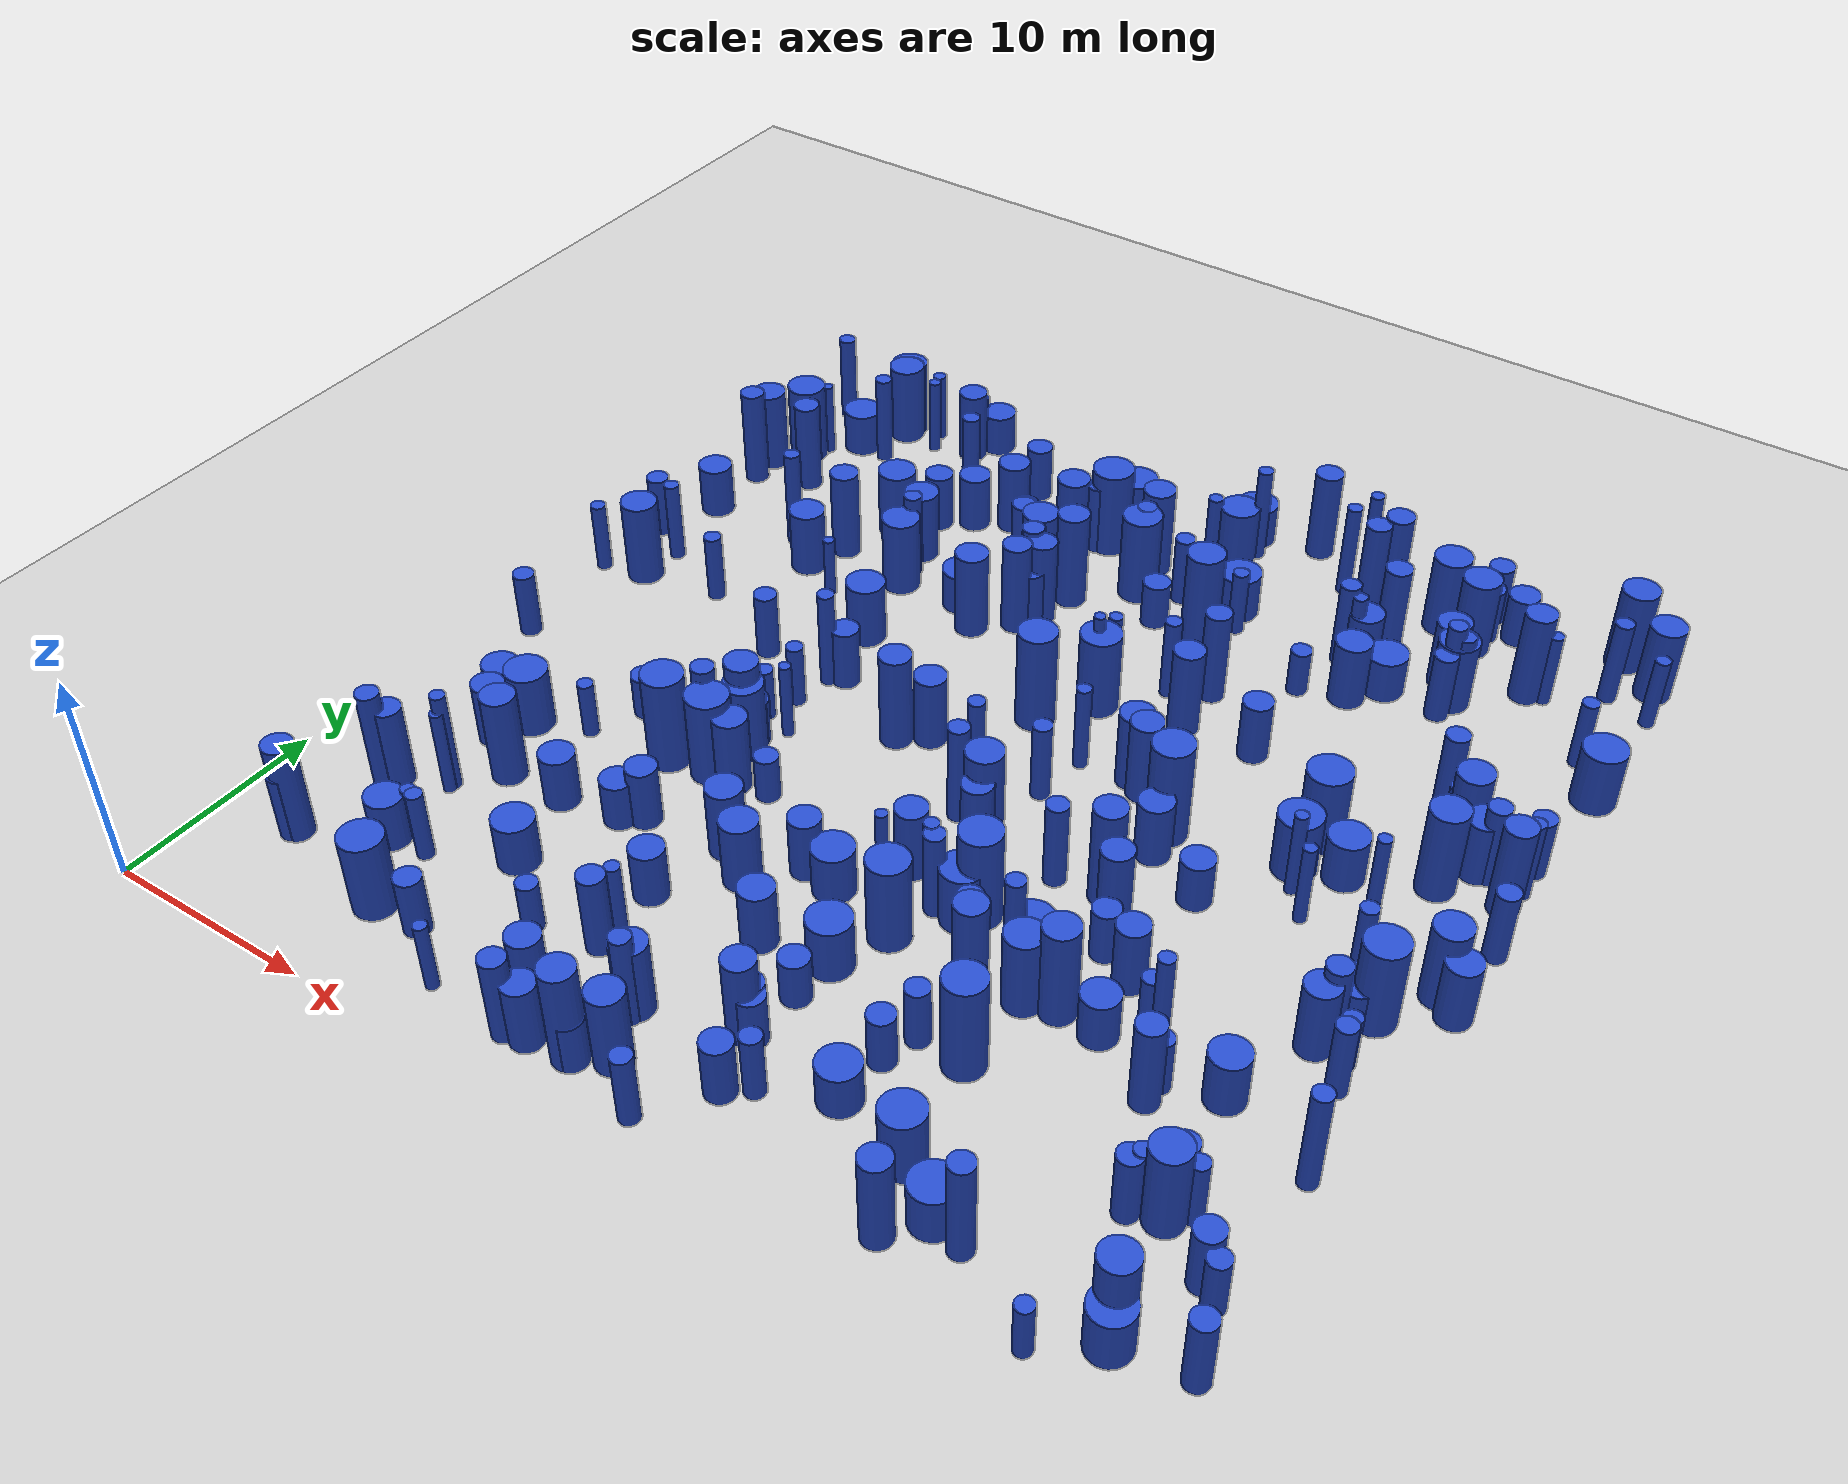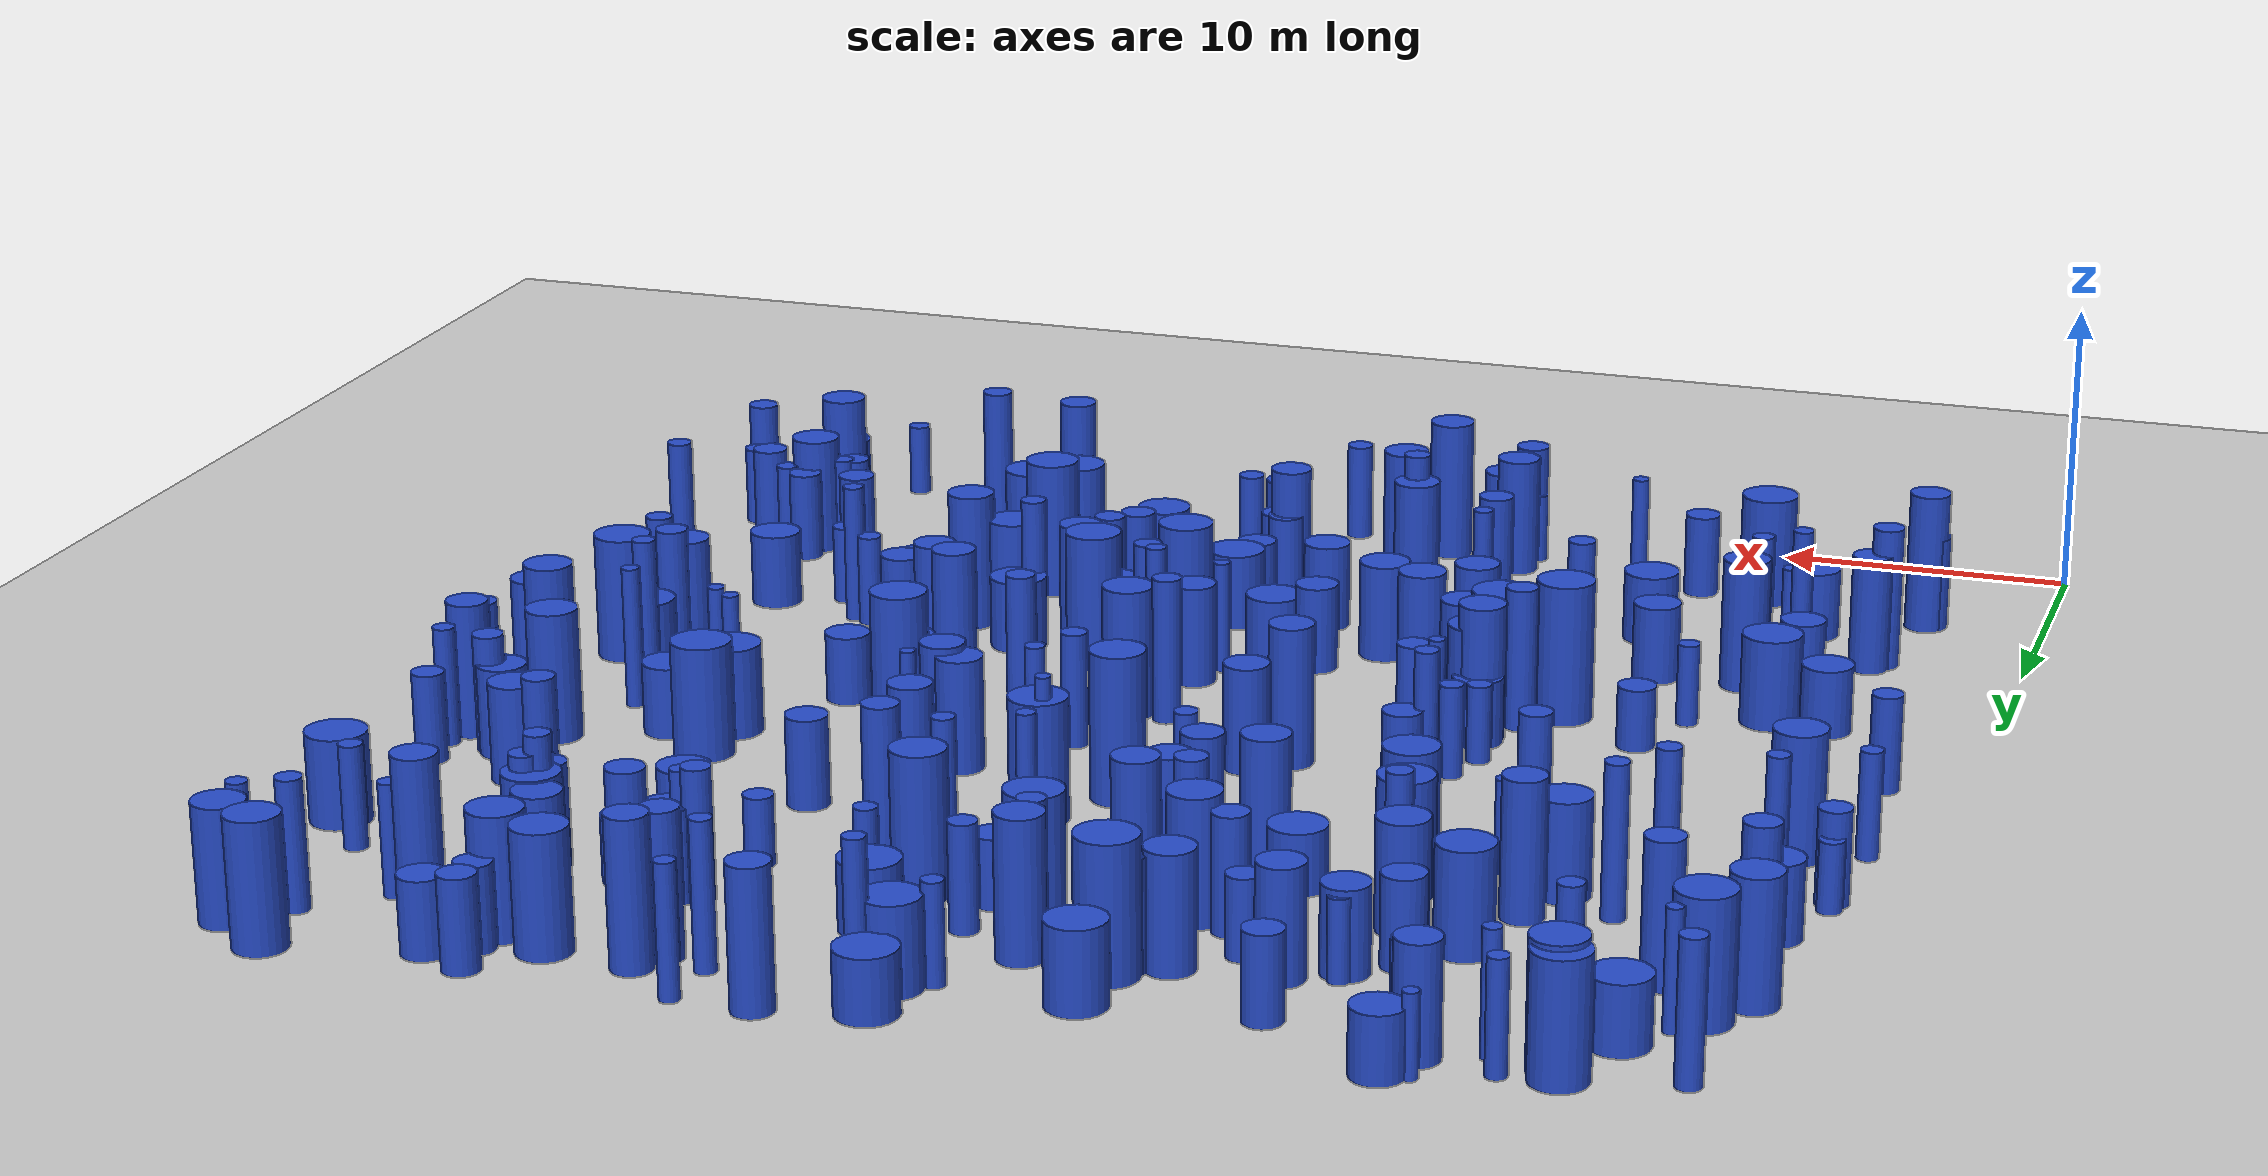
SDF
<sdf version="1.6">
 <world name="default">
  <light name="sun" type="directional">
   <pose>0 0 10 0 -0 0</pose>
   <diffuse>0.8 0.8 0.8 1</diffuse>
   <specular>0.1 0.1 0.1 1</specular>
   <attenuation>
    <range>1000</range>
    <constant>0.9</constant>
    <linear>0.01</linear>
    <quadratic>0.001</quadratic>
   </attenuation>
   <direction>-0.5 0.5 -1</direction>
  </light>
  <model name="ground_plane">
   <static>1</static>
   <link name="link">
    <collision name="collision">
     <geometry><plane><normal>0 0 1</normal><size>100 100</size></plane></geometry>
     <surface><friction><ode><mu>100</mu><mu2>50</mu2></ode></friction></surface>
    </collision>
    <visual name="visual">
     <cast_shadows>0</cast_shadows>
     <geometry><plane><normal>0 0 1</normal><size>100 100</size></plane></geometry>
     <material>
      <script><uri>file://media/materials/scripts/gazebo.material</uri><name>Gazebo/Grey</name></script>
     </material>
    </visual>
   </link>
  </model>
  <gravity>0 0 -9.8</gravity>
  <magnetic_field>6e-06 2.3e-05 -4.2e-05</magnetic_field>
  <atmosphere type="adiabatic"/>
  <physics name="default_physics" default="0" type="ode">
   <max_step_size>0.001</max_step_size>
   <real_time_factor>1</real_time_factor>
   <real_time_update_rate>1000</real_time_update_rate>
  </physics>
  <scene><ambient>0.4 0.4 0.4 1</ambient><background>0.7 0.7 0.7 1</background><shadows>1</shadows></scene>
  <spherical_coordinates>
   <surface_model>EARTH_WGS84</surface_model>
   <latitude_deg>0</latitude_deg>
   <longitude_deg>0</longitude_deg>
   <elevation>0</elevation>
   <heading_deg>0</heading_deg>
  </spherical_coordinates>
  <model name="0">
   <static>0</static>
   <link name="link">
    <inertial>
     <mass>2</mass>
     <inertia><ixx>1.44488</ixx><ixy>0</ixy><ixz>0</ixz><iyy>1.44488</iyy><iyz>0</iyz><izz>0.600062</izz></inertia>
    </inertial>
    <collision name="collision">
     <geometry><cylinder><length>2.6209</length><radius>0.774637</radius></cylinder></geometry>
     <surface><contact><collide_without_contact>1</collide_without_contact></contact></surface>
    </collision>
    <visual name="visual">
     <geometry><cylinder><length>2.6209</length><radius>0.774637</radius></cylinder></geometry>
     <material>
      <script><uri>file://media/materials/scripts/gazebo.material</uri><name>Gazebo/Blue</name></script>
     </material>
    </visual>
    <gravity>0</gravity>
   </link>
   <pose>18.5084 11.3578 1.31045 0 -0 0</pose>
  </model>
  <model name="1">
   <static>0</static>
   <link name="link">
    <inertial>
     <mass>2</mass>
     <inertia><ixx>3.78778</ixx><ixy>0</ixy><ixz>0</ixz><iyy>3.78778</iyy><iyz>0</iyz><izz>0.35692</izz></inertia>
    </inertial>
    <collision name="collision">
     <geometry><cylinder><length>4.65359</length><radius>0.597428</radius></cylinder></geometry>
     <surface><contact><collide_without_contact>1</collide_without_contact></contact></surface>
    </collision>
    <visual name="visual">
     <geometry><cylinder><length>4.65359</length><radius>0.597428</radius></cylinder></geometry>
     <material>
      <script><uri>file://media/materials/scripts/gazebo.material</uri><name>Gazebo/Blue</name></script>
     </material>
    </visual>
    <gravity>0</gravity>
   </link>
   <pose>30.9437 35.2466 2.3268 0 -0 0</pose>
  </model>
  <model name="2">
   <static>0</static>
   <link name="link">
    <inertial>
     <mass>2</mass>
     <inertia><ixx>3.20586</ixx><ixy>0</ixy><ixz>0</ixz><iyy>3.20586</iyy><iyz>0</iyz><izz>0.636563</izz></inertia>
    </inertial>
    <collision name="collision">
     <geometry><cylinder><length>4.16238</length><radius>0.797849</radius></cylinder></geometry>
     <surface><contact><collide_without_contact>1</collide_without_contact></contact></surface>
    </collision>
    <visual name="visual">
     <geometry><cylinder><length>4.16238</length><radius>0.797849</radius></cylinder></geometry>
     <material>
      <script><uri>file://media/materials/scripts/gazebo.material</uri><name>Gazebo/Blue</name></script>
     </material>
    </visual>
    <gravity>0</gravity>
   </link>
   <pose>44.4662 4.48744 2.08119 0 -0 0</pose>
  </model>
  <model name="3">
   <static>0</static>
   <link name="link">
    <inertial>
     <mass>2</mass>
     <inertia><ixx>1.27106</ixx><ixy>0</ixy><ixz>0</ixz><iyy>1.27106</iyy><iyz>0</iyz><izz>0.895913</izz></inertia>
    </inertial>
    <collision name="collision">
     <geometry><cylinder><length>2.2223</length><radius>0.946527</radius></cylinder></geometry>
     <surface><contact><collide_without_contact>1</collide_without_contact></contact></surface>
    </collision>
    <visual name="visual">
     <geometry><cylinder><length>2.2223</length><radius>0.946527</radius></cylinder></geometry>
     <material>
      <script><uri>file://media/materials/scripts/gazebo.material</uri><name>Gazebo/Blue</name></script>
     </material>
    </visual>
    <gravity>0</gravity>
   </link>
   <pose>6.2225 42.677 1.11115 0 -0 0</pose>
  </model>
  <model name="4">
   <static>0</static>
   <link name="link">
    <inertial>
     <mass>2</mass>
     <inertia>
      <ixx>0.982627</ixx>
      <ixy>0</ixy>
      <ixz>0</ixz>
      <iyy>0.982627</iyy>
      <iyz>0</iyz>
      <izz>0.248096</izz>
     </inertia>
    </inertial>
    <collision name="collision">
     <geometry><cylinder><length>2.26969</length><radius>0.498092</radius></cylinder></geometry>
     <surface><contact><collide_without_contact>1</collide_without_contact></contact></surface>
    </collision>
    <visual name="visual">
     <geometry><cylinder><length>2.26969</length><radius>0.498092</radius></cylinder></geometry>
     <material>
      <script><uri>file://media/materials/scripts/gazebo.material</uri><name>Gazebo/Blue</name></script>
     </material>
    </visual>
    <gravity>0</gravity>
   </link>
   <pose>43.5504 33.5469 1.13484 0 -0 0</pose>
  </model>
  <model name="5">
   <static>0</static>
   <link name="link">
    <inertial>
     <mass>2</mass>
     <inertia><ixx>1.15559</ixx><ixy>0</ixy><ixz>0</ixz><iyy>1.15559</iyy><iyz>0</iyz><izz>0.571928</izz></inertia>
    </inertial>
    <collision name="collision">
     <geometry><cylinder><length>2.28424</length><radius>0.756259</radius></cylinder></geometry>
     <surface><contact><collide_without_contact>1</collide_without_contact></contact></surface>
    </collision>
    <visual name="visual">
     <geometry><cylinder><length>2.28424</length><radius>0.756259</radius></cylinder></geometry>
     <material>
      <script><uri>file://media/materials/scripts/gazebo.material</uri><name>Gazebo/Blue</name></script>
     </material>
    </visual>
    <gravity>0</gravity>
   </link>
   <pose>14.5568 14.0318 1.14212 0 -0 0</pose>
  </model>
  <model name="6">
   <static>0</static>
   <link name="link">
    <inertial>
     <mass>2</mass>
     <inertia><ixx>4.21567</ixx><ixy>0</ixy><ixz>0</ixz><iyy>4.21567</iyy><iyz>0</iyz><izz>0.18322</izz></inertia>
    </inertial>
    <collision name="collision">
     <geometry><cylinder><length>4.97437</length><radius>0.428042</radius></cylinder></geometry>
     <surface><contact><collide_without_contact>1</collide_without_contact></contact></surface>
    </collision>
    <visual name="visual">
     <geometry><cylinder><length>4.97437</length><radius>0.428042</radius></cylinder></geometry>
     <material>
      <script><uri>file://media/materials/scripts/gazebo.material</uri><name>Gazebo/Blue</name></script>
     </material>
    </visual>
    <gravity>0</gravity>
   </link>
   <pose>32.8393 16.173 2.48719 0 -0 0</pose>
  </model>
  <model name="7">
   <static>0</static>
   <link name="link">
    <inertial>
     <mass>2</mass>
     <inertia><ixx>3.06232</ixx><ixy>0</ixy><ixz>0</ixz><iyy>3.06232</iyy><iyz>0</iyz><izz>0.178257</izz></inertia>
    </inertial>
    <collision name="collision">
     <geometry><cylinder><length>4.22364</length><radius>0.422205</radius></cylinder></geometry>
     <surface><contact><collide_without_contact>1</collide_without_contact></contact></surface>
    </collision>
    <visual name="visual">
     <geometry><cylinder><length>4.22364</length><radius>0.422205</radius></cylinder></geometry>
     <material>
      <script><uri>file://media/materials/scripts/gazebo.material</uri><name>Gazebo/Blue</name></script>
     </material>
    </visual>
    <gravity>0</gravity>
   </link>
   <pose>45.6162 45.1561 2.11182 0 -0 0</pose>
  </model>
  <model name="8">
   <static>0</static>
   <link name="link">
    <inertial>
     <mass>2</mass>
     <inertia><ixx>3.88325</ixx><ixy>0</ixy><ixz>0</ixz><iyy>3.88325</iyy><iyz>0</iyz><izz>0.126882</izz></inertia>
    </inertial>
    <collision name="collision">
     <geometry><cylinder><length>4.78737</length><radius>0.356206</radius></cylinder></geometry>
     <surface><contact><collide_without_contact>1</collide_without_contact></contact></surface>
    </collision>
    <visual name="visual">
     <geometry><cylinder><length>4.78737</length><radius>0.356206</radius></cylinder></geometry>
     <material>
      <script><uri>file://media/materials/scripts/gazebo.material</uri><name>Gazebo/Blue</name></script>
     </material>
    </visual>
    <gravity>0</gravity>
   </link>
   <pose>39.4281 16.1246 2.39368 0 -0 0</pose>
  </model>
  <model name="9">
   <static>0</static>
   <link name="link">
    <inertial>
     <mass>2</mass>
     <inertia><ixx>2.4622</ixx><ixy>0</ixy><ixz>0</ixz><iyy>2.4622</iyy><iyz>0</iyz><izz>0.0741787</izz></inertia>
    </inertial>
    <collision name="collision">
     <geometry><cylinder><length>3.81453</length><radius>0.272358</radius></cylinder></geometry>
     <surface><contact><collide_without_contact>1</collide_without_contact></contact></surface>
    </collision>
    <visual name="visual">
     <geometry><cylinder><length>3.81453</length><radius>0.272358</radius></cylinder></geometry>
     <material>
      <script><uri>file://media/materials/scripts/gazebo.material</uri><name>Gazebo/Blue</name></script>
     </material>
    </visual>
    <gravity>0</gravity>
   </link>
   <pose>16.9794 22.3718 1.90727 0 -0 0</pose>
  </model>
  <model name="10">
   <static>0</static>
   <link name="link">
    <inertial>
     <mass>2</mass>
     <inertia><ixx>3.24813</ixx><ixy>0</ixy><ixz>0</ixz><iyy>3.24813</iyy><iyz>0</iyz><izz>0.387761</izz></inertia>
    </inertial>
    <collision name="collision">
     <geometry><cylinder><length>4.28083</length><radius>0.622705</radius></cylinder></geometry>
     <surface><contact><collide_without_contact>1</collide_without_contact></contact></surface>
    </collision>
    <visual name="visual">
     <geometry><cylinder><length>4.28083</length><radius>0.622705</radius></cylinder></geometry>
     <material>
      <script><uri>file://media/materials/scripts/gazebo.material</uri><name>Gazebo/Blue</name></script>
     </material>
    </visual>
    <gravity>0</gravity>
   </link>
   <pose>40.3812 13.4456 2.14041 0 -0 0</pose>
  </model>
  <model name="11">
   <static>0</static>
   <link name="link">
    <inertial>
     <mass>2</mass>
     <inertia><ixx>1.8509</ixx><ixy>0</ixy><ixz>0</ixz><iyy>1.8509</iyy><iyz>0</iyz><izz>0.122377</izz></inertia>
    </inertial>
    <collision name="collision">
     <geometry><cylinder><length>3.27693</length><radius>0.349825</radius></cylinder></geometry>
     <surface><contact><collide_without_contact>1</collide_without_contact></contact></surface>
    </collision>
    <visual name="visual">
     <geometry><cylinder><length>3.27693</length><radius>0.349825</radius></cylinder></geometry>
     <material>
      <script><uri>file://media/materials/scripts/gazebo.material</uri><name>Gazebo/Blue</name></script>
     </material>
    </visual>
    <gravity>0</gravity>
   </link>
   <pose>25.7147 44.6037 1.63846 0 -0 0</pose>
  </model>
  <model name="12">
   <static>0</static>
   <link name="link">
    <inertial>
     <mass>2</mass>
     <inertia><ixx>2.16856</ixx><ixy>0</ixy><ixz>0</ixz><iyy>2.16856</iyy><iyz>0</iyz><izz>0.502649</izz></inertia>
    </inertial>
    <collision name="collision">
     <geometry><cylinder><length>3.39167</length><radius>0.708978</radius></cylinder></geometry>
     <surface><contact><collide_without_contact>1</collide_without_contact></contact></surface>
    </collision>
    <visual name="visual">
     <geometry><cylinder><length>3.39167</length><radius>0.708978</radius></cylinder></geometry>
     <material>
      <script><uri>file://media/materials/scripts/gazebo.material</uri><name>Gazebo/Blue</name></script>
     </material>
    </visual>
    <gravity>0</gravity>
   </link>
   <pose>27.6973 21.2651 1.69583 0 -0 0</pose>
  </model>
  <model name="13">
   <static>0</static>
   <link name="link">
    <inertial>
     <mass>2</mass>
     <inertia><ixx>1.65318</ixx><ixy>0</ixy><ixz>0</ixz><iyy>1.65318</iyy><iyz>0</iyz><izz>0.578017</izz></inertia>
    </inertial>
    <collision name="collision">
     <geometry><cylinder><length>2.86095</length><radius>0.760275</radius></cylinder></geometry>
     <surface><contact><collide_without_contact>1</collide_without_contact></contact></surface>
    </collision>
    <visual name="visual">
     <geometry><cylinder><length>2.86095</length><radius>0.760275</radius></cylinder></geometry>
     <material>
      <script><uri>file://media/materials/scripts/gazebo.material</uri><name>Gazebo/Blue</name></script>
     </material>
    </visual>
    <gravity>0</gravity>
   </link>
   <pose>14.8082 40.254 1.43047 0 -0 0</pose>
  </model>
  <model name="14">
   <static>0</static>
   <link name="link">
    <inertial>
     <mass>2</mass>
     <inertia><ixx>3.82852</ixx><ixy>0</ixy><ixz>0</ixz><iyy>3.82852</iyy><iyz>0</iyz><izz>0.125875</izz></inertia>
    </inertial>
    <collision name="collision">
     <geometry><cylinder><length>4.75326</length><radius>0.354788</radius></cylinder></geometry>
     <surface><contact><collide_without_contact>1</collide_without_contact></contact></surface>
    </collision>
    <visual name="visual">
     <geometry><cylinder><length>4.75326</length><radius>0.354788</radius></cylinder></geometry>
     <material>
      <script><uri>file://media/materials/scripts/gazebo.material</uri><name>Gazebo/Blue</name></script>
     </material>
    </visual>
    <gravity>0</gravity>
   </link>
   <pose>32.3125 45.6475 2.37663 0 -0 0</pose>
  </model>
  <model name="15">
   <static>0</static>
   <link name="link">
    <inertial>
     <mass>2</mass>
     <inertia><ixx>2.02878</ixx><ixy>0</ixy><ixz>0</ixz><iyy>2.02878</iyy><iyz>0</iyz><izz>0.837732</izz></inertia>
    </inertial>
    <collision name="collision">
     <geometry><cylinder><length>3.10797</length><radius>0.915277</radius></cylinder></geometry>
     <surface><contact><collide_without_contact>1</collide_without_contact></contact></surface>
    </collision>
    <visual name="visual">
     <geometry><cylinder><length>3.10797</length><radius>0.915277</radius></cylinder></geometry>
     <material>
      <script><uri>file://media/materials/scripts/gazebo.material</uri><name>Gazebo/Blue</name></script>
     </material>
    </visual>
    <gravity>0</gravity>
   </link>
   <pose>15.7285 29.9287 1.55399 0 -0 0</pose>
  </model>
  <model name="16">
   <static>0</static>
   <link name="link">
    <inertial>
     <mass>2</mass>
     <inertia><ixx>1.16291</ixx><ixy>0</ixy><ixz>0</ixz><iyy>1.16291</iyy><iyz>0</iyz><izz>0.875446</izz></inertia>
    </inertial>
    <collision name="collision">
     <geometry><cylinder><length>2.08593</length><radius>0.935653</radius></cylinder></geometry>
     <surface><contact><collide_without_contact>1</collide_without_contact></contact></surface>
    </collision>
    <visual name="visual">
     <geometry><cylinder><length>2.08593</length><radius>0.935653</radius></cylinder></geometry>
     <material>
      <script><uri>file://media/materials/scripts/gazebo.material</uri><name>Gazebo/Blue</name></script>
     </material>
    </visual>
    <gravity>0</gravity>
   </link>
   <pose>31.1404 7.15658 1.04296 0 -0 0</pose>
  </model>
  <model name="17">
   <static>0</static>
   <link name="link">
    <inertial>
     <mass>2</mass>
     <inertia><ixx>4.11336</ixx><ixy>0</ixy><ixz>0</ixz><iyy>4.11336</iyy><iyz>0</iyz><izz>0.443854</izz></inertia>
    </inertial>
    <collision name="collision">
     <geometry><cylinder><length>4.83204</length><radius>0.666223</radius></cylinder></geometry>
     <surface><contact><collide_without_contact>1</collide_without_contact></contact></surface>
    </collision>
    <visual name="visual">
     <geometry><cylinder><length>4.83204</length><radius>0.666223</radius></cylinder></geometry>
     <material>
      <script><uri>file://media/materials/scripts/gazebo.material</uri><name>Gazebo/Blue</name></script>
     </material>
    </visual>
    <gravity>0</gravity>
   </link>
   <pose>34.3973 46.1199 2.41602 0 -0 0</pose>
  </model>
  <model name="18">
   <static>0</static>
   <link name="link">
    <inertial>
     <mass>2</mass>
     <inertia>
      <ixx>0.856917</ixx>
      <ixy>0</ixy>
      <ixz>0</ixz>
      <iyy>0.856917</iyy>
      <iyz>0</iyz>
      <izz>0.164802</izz>
     </inertia>
    </inertial>
    <collision name="collision">
     <geometry><cylinder><length>2.15571</length><radius>0.405958</radius></cylinder></geometry>
     <surface><contact><collide_without_contact>1</collide_without_contact></contact></surface>
    </collision>
    <visual name="visual">
     <geometry><cylinder><length>2.15571</length><radius>0.405958</radius></cylinder></geometry>
     <material>
      <script><uri>file://media/materials/scripts/gazebo.material</uri><name>Gazebo/Blue</name></script>
     </material>
    </visual>
    <gravity>0</gravity>
   </link>
   <pose>23.9671 26.7785 1.07786 0 -0 0</pose>
  </model>
  <model name="19">
   <static>0</static>
   <link name="link">
    <inertial>
     <mass>2</mass>
     <inertia><ixx>1.7024</ixx><ixy>0</ixy><ixz>0</ixz><iyy>1.7024</iyy><iyz>0</iyz><izz>0.35835</izz></inertia>
    </inertial>
    <collision name="collision">
     <geometry><cylinder><length>3.02313</length><radius>0.598624</radius></cylinder></geometry>
     <surface><contact><collide_without_contact>1</collide_without_contact></contact></surface>
    </collision>
    <visual name="visual">
     <geometry><cylinder><length>3.02313</length><radius>0.598624</radius></cylinder></geometry>
     <material>
      <script><uri>file://media/materials/scripts/gazebo.material</uri><name>Gazebo/Blue</name></script>
     </material>
    </visual>
    <gravity>0</gravity>
   </link>
   <pose>39.0269 47.6818 1.51157 0 -0 0</pose>
  </model>
  <model name="20">
   <static>0</static>
   <link name="link">
    <inertial>
     <mass>2</mass>
     <inertia>
      <ixx>0.985313</ixx>
      <ixy>0</ixy>
      <ixz>0</ixz>
      <iyy>0.985313</iyy>
      <iyz>0</iyz>
      <izz>0.312388</izz>
     </inertia>
    </inertial>
    <collision name="collision">
     <geometry><cylinder><length>2.23041</length><radius>0.558917</radius></cylinder></geometry>
     <surface><contact><collide_without_contact>1</collide_without_contact></contact></surface>
    </collision>
    <visual name="visual">
     <geometry><cylinder><length>2.23041</length><radius>0.558917</radius></cylinder></geometry>
     <material>
      <script><uri>file://media/materials/scripts/gazebo.material</uri><name>Gazebo/Blue</name></script>
     </material>
    </visual>
    <gravity>0</gravity>
   </link>
   <pose>18.7341 18.7242 1.1152 0 -0 0</pose>
  </model>
  <model name="21">
   <static>0</static>
   <link name="link">
    <inertial>
     <mass>2</mass>
     <inertia>
      <ixx>0.942504</ixx>
      <ixy>0</ixy>
      <ixz>0</ixz>
      <iyy>0.942504</iyy>
      <iyz>0</iyz>
      <izz>0.157121</izz>
     </inertia>
    </inertial>
    <collision name="collision">
     <geometry><cylinder><length>2.27677</length><radius>0.396385</radius></cylinder></geometry>
     <surface><contact><collide_without_contact>1</collide_without_contact></contact></surface>
    </collision>
    <visual name="visual">
     <geometry><cylinder><length>2.27677</length><radius>0.396385</radius></cylinder></geometry>
     <material>
      <script><uri>file://media/materials/scripts/gazebo.material</uri><name>Gazebo/Blue</name></script>
     </material>
    </visual>
    <gravity>0</gravity>
   </link>
   <pose>2.46046 31.5423 1.13838 0 -0 0</pose>
  </model>
  <model name="22">
   <static>0</static>
   <link name="link">
    <inertial>
     <mass>2</mass>
     <inertia><ixx>1.74504</ixx><ixy>0</ixy><ixz>0</ixz><iyy>1.74504</iyy><iyz>0</iyz><izz>0.480682</izz></inertia>
    </inertial>
    <collision name="collision">
     <geometry><cylinder><length>3.00469</length><radius>0.693313</radius></cylinder></geometry>
     <surface><contact><collide_without_contact>1</collide_without_contact></contact></surface>
    </collision>
    <visual name="visual">
     <geometry><cylinder><length>3.00469</length><radius>0.693313</radius></cylinder></geometry>
     <material>
      <script><uri>file://media/materials/scripts/gazebo.material</uri><name>Gazebo/Blue</name></script>
     </material>
    </visual>
    <gravity>0</gravity>
   </link>
   <pose>34.3942 32.773 1.50235 0 -0 0</pose>
  </model>
  <model name="23">
   <static>0</static>
   <link name="link">
    <inertial>
     <mass>2</mass>
     <inertia><ixx>2.07027</ixx><ixy>0</ixy><ixz>0</ixz><iyy>2.07027</iyy><iyz>0</iyz><izz>0.208934</izz></inertia>
    </inertial>
    <collision name="collision">
     <geometry><cylinder><length>3.43436</length><radius>0.457093</radius></cylinder></geometry>
     <surface><contact><collide_without_contact>1</collide_without_contact></contact></surface>
    </collision>
    <visual name="visual">
     <geometry><cylinder><length>3.43436</length><radius>0.457093</radius></cylinder></geometry>
     <material>
      <script><uri>file://media/materials/scripts/gazebo.material</uri><name>Gazebo/Blue</name></script>
     </material>
    </visual>
    <gravity>0</gravity>
   </link>
   <pose>25.3111 2.1227 1.71718 0 -0 0</pose>
  </model>
  <model name="24">
   <static>0</static>
   <link name="link">
    <inertial>
     <mass>2</mass>
     <inertia><ixx>1.15813</ixx><ixy>0</ixy><ixz>0</ixz><iyy>1.15813</iyy><iyz>0</iyz><izz>0.112947</izz></inertia>
    </inertial>
    <collision name="collision">
     <geometry><cylinder><length>2.57098</length><radius>0.336075</radius></cylinder></geometry>
     <surface><contact><collide_without_contact>1</collide_without_contact></contact></surface>
    </collision>
    <visual name="visual">
     <geometry><cylinder><length>2.57098</length><radius>0.336075</radius></cylinder></geometry>
     <material>
      <script><uri>file://media/materials/scripts/gazebo.material</uri><name>Gazebo/Blue</name></script>
     </material>
    </visual>
    <gravity>0</gravity>
   </link>
   <pose>8.17971 8.45153 1.28549 0 -0 0</pose>
  </model>
  <model name="25">
   <static>0</static>
   <link name="link">
    <inertial>
     <mass>2</mass>
     <inertia><ixx>2.7316</ixx><ixy>0</ixy><ixz>0</ixz><iyy>2.7316</iyy><iyz>0</iyz><izz>0.105322</izz></inertia>
    </inertial>
    <collision name="collision">
     <geometry><cylinder><length>4.00919</length><radius>0.324534</radius></cylinder></geometry>
     <surface><contact><collide_without_contact>1</collide_without_contact></contact></surface>
    </collision>
    <visual name="visual">
     <geometry><cylinder><length>4.00919</length><radius>0.324534</radius></cylinder></geometry>
     <material>
      <script><uri>file://media/materials/scripts/gazebo.material</uri><name>Gazebo/Blue</name></script>
     </material>
    </visual>
    <gravity>0</gravity>
   </link>
   <pose>35.1952 40.577 2.0046 0 -0 0</pose>
  </model>
  <model name="26">
   <static>0</static>
   <link name="link">
    <inertial>
     <mass>2</mass>
     <inertia><ixx>1.56501</ixx><ixy>0</ixy><ixz>0</ixz><iyy>1.56501</iyy><iyz>0</iyz><izz>0.284058</izz></inertia>
    </inertial>
    <collision name="collision">
     <geometry><cylinder><length>2.92197</length><radius>0.532971</radius></cylinder></geometry>
     <surface><contact><collide_without_contact>1</collide_without_contact></contact></surface>
    </collision>
    <visual name="visual">
     <geometry><cylinder><length>2.92197</length><radius>0.532971</radius></cylinder></geometry>
     <material>
      <script><uri>file://media/materials/scripts/gazebo.material</uri><name>Gazebo/Blue</name></script>
     </material>
    </visual>
    <gravity>0</gravity>
   </link>
   <pose>31.8249 11.1624 1.46098 0 -0 0</pose>
  </model>
  <model name="27">
   <static>0</static>
   <link name="link">
    <inertial>
     <mass>2</mass>
     <inertia><ixx>3.49238</ixx><ixy>0</ixy><ixz>0</ixz><iyy>3.49238</iyy><iyz>0</iyz><izz>0.155393</izz></inertia>
    </inertial>
    <collision name="collision">
     <geometry><cylinder><length>4.52638</length><radius>0.394199</radius></cylinder></geometry>
     <surface><contact><collide_without_contact>1</collide_without_contact></contact></surface>
    </collision>
    <visual name="visual">
     <geometry><cylinder><length>4.52638</length><radius>0.394199</radius></cylinder></geometry>
     <material>
      <script><uri>file://media/materials/scripts/gazebo.material</uri><name>Gazebo/Blue</name></script>
     </material>
    </visual>
    <gravity>0</gravity>
   </link>
   <pose>44.2707 22.8518 2.26319 0 -0 0</pose>
  </model>
  <model name="28">
   <static>0</static>
   <link name="link">
    <inertial>
     <mass>2</mass>
     <inertia><ixx>2.79456</ixx><ixy>0</ixy><ixz>0</ixz><iyy>2.79456</iyy><iyz>0</iyz><izz>0.744168</izz></inertia>
    </inertial>
    <collision name="collision">
     <geometry><cylinder><length>3.81246</length><radius>0.862652</radius></cylinder></geometry>
     <surface><contact><collide_without_contact>1</collide_without_contact></contact></surface>
    </collision>
    <visual name="visual">
     <geometry><cylinder><length>3.81246</length><radius>0.862652</radius></cylinder></geometry>
     <material>
      <script><uri>file://media/materials/scripts/gazebo.material</uri><name>Gazebo/Blue</name></script>
     </material>
    </visual>
    <gravity>0</gravity>
   </link>
   <pose>34.0348 15.0048 1.90623 0 -0 0</pose>
  </model>
  <model name="29">
   <static>0</static>
   <link name="link">
    <inertial>
     <mass>2</mass>
     <inertia><ixx>1.13627</ixx><ixy>0</ixy><ixz>0</ixz><iyy>1.13627</iyy><iyz>0</iyz><izz>0.890575</izz></inertia>
    </inertial>
    <collision name="collision">
     <geometry><cylinder><length>2.03615</length><radius>0.943703</radius></cylinder></geometry>
     <surface><contact><collide_without_contact>1</collide_without_contact></contact></surface>
    </collision>
    <visual name="visual">
     <geometry><cylinder><length>2.03615</length><radius>0.943703</radius></cylinder></geometry>
     <material>
      <script><uri>file://media/materials/scripts/gazebo.material</uri><name>Gazebo/Blue</name></script>
     </material>
    </visual>
    <gravity>0</gravity>
   </link>
   <pose>17.9595 34.4953 1.01807 0 -0 0</pose>
  </model>
  <model name="30">
   <static>0</static>
   <link name="link">
    <inertial>
     <mass>2</mass>
     <inertia><ixx>2.2394</ixx><ixy>0</ixy><ixz>0</ixz><iyy>2.2394</iyy><iyz>0</iyz><izz>0.282543</izz></inertia>
    </inertial>
    <collision name="collision">
     <geometry><cylinder><length>3.54806</length><radius>0.531548</radius></cylinder></geometry>
     <surface><contact><collide_without_contact>1</collide_without_contact></contact></surface>
    </collision>
    <visual name="visual">
     <geometry><cylinder><length>3.54806</length><radius>0.531548</radius></cylinder></geometry>
     <material>
      <script><uri>file://media/materials/scripts/gazebo.material</uri><name>Gazebo/Blue</name></script>
     </material>
    </visual>
    <gravity>0</gravity>
   </link>
   <pose>47.7304 4.35367 1.77403 0 -0 0</pose>
  </model>
  <model name="31">
   <static>0</static>
   <link name="link">
    <inertial>
     <mass>2</mass>
     <inertia>
      <ixx>2.64859</ixx>
      <ixy>0</ixy>
      <ixz>0</ixz>
      <iyy>2.64859</iyy>
      <iyz>0</iyz>
      <izz>0.0843179</izz>
     </inertia>
    </inertial>
    <collision name="collision">
     <geometry><cylinder><length>3.95456</length><radius>0.290376</radius></cylinder></geometry>
     <surface><contact><collide_without_contact>1</collide_without_contact></contact></surface>
    </collision>
    <visual name="visual">
     <geometry><cylinder><length>3.95456</length><radius>0.290376</radius></cylinder></geometry>
     <material>
      <script><uri>file://media/materials/scripts/gazebo.material</uri><name>Gazebo/Blue</name></script>
     </material>
    </visual>
    <gravity>0</gravity>
   </link>
   <pose>40.7251 25.0415 1.97728 0 -0 0</pose>
  </model>
  <model name="32">
   <static>0</static>
   <link name="link">
    <inertial>
     <mass>2</mass>
     <inertia><ixx>1.31359</ixx><ixy>0</ixy><ixz>0</ixz><iyy>1.31359</iyy><iyz>0</iyz><izz>0.534164</izz></inertia>
    </inertial>
    <collision name="collision">
     <geometry><cylinder><length>2.5058</length><radius>0.730865</radius></cylinder></geometry>
     <surface><contact><collide_without_contact>1</collide_without_contact></contact></surface>
    </collision>
    <visual name="visual">
     <geometry><cylinder><length>2.5058</length><radius>0.730865</radius></cylinder></geometry>
     <material>
      <script><uri>file://media/materials/scripts/gazebo.material</uri><name>Gazebo/Blue</name></script>
     </material>
    </visual>
    <gravity>0</gravity>
   </link>
   <pose>40.5633 46.9048 1.2529 0 -0 0</pose>
  </model>
  <model name="33">
   <static>0</static>
   <link name="link">
    <inertial>
     <mass>2</mass>
     <inertia><ixx>3.34107</ixx><ixy>0</ixy><ixz>0</ixz><iyy>3.34107</iyy><iyz>0</iyz><izz>0.741521</izz></inertia>
    </inertial>
    <collision name="collision">
     <geometry><cylinder><length>4.22159</length><radius>0.861116</radius></cylinder></geometry>
     <surface><contact><collide_without_contact>1</collide_without_contact></contact></surface>
    </collision>
    <visual name="visual">
     <geometry><cylinder><length>4.22159</length><radius>0.861116</radius></cylinder></geometry>
     <material>
      <script><uri>file://media/materials/scripts/gazebo.material</uri><name>Gazebo/Blue</name></script>
     </material>
    </visual>
    <gravity>0</gravity>
   </link>
   <pose>4.2013 27.7585 2.1108 0 -0 0</pose>
  </model>
  <model name="34">
   <static>0</static>
   <link name="link">
    <inertial>
     <mass>2</mass>
     <inertia><ixx>1.44194</ixx><ixy>0</ixy><ixz>0</ixz><iyy>1.44194</iyy><iyz>0</iyz><izz>0.671354</izz></inertia>
    </inertial>
    <collision name="collision">
     <geometry><cylinder><length>2.57635</length><radius>0.819362</radius></cylinder></geometry>
     <surface><contact><collide_without_contact>1</collide_without_contact></contact></surface>
    </collision>
    <visual name="visual">
     <geometry><cylinder><length>2.57635</length><radius>0.819362</radius></cylinder></geometry>
     <material>
      <script><uri>file://media/materials/scripts/gazebo.material</uri><name>Gazebo/Blue</name></script>
     </material>
    </visual>
    <gravity>0</gravity>
   </link>
   <pose>3.57515 34.0262 1.28817 0 -0 0</pose>
  </model>
  <model name="35">
   <static>0</static>
   <link name="link">
    <inertial>
     <mass>2</mass>
     <inertia><ixx>3.99285</ixx><ixy>0</ixy><ixz>0</ixz><iyy>3.99285</iyy><iyz>0</iyz><izz>0.131146</izz></inertia>
    </inertial>
    <collision name="collision">
     <geometry><cylinder><length>4.85424</length><radius>0.36214</radius></cylinder></geometry>
     <surface><contact><collide_without_contact>1</collide_without_contact></contact></surface>
    </collision>
    <visual name="visual">
     <geometry><cylinder><length>4.85424</length><radius>0.36214</radius></cylinder></geometry>
     <material>
      <script><uri>file://media/materials/scripts/gazebo.material</uri><name>Gazebo/Blue</name></script>
     </material>
    </visual>
    <gravity>0</gravity>
   </link>
   <pose>27.5562 45.8459 2.42712 0 -0 0</pose>
  </model>
  <model name="36">
   <static>0</static>
   <link name="link">
    <inertial>
     <mass>2</mass>
     <inertia><ixx>4.09144</ixx><ixy>0</ixy><ixz>0</ixz><iyy>4.09144</iyy><iyz>0</iyz><izz>0.182254</izz></inertia>
    </inertial>
    <collision name="collision">
     <geometry><cylinder><length>4.89917</length><radius>0.426913</radius></cylinder></geometry>
     <surface><contact><collide_without_contact>1</collide_without_contact></contact></surface>
    </collision>
    <visual name="visual">
     <geometry><cylinder><length>4.89917</length><radius>0.426913</radius></cylinder></geometry>
     <material>
      <script><uri>file://media/materials/scripts/gazebo.material</uri><name>Gazebo/Blue</name></script>
     </material>
    </visual>
    <gravity>0</gravity>
   </link>
   <pose>47.0082 13.591 2.44958 0 -0 0</pose>
  </model>
  <model name="37">
   <static>0</static>
   <link name="link">
    <inertial>
     <mass>2</mass>
     <inertia><ixx>1.49639</ixx><ixy>0</ixy><ixz>0</ixz><iyy>1.49639</iyy><iyz>0</iyz><izz>0.93857</izz></inertia>
    </inertial>
    <collision name="collision">
     <geometry><cylinder><length>2.48246</length><radius>0.968798</radius></cylinder></geometry>
     <surface><contact><collide_without_contact>1</collide_without_contact></contact></surface>
    </collision>
    <visual name="visual">
     <geometry><cylinder><length>2.48246</length><radius>0.968798</radius></cylinder></geometry>
     <material>
      <script><uri>file://media/materials/scripts/gazebo.material</uri><name>Gazebo/Blue</name></script>
     </material>
    </visual>
    <gravity>0</gravity>
   </link>
   <pose>33.1347 16.9677 1.24123 0 -0 0</pose>
  </model>
  <model name="38">
   <static>0</static>
   <link name="link">
    <inertial>
     <mass>2</mass>
     <inertia><ixx>1.64312</ixx><ixy>0</ixy><ixz>0</ixz><iyy>1.64312</iyy><iyz>0</iyz><izz>0.283464</izz></inertia>
    </inertial>
    <collision name="collision">
     <geometry><cylinder><length>3.00139</length><radius>0.532413</radius></cylinder></geometry>
     <surface><contact><collide_without_contact>1</collide_without_contact></contact></surface>
    </collision>
    <visual name="visual">
     <geometry><cylinder><length>3.00139</length><radius>0.532413</radius></cylinder></geometry>
     <material>
      <script><uri>file://media/materials/scripts/gazebo.material</uri><name>Gazebo/Blue</name></script>
     </material>
    </visual>
    <gravity>0</gravity>
   </link>
   <pose>47.3246 32.8651 1.50069 0 -0 0</pose>
  </model>
  <model name="39">
   <static>0</static>
   <link name="link">
    <inertial>
     <mass>2</mass>
     <inertia><ixx>1.87707</ixx><ixy>0</ixy><ixz>0</ixz><iyy>1.87707</iyy><iyz>0</iyz><izz>0.143575</izz></inertia>
    </inertial>
    <collision name="collision">
     <geometry><cylinder><length>3.29115</length><radius>0.378913</radius></cylinder></geometry>
     <surface><contact><collide_without_contact>1</collide_without_contact></contact></surface>
    </collision>
    <visual name="visual">
     <geometry><cylinder><length>3.29115</length><radius>0.378913</radius></cylinder></geometry>
     <material>
      <script><uri>file://media/materials/scripts/gazebo.material</uri><name>Gazebo/Blue</name></script>
     </material>
    </visual>
    <gravity>0</gravity>
   </link>
   <pose>29.5533 40.0496 1.64558 0 -0 0</pose>
  </model>
  <model name="40">
   <static>0</static>
   <link name="link">
    <inertial>
     <mass>2</mass>
     <inertia><ixx>3.64768</ixx><ixy>0</ixy><ixz>0</ixz><iyy>3.64768</iyy><iyz>0</iyz><izz>0.726786</izz></inertia>
    </inertial>
    <collision name="collision">
     <geometry><cylinder><length>4.43911</length><radius>0.852518</radius></cylinder></geometry>
     <surface><contact><collide_without_contact>1</collide_without_contact></contact></surface>
    </collision>
    <visual name="visual">
     <geometry><cylinder><length>4.43911</length><radius>0.852518</radius></cylinder></geometry>
     <material>
      <script><uri>file://media/materials/scripts/gazebo.material</uri><name>Gazebo/Blue</name></script>
     </material>
    </visual>
    <gravity>0</gravity>
   </link>
   <pose>27.4642 22.1166 2.21956 0 -0 0</pose>
  </model>
  <model name="41">
   <static>0</static>
   <link name="link">
    <inertial>
     <mass>2</mass>
     <inertia><ixx>2.97421</ixx><ixy>0</ixy><ixz>0</ixz><iyy>2.97421</iyy><iyz>0</iyz><izz>0.995933</izz></inertia>
    </inertial>
    <collision name="collision">
     <geometry><cylinder><length>3.85453</length><radius>0.997964</radius></cylinder></geometry>
     <surface><contact><collide_without_contact>1</collide_without_contact></contact></surface>
    </collision>
    <visual name="visual">
     <geometry><cylinder><length>3.85453</length><radius>0.997964</radius></cylinder></geometry>
     <material>
      <script><uri>file://media/materials/scripts/gazebo.material</uri><name>Gazebo/Blue</name></script>
     </material>
    </visual>
    <gravity>0</gravity>
   </link>
   <pose>39.2735 29.6655 1.92727 0 -0 0</pose>
  </model>
  <model name="42">
   <static>0</static>
   <link name="link">
    <inertial>
     <mass>2</mass>
     <inertia><ixx>3.1498</ixx><ixy>0</ixy><ixz>0</ixz><iyy>3.1498</iyy><iyz>0</iyz><izz>0.22395</izz></inertia>
    </inertial>
    <collision name="collision">
     <geometry><cylinder><length>4.26931</length><radius>0.473233</radius></cylinder></geometry>
     <surface><contact><collide_without_contact>1</collide_without_contact></contact></surface>
    </collision>
    <visual name="visual">
     <geometry><cylinder><length>4.26931</length><radius>0.473233</radius></cylinder></geometry>
     <material>
      <script><uri>file://media/materials/scripts/gazebo.material</uri><name>Gazebo/Blue</name></script>
     </material>
    </visual>
    <gravity>0</gravity>
   </link>
   <pose>34.5611 40.8487 2.13465 0 -0 0</pose>
  </model>
  <model name="43">
   <static>0</static>
   <link name="link">
    <inertial>
     <mass>2</mass>
     <inertia><ixx>2.22072</ixx><ixy>0</ixy><ixz>0</ixz><iyy>2.22072</iyy><iyz>0</iyz><izz>0.71958</izz></inertia>
    </inertial>
    <collision name="collision">
     <geometry><cylinder><length>3.3415</length><radius>0.84828</radius></cylinder></geometry>
     <surface><contact><collide_without_contact>1</collide_without_contact></contact></surface>
    </collision>
    <visual name="visual">
     <geometry><cylinder><length>3.3415</length><radius>0.84828</radius></cylinder></geometry>
     <material>
      <script><uri>file://media/materials/scripts/gazebo.material</uri><name>Gazebo/Blue</name></script>
     </material>
    </visual>
    <gravity>0</gravity>
   </link>
   <pose>21.0235 14.1172 1.67075 0 -0 0</pose>
  </model>
  <model name="44">
   <static>0</static>
   <link name="link">
    <inertial>
     <mass>2</mass>
     <inertia>
      <ixx>0.938137</ixx>
      <ixy>0</ixy>
      <ixz>0</ixz>
      <iyy>0.938137</iyy>
      <iyz>0</iyz>
      <izz>0.405193</izz>
     </inertia>
    </inertial>
    <collision name="collision">
     <geometry><cylinder><length>2.10077</length><radius>0.636547</radius></cylinder></geometry>
     <surface><contact><collide_without_contact>1</collide_without_contact></contact></surface>
    </collision>
    <visual name="visual">
     <geometry><cylinder><length>2.10077</length><radius>0.636547</radius></cylinder></geometry>
     <material>
      <script><uri>file://media/materials/scripts/gazebo.material</uri><name>Gazebo/Blue</name></script>
     </material>
    </visual>
    <gravity>0</gravity>
   </link>
   <pose>10.9429 20.0317 1.05039 0 -0 0</pose>
  </model>
  <model name="45">
   <static>0</static>
   <link name="link">
    <inertial>
     <mass>2</mass>
     <inertia><ixx>2.26148</ixx><ixy>0</ixy><ixz>0</ixz><iyy>2.26148</iyy><iyz>0</iyz><izz>0.620996</izz></inertia>
    </inertial>
    <collision name="collision">
     <geometry><cylinder><length>3.42138</length><radius>0.788033</radius></cylinder></geometry>
     <surface><contact><collide_without_contact>1</collide_without_contact></contact></surface>
    </collision>
    <visual name="visual">
     <geometry><cylinder><length>3.42138</length><radius>0.788033</radius></cylinder></geometry>
     <material>
      <script><uri>file://media/materials/scripts/gazebo.material</uri><name>Gazebo/Blue</name></script>
     </material>
    </visual>
    <gravity>0</gravity>
   </link>
   <pose>39.1491 42.0776 1.71069 0 -0 0</pose>
  </model>
  <model name="46">
   <static>0</static>
   <link name="link">
    <inertial>
     <mass>2</mass>
     <inertia><ixx>1.08337</ixx><ixy>0</ixy><ixz>0</ixz><iyy>1.08337</iyy><iyz>0</iyz><izz>0.431223</izz></inertia>
    </inertial>
    <collision name="collision">
     <geometry><cylinder><length>2.28179</length><radius>0.656676</radius></cylinder></geometry>
     <surface><contact><collide_without_contact>1</collide_without_contact></contact></surface>
    </collision>
    <visual name="visual">
     <geometry><cylinder><length>2.28179</length><radius>0.656676</radius></cylinder></geometry>
     <material>
      <script><uri>file://media/materials/scripts/gazebo.material</uri><name>Gazebo/Blue</name></script>
     </material>
    </visual>
    <gravity>0</gravity>
   </link>
   <pose>26.1184 38.4737 1.14089 0 -0 0</pose>
  </model>
  <model name="47">
   <static>0</static>
   <link name="link">
    <inertial>
     <mass>2</mass>
     <inertia><ixx>3.1155</ixx><ixy>0</ixy><ixz>0</ixz><iyy>3.1155</iyy><iyz>0</iyz><izz>0.511303</izz></inertia>
    </inertial>
    <collision name="collision">
     <geometry><cylinder><length>4.14235</length><radius>0.715055</radius></cylinder></geometry>
     <surface><contact><collide_without_contact>1</collide_without_contact></contact></surface>
    </collision>
    <visual name="visual">
     <geometry><cylinder><length>4.14235</length><radius>0.715055</radius></cylinder></geometry>
     <material>
      <script><uri>file://media/materials/scripts/gazebo.material</uri><name>Gazebo/Blue</name></script>
     </material>
    </visual>
    <gravity>0</gravity>
   </link>
   <pose>26.2492 7.67174 2.07118 0 -0 0</pose>
  </model>
  <model name="48">
   <static>0</static>
   <link name="link">
    <inertial>
     <mass>2</mass>
     <inertia><ixx>2.00723</ixx><ixy>0</ixy><ixz>0</ixz><iyy>2.00723</iyy><iyz>0</iyz><izz>0.44952</izz></inertia>
    </inertial>
    <collision name="collision">
     <geometry><cylinder><length>3.27029</length><radius>0.670462</radius></cylinder></geometry>
     <surface><contact><collide_without_contact>1</collide_without_contact></contact></surface>
    </collision>
    <visual name="visual">
     <geometry><cylinder><length>3.27029</length><radius>0.670462</radius></cylinder></geometry>
     <material>
      <script><uri>file://media/materials/scripts/gazebo.material</uri><name>Gazebo/Blue</name></script>
     </material>
    </visual>
    <gravity>0</gravity>
   </link>
   <pose>3.91397 5.71334 1.63514 0 -0 0</pose>
  </model>
  <model name="49">
   <static>0</static>
   <link name="link">
    <inertial>
     <mass>2</mass>
     <inertia><ixx>2.53938</ixx><ixy>0</ixy><ixz>0</ixz><iyy>2.53938</iyy><iyz>0</iyz><izz>0.580052</izz></inertia>
    </inertial>
    <collision name="collision">
     <geometry><cylinder><length>3.67371</length><radius>0.761611</radius></cylinder></geometry>
     <surface><contact><collide_without_contact>1</collide_without_contact></contact></surface>
    </collision>
    <visual name="visual">
     <geometry><cylinder><length>3.67371</length><radius>0.761611</radius></cylinder></geometry>
     <material>
      <script><uri>file://media/materials/scripts/gazebo.material</uri><name>Gazebo/Blue</name></script>
     </material>
    </visual>
    <gravity>0</gravity>
   </link>
   <pose>16.4595 41.1875 1.83685 0 -0 0</pose>
  </model>
  <model name="50">
   <static>0</static>
   <link name="link">
    <inertial>
     <mass>2</mass>
     <inertia><ixx>4.36449</ixx><ixy>0</ixy><ixz>0</ixz><iyy>4.36449</iyy><iyz>0</iyz><izz>0.596492</izz></inertia>
    </inertial>
    <collision name="collision">
     <geometry><cylinder><length>4.93938</length><radius>0.772329</radius></cylinder></geometry>
     <surface><contact><collide_without_contact>1</collide_without_contact></contact></surface>
    </collision>
    <visual name="visual">
     <geometry><cylinder><length>4.93938</length><radius>0.772329</radius></cylinder></geometry>
     <material>
      <script><uri>file://media/materials/scripts/gazebo.material</uri><name>Gazebo/Blue</name></script>
     </material>
    </visual>
    <gravity>0</gravity>
   </link>
   <pose>21.6401 3.0206 2.46969 0 -0 0</pose>
  </model>
  <model name="51">
   <static>0</static>
   <link name="link">
    <inertial>
     <mass>2</mass>
     <inertia><ixx>2.12897</ixx><ixy>0</ixy><ixz>0</ixz><iyy>2.12897</iyy><iyz>0</iyz><izz>0.215485</izz></inertia>
    </inertial>
    <collision name="collision">
     <geometry><cylinder><length>3.48244</length><radius>0.464204</radius></cylinder></geometry>
     <surface><contact><collide_without_contact>1</collide_without_contact></contact></surface>
    </collision>
    <visual name="visual">
     <geometry><cylinder><length>3.48244</length><radius>0.464204</radius></cylinder></geometry>
     <material>
      <script><uri>file://media/materials/scripts/gazebo.material</uri><name>Gazebo/Blue</name></script>
     </material>
    </visual>
    <gravity>0</gravity>
   </link>
   <pose>26.2759 40.6636 1.74122 0 -0 0</pose>
  </model>
  <model name="52">
   <static>0</static>
   <link name="link">
    <inertial>
     <mass>2</mass>
     <inertia><ixx>3.32112</ixx><ixy>0</ixy><ixz>0</ixz><iyy>3.32112</iyy><iyz>0</iyz><izz>0.180098</izz></inertia>
    </inertial>
    <collision name="collision">
     <geometry><cylinder><length>4.40301</length><radius>0.42438</radius></cylinder></geometry>
     <surface><contact><collide_without_contact>1</collide_without_contact></contact></surface>
    </collision>
    <visual name="visual">
     <geometry><cylinder><length>4.40301</length><radius>0.42438</radius></cylinder></geometry>
     <material>
      <script><uri>file://media/materials/scripts/gazebo.material</uri><name>Gazebo/Blue</name></script>
     </material>
    </visual>
    <gravity>0</gravity>
   </link>
   <pose>14.6406 35.2188 2.2015 0 -0 0</pose>
  </model>
  <model name="53">
   <static>0</static>
   <link name="link">
    <inertial>
     <mass>2</mass>
     <inertia><ixx>4.1614</ixx><ixy>0</ixy><ixz>0</ixz><iyy>4.1614</iyy><iyz>0</iyz><izz>0.483095</izz></inertia>
    </inertial>
    <collision name="collision">
     <geometry><cylinder><length>4.84965</length><radius>0.695051</radius></cylinder></geometry>
     <surface><contact><collide_without_contact>1</collide_without_contact></contact></surface>
    </collision>
    <visual name="visual">
     <geometry><cylinder><length>4.84965</length><radius>0.695051</radius></cylinder></geometry>
     <material>
      <script><uri>file://media/materials/scripts/gazebo.material</uri><name>Gazebo/Blue</name></script>
     </material>
    </visual>
    <gravity>0</gravity>
   </link>
   <pose>4.01536 5.78977 2.42483 0 -0 0</pose>
  </model>
  <model name="54">
   <static>0</static>
   <link name="link">
    <inertial>
     <mass>2</mass>
     <inertia><ixx>1.37638</ixx><ixy>0</ixy><ixz>0</ixz><iyy>1.37638</iyy><iyz>0</iyz><izz>0.821688</izz></inertia>
    </inertial>
    <collision name="collision">
     <geometry><cylinder><length>2.40691</length><radius>0.90647</radius></cylinder></geometry>
     <surface><contact><collide_without_contact>1</collide_without_contact></contact></surface>
    </collision>
    <visual name="visual">
     <geometry><cylinder><length>2.40691</length><radius>0.90647</radius></cylinder></geometry>
     <material>
      <script><uri>file://media/materials/scripts/gazebo.material</uri><name>Gazebo/Blue</name></script>
     </material>
    </visual>
    <gravity>0</gravity>
   </link>
   <pose>41.0887 28.1338 1.20345 0 -0 0</pose>
  </model>
  <model name="55">
   <static>0</static>
   <link name="link">
    <inertial>
     <mass>2</mass>
     <inertia><ixx>2.32083</ixx><ixy>0</ixy><ixz>0</ixz><iyy>2.32083</iyy><iyz>0</iyz><izz>0.590697</izz></inertia>
    </inertial>
    <collision name="collision">
     <geometry><cylinder><length>3.4861</length><radius>0.768568</radius></cylinder></geometry>
     <surface><contact><collide_without_contact>1</collide_without_contact></contact></surface>
    </collision>
    <visual name="visual">
     <geometry><cylinder><length>3.4861</length><radius>0.768568</radius></cylinder></geometry>
     <material>
      <script><uri>file://media/materials/scripts/gazebo.material</uri><name>Gazebo/Blue</name></script>
     </material>
    </visual>
    <gravity>0</gravity>
   </link>
   <pose>44.2646 19.3378 1.74305 0 -0 0</pose>
  </model>
  <model name="56">
   <static>0</static>
   <link name="link">
    <inertial>
     <mass>2</mass>
     <inertia><ixx>1.44199</ixx><ixy>0</ixy><ixz>0</ixz><iyy>1.44199</iyy><iyz>0</iyz><izz>0.351917</izz></inertia>
    </inertial>
    <collision name="collision">
     <geometry><cylinder><length>2.75612</length><radius>0.593226</radius></cylinder></geometry>
     <surface><contact><collide_without_contact>1</collide_without_contact></contact></surface>
    </collision>
    <visual name="visual">
     <geometry><cylinder><length>2.75612</length><radius>0.593226</radius></cylinder></geometry>
     <material>
      <script><uri>file://media/materials/scripts/gazebo.material</uri><name>Gazebo/Blue</name></script>
     </material>
    </visual>
    <gravity>0</gravity>
   </link>
   <pose>39.2574 46.1786 1.37806 0 -0 0</pose>
  </model>
  <model name="57">
   <static>0</static>
   <link name="link">
    <inertial>
     <mass>2</mass>
     <inertia><ixx>1.34468</ixx><ixy>0</ixy><ixz>0</ixz><iyy>1.34468</iyy><iyz>0</iyz><izz>0.738276</izz></inertia>
    </inertial>
    <collision name="collision">
     <geometry><cylinder><length>2.41935</length><radius>0.85923</radius></cylinder></geometry>
     <surface><contact><collide_without_contact>1</collide_without_contact></contact></surface>
    </collision>
    <visual name="visual">
     <geometry><cylinder><length>2.41935</length><radius>0.85923</radius></cylinder></geometry>
     <material>
      <script><uri>file://media/materials/scripts/gazebo.material</uri><name>Gazebo/Blue</name></script>
     </material>
    </visual>
    <gravity>0</gravity>
   </link>
   <pose>7.50045 7.71689 1.20967 0 -0 0</pose>
  </model>
  <model name="58">
   <static>0</static>
   <link name="link">
    <inertial>
     <mass>2</mass>
     <inertia><ixx>2.13713</ixx><ixy>0</ixy><ixz>0</ixz><iyy>2.13713</iyy><iyz>0</iyz><izz>0.129492</izz></inertia>
    </inertial>
    <collision name="collision">
     <geometry><cylinder><length>3.52623</length><radius>0.35985</radius></cylinder></geometry>
     <surface><contact><collide_without_contact>1</collide_without_contact></contact></surface>
    </collision>
    <visual name="visual">
     <geometry><cylinder><length>3.52623</length><radius>0.35985</radius></cylinder></geometry>
     <material>
      <script><uri>file://media/materials/scripts/gazebo.material</uri><name>Gazebo/Blue</name></script>
     </material>
    </visual>
    <gravity>0</gravity>
   </link>
   <pose>2.13297 27.1405 1.76312 0 -0 0</pose>
  </model>
  <model name="59">
   <static>0</static>
   <link name="link">
    <inertial>
     <mass>2</mass>
     <inertia><ixx>1.95679</ixx><ixy>0</ixy><ixz>0</ixz><iyy>1.95679</iyy><iyz>0</iyz><izz>0.291907</izz></inertia>
    </inertial>
    <collision name="collision">
     <geometry><cylinder><length>3.29622</length><radius>0.540284</radius></cylinder></geometry>
     <surface><contact><collide_without_contact>1</collide_without_contact></contact></surface>
    </collision>
    <visual name="visual">
     <geometry><cylinder><length>3.29622</length><radius>0.540284</radius></cylinder></geometry>
     <material>
      <script><uri>file://media/materials/scripts/gazebo.material</uri><name>Gazebo/Blue</name></script>
     </material>
    </visual>
    <gravity>0</gravity>
   </link>
   <pose>12.7214 26.4089 1.64811 0 -0 0</pose>
  </model>
  <model name="60">
   <static>0</static>
   <link name="link">
    <inertial>
     <mass>2</mass>
     <inertia><ixx>2.57815</ixx><ixy>0</ixy><ixz>0</ixz><iyy>2.57815</iyy><iyz>0</iyz><izz>0.193232</izz></inertia>
    </inertial>
    <collision name="collision">
     <geometry><cylinder><length>3.85866</length><radius>0.439582</radius></cylinder></geometry>
     <surface><contact><collide_without_contact>1</collide_without_contact></contact></surface>
    </collision>
    <visual name="visual">
     <geometry><cylinder><length>3.85866</length><radius>0.439582</radius></cylinder></geometry>
     <material>
      <script><uri>file://media/materials/scripts/gazebo.material</uri><name>Gazebo/Blue</name></script>
     </material>
    </visual>
    <gravity>0</gravity>
   </link>
   <pose>28.194 25.362 1.92933 0 -0 0</pose>
  </model>
  <model name="61">
   <static>0</static>
   <link name="link">
    <inertial>
     <mass>2</mass>
     <inertia><ixx>3.67295</ixx><ixy>0</ixy><ixz>0</ixz><iyy>3.67295</iyy><iyz>0</iyz><izz>0.479823</izz></inertia>
    </inertial>
    <collision name="collision">
     <geometry><cylinder><length>4.53853</length><radius>0.692692</radius></cylinder></geometry>
     <surface><contact><collide_without_contact>1</collide_without_contact></contact></surface>
    </collision>
    <visual name="visual">
     <geometry><cylinder><length>4.53853</length><radius>0.692692</radius></cylinder></geometry>
     <material>
      <script><uri>file://media/materials/scripts/gazebo.material</uri><name>Gazebo/Blue</name></script>
     </material>
    </visual>
    <gravity>0</gravity>
   </link>
   <pose>47.1633 30.2094 2.26926 0 -0 0</pose>
  </model>
  <model name="62">
   <static>0</static>
   <link name="link">
    <inertial>
     <mass>2</mass>
     <inertia><ixx>1.99738</ixx><ixy>0</ixy><ixz>0</ixz><iyy>1.99738</iyy><iyz>0</iyz><izz>0.149019</izz></inertia>
    </inertial>
    <collision name="collision">
     <geometry><cylinder><length>3.39665</length><radius>0.38603</radius></cylinder></geometry>
     <surface><contact><collide_without_contact>1</collide_without_contact></contact></surface>
    </collision>
    <visual name="visual">
     <geometry><cylinder><length>3.39665</length><radius>0.38603</radius></cylinder></geometry>
     <material>
      <script><uri>file://media/materials/scripts/gazebo.material</uri><name>Gazebo/Blue</name></script>
     </material>
    </visual>
    <gravity>0</gravity>
   </link>
   <pose>46.2021 40.252 1.69832 0 -0 0</pose>
  </model>
  <model name="63">
   <static>0</static>
   <link name="link">
    <inertial>
     <mass>2</mass>
     <inertia><ixx>3.63749</ixx><ixy>0</ixy><ixz>0</ixz><iyy>3.63749</iyy><iyz>0</iyz><izz>0.165125</izz></inertia>
    </inertial>
    <collision name="collision">
     <geometry><cylinder><length>4.61839</length><radius>0.406356</radius></cylinder></geometry>
     <surface><contact><collide_without_contact>1</collide_without_contact></contact></surface>
    </collision>
    <visual name="visual">
     <geometry><cylinder><length>4.61839</length><radius>0.406356</radius></cylinder></geometry>
     <material>
      <script><uri>file://media/materials/scripts/gazebo.material</uri><name>Gazebo/Blue</name></script>
     </material>
    </visual>
    <gravity>0</gravity>
   </link>
   <pose>7.74254 42.4668 2.3092 0 -0 0</pose>
  </model>
  <model name="64">
   <static>0</static>
   <link name="link">
    <inertial>
     <mass>2</mass>
     <inertia><ixx>3.05171</ixx><ixy>0</ixy><ixz>0</ixz><iyy>3.05171</iyy><iyz>0</iyz><izz>0.774554</izz></inertia>
    </inertial>
    <collision name="collision">
     <geometry><cylinder><length>3.99833</length><radius>0.880087</radius></cylinder></geometry>
     <surface><contact><collide_without_contact>1</collide_without_contact></contact></surface>
    </collision>
    <visual name="visual">
     <geometry><cylinder><length>3.99833</length><radius>0.880087</radius></cylinder></geometry>
     <material>
      <script><uri>file://media/materials/scripts/gazebo.material</uri><name>Gazebo/Blue</name></script>
     </material>
    </visual>
    <gravity>0</gravity>
   </link>
   <pose>39.071 44.9999 1.99916 0 -0 0</pose>
  </model>
  <model name="65">
   <static>0</static>
   <link name="link">
    <inertial>
     <mass>2</mass>
     <inertia><ixx>2.6533</ixx><ixy>0</ixy><ixz>0</ixz><iyy>2.6533</iyy><iyz>0</iyz><izz>0.0866099</izz></inertia>
    </inertial>
    <collision name="collision">
     <geometry><cylinder><length>3.95727</length><radius>0.294296</radius></cylinder></geometry>
     <surface><contact><collide_without_contact>1</collide_without_contact></contact></surface>
    </collision>
    <visual name="visual">
     <geometry><cylinder><length>3.95727</length><radius>0.294296</radius></cylinder></geometry>
     <material>
      <script><uri>file://media/materials/scripts/gazebo.material</uri><name>Gazebo/Blue</name></script>
     </material>
    </visual>
    <gravity>0</gravity>
   </link>
   <pose>9.41371 44.5715 1.97863 0 -0 0</pose>
  </model>
  <model name="66">
   <static>0</static>
   <link name="link">
    <inertial>
     <mass>2</mass>
     <inertia><ixx>1.32349</ixx><ixy>0</ixy><ixz>0</ixz><iyy>1.32349</iyy><iyz>0</iyz><izz>0.364815</izz></inertia>
    </inertial>
    <collision name="collision">
     <geometry><cylinder><length>2.61658</length><radius>0.603999</radius></cylinder></geometry>
     <surface><contact><collide_without_contact>1</collide_without_contact></contact></surface>
    </collision>
    <visual name="visual">
     <geometry><cylinder><length>2.61658</length><radius>0.603999</radius></cylinder></geometry>
     <material>
      <script><uri>file://media/materials/scripts/gazebo.material</uri><name>Gazebo/Blue</name></script>
     </material>
    </visual>
    <gravity>0</gravity>
   </link>
   <pose>31.3296 9.54668 1.30829 0 -0 0</pose>
  </model>
  <model name="67">
   <static>0</static>
   <link name="link">
    <inertial>
     <mass>2</mass>
     <inertia><ixx>3.78893</ixx><ixy>0</ixy><ixz>0</ixz><iyy>3.78893</iyy><iyz>0</iyz><izz>0.594463</izz></inertia>
    </inertial>
    <collision name="collision">
     <geometry><cylinder><length>4.57713</length><radius>0.771014</radius></cylinder></geometry>
     <surface><contact><collide_without_contact>1</collide_without_contact></contact></surface>
    </collision>
    <visual name="visual">
     <geometry><cylinder><length>4.57713</length><radius>0.771014</radius></cylinder></geometry>
     <material>
      <script><uri>file://media/materials/scripts/gazebo.material</uri><name>Gazebo/Blue</name></script>
     </material>
    </visual>
    <gravity>0</gravity>
   </link>
   <pose>24.0154 42.051 2.28857 0 -0 0</pose>
  </model>
  <model name="68">
   <static>0</static>
   <link name="link">
    <inertial>
     <mass>2</mass>
     <inertia><ixx>4.05064</ixx><ixy>0</ixy><ixz>0</ixz><iyy>4.05064</iyy><iyz>0</iyz><izz>0.285058</izz></inertia>
    </inertial>
    <collision name="collision">
     <geometry><cylinder><length>4.84238</length><radius>0.533908</radius></cylinder></geometry>
     <surface><contact><collide_without_contact>1</collide_without_contact></contact></surface>
    </collision>
    <visual name="visual">
     <geometry><cylinder><length>4.84238</length><radius>0.533908</radius></cylinder></geometry>
     <material>
      <script><uri>file://media/materials/scripts/gazebo.material</uri><name>Gazebo/Blue</name></script>
     </material>
    </visual>
    <gravity>0</gravity>
   </link>
   <pose>38.5073 4.20949 2.42119 0 -0 0</pose>
  </model>
  <model name="69">
   <static>0</static>
   <link name="link">
    <inertial>
     <mass>2</mass>
     <inertia><ixx>4.29036</ixx><ixy>0</ixy><ixz>0</ixz><iyy>4.29036</iyy><iyz>0</iyz><izz>0.556457</izz></inertia>
    </inertial>
    <collision name="collision">
     <geometry><cylinder><length>4.9064</length><radius>0.74596</radius></cylinder></geometry>
     <surface><contact><collide_without_contact>1</collide_without_contact></contact></surface>
    </collision>
    <visual name="visual">
     <geometry><cylinder><length>4.9064</length><radius>0.74596</radius></cylinder></geometry>
     <material>
      <script><uri>file://media/materials/scripts/gazebo.material</uri><name>Gazebo/Blue</name></script>
     </material>
    </visual>
    <gravity>0</gravity>
   </link>
   <pose>21.9801 37.6707 2.4532 0 -0 0</pose>
  </model>
  <model name="70">
   <static>0</static>
   <link name="link">
    <inertial>
     <mass>2</mass>
     <inertia><ixx>3.66577</ixx><ixy>0</ixy><ixz>0</ixz><iyy>3.66577</iyy><iyz>0</iyz><izz>0.497393</izz></inertia>
    </inertial>
    <collision name="collision">
     <geometry><cylinder><length>4.52796</length><radius>0.705261</radius></cylinder></geometry>
     <surface><contact><collide_without_contact>1</collide_without_contact></contact></surface>
    </collision>
    <visual name="visual">
     <geometry><cylinder><length>4.52796</length><radius>0.705261</radius></cylinder></geometry>
     <material>
      <script><uri>file://media/materials/scripts/gazebo.material</uri><name>Gazebo/Blue</name></script>
     </material>
    </visual>
    <gravity>0</gravity>
   </link>
   <pose>34.9107 20.1823 2.26398 0 -0 0</pose>
  </model>
  <model name="71">
   <static>0</static>
   <link name="link">
    <inertial>
     <mass>2</mass>
     <inertia><ixx>3.39926</ixx><ixy>0</ixy><ixz>0</ixz><iyy>3.39926</iyy><iyz>0</iyz><izz>0.20815</izz></inertia>
    </inertial>
    <collision name="collision">
     <geometry><cylinder><length>4.44647</length><radius>0.456234</radius></cylinder></geometry>
     <surface><contact><collide_without_contact>1</collide_without_contact></contact></surface>
    </collision>
    <visual name="visual">
     <geometry><cylinder><length>4.44647</length><radius>0.456234</radius></cylinder></geometry>
     <material>
      <script><uri>file://media/materials/scripts/gazebo.material</uri><name>Gazebo/Blue</name></script>
     </material>
    </visual>
    <gravity>0</gravity>
   </link>
   <pose>24.1535 40.6533 2.22323 0 -0 0</pose>
  </model>
  <model name="72">
   <static>0</static>
   <link name="link">
    <inertial>
     <mass>2</mass>
     <inertia><ixx>1.26226</ixx><ixy>0</ixy><ixz>0</ixz><iyy>1.26226</iyy><iyz>0</iyz><izz>0.691062</izz></inertia>
    </inertial>
    <collision name="collision">
     <geometry><cylinder><length>2.34529</length><radius>0.831302</radius></cylinder></geometry>
     <surface><contact><collide_without_contact>1</collide_without_contact></contact></surface>
    </collision>
    <visual name="visual">
     <geometry><cylinder><length>2.34529</length><radius>0.831302</radius></cylinder></geometry>
     <material>
      <script><uri>file://media/materials/scripts/gazebo.material</uri><name>Gazebo/Blue</name></script>
     </material>
    </visual>
    <gravity>0</gravity>
   </link>
   <pose>37.3059 15.2245 1.17264 0 -0 0</pose>
  </model>
  <model name="73">
   <static>0</static>
   <link name="link">
    <inertial>
     <mass>2</mass>
     <inertia><ixx>3.46252</ixx><ixy>0</ixy><ixz>0</ixz><iyy>3.46252</iyy><iyz>0</iyz><izz>0.167868</izz></inertia>
    </inertial>
    <collision name="collision">
     <geometry><cylinder><length>4.50239</length><radius>0.409717</radius></cylinder></geometry>
     <surface><contact><collide_without_contact>1</collide_without_contact></contact></surface>
    </collision>
    <visual name="visual">
     <geometry><cylinder><length>4.50239</length><radius>0.409717</radius></cylinder></geometry>
     <material>
      <script><uri>file://media/materials/scripts/gazebo.material</uri><name>Gazebo/Blue</name></script>
     </material>
    </visual>
    <gravity>0</gravity>
   </link>
   <pose>3.82424 44.7196 2.25119 0 -0 0</pose>
  </model>
  <model name="74">
   <static>0</static>
   <link name="link">
    <inertial>
     <mass>2</mass>
     <inertia><ixx>2.79138</ixx><ixy>0</ixy><ixz>0</ixz><iyy>2.79138</iyy><iyz>0</iyz><izz>0.102118</izz></inertia>
    </inertial>
    <collision name="collision">
     <geometry><cylinder><length>4.05487</length><radius>0.319558</radius></cylinder></geometry>
     <surface><contact><collide_without_contact>1</collide_without_contact></contact></surface>
    </collision>
    <visual name="visual">
     <geometry><cylinder><length>4.05487</length><radius>0.319558</radius></cylinder></geometry>
     <material>
      <script><uri>file://media/materials/scripts/gazebo.material</uri><name>Gazebo/Blue</name></script>
     </material>
    </visual>
    <gravity>0</gravity>
   </link>
   <pose>27.024 33.1538 2.02743 0 -0 0</pose>
  </model>
  <model name="75">
   <static>0</static>
   <link name="link">
    <inertial>
     <mass>2</mass>
     <inertia><ixx>3.39002</ixx><ixy>0</ixy><ixz>0</ixz><iyy>3.39002</iyy><iyz>0</iyz><izz>0.436853</izz></inertia>
    </inertial>
    <collision name="collision">
     <geometry><cylinder><length>4.36229</length><radius>0.660948</radius></cylinder></geometry>
     <surface><contact><collide_without_contact>1</collide_without_contact></contact></surface>
    </collision>
    <visual name="visual">
     <geometry><cylinder><length>4.36229</length><radius>0.660948</radius></cylinder></geometry>
     <material>
      <script><uri>file://media/materials/scripts/gazebo.material</uri><name>Gazebo/Blue</name></script>
     </material>
    </visual>
    <gravity>0</gravity>
   </link>
   <pose>35.805 3.03949 2.18115 0 -0 0</pose>
  </model>
  <model name="76">
   <static>0</static>
   <link name="link">
    <inertial>
     <mass>2</mass>
     <inertia>
      <ixx>3.85305</ixx>
      <ixy>0</ixy>
      <ixz>0</ixz>
      <iyy>3.85305</iyy>
      <iyz>0</iyz>
      <izz>0.0917923</izz>
     </inertia>
    </inertial>
    <collision name="collision">
     <geometry><cylinder><length>4.77943</length><radius>0.302972</radius></cylinder></geometry>
     <surface><contact><collide_without_contact>1</collide_without_contact></contact></surface>
    </collision>
    <visual name="visual">
     <geometry><cylinder><length>4.77943</length><radius>0.302972</radius></cylinder></geometry>
     <material>
      <script><uri>file://media/materials/scripts/gazebo.material</uri><name>Gazebo/Blue</name></script>
     </material>
    </visual>
    <gravity>0</gravity>
   </link>
   <pose>43.1827 26.3124 2.38971 0 -0 0</pose>
  </model>
  <model name="77">
   <static>0</static>
   <link name="link">
    <inertial>
     <mass>2</mass>
     <inertia><ixx>3.04826</ixx><ixy>0</ixy><ixz>0</ixz><iyy>3.04826</iyy><iyz>0</iyz><izz>0.228469</izz></inertia>
    </inertial>
    <collision name="collision">
     <geometry><cylinder><length>4.19573</length><radius>0.477984</radius></cylinder></geometry>
     <surface><contact><collide_without_contact>1</collide_without_contact></contact></surface>
    </collision>
    <visual name="visual">
     <geometry><cylinder><length>4.19573</length><radius>0.477984</radius></cylinder></geometry>
     <material>
      <script><uri>file://media/materials/scripts/gazebo.material</uri><name>Gazebo/Blue</name></script>
     </material>
    </visual>
    <gravity>0</gravity>
   </link>
   <pose>28.4299 17.1628 2.09787 0 -0 0</pose>
  </model>
  <model name="78">
   <static>0</static>
   <link name="link">
    <inertial>
     <mass>2</mass>
     <inertia><ixx>4.04847</ixx><ixy>0</ixy><ixz>0</ixz><iyy>4.04847</iyy><iyz>0</iyz><izz>0.629911</izz></inertia>
    </inertial>
    <collision name="collision">
     <geometry><cylinder><length>4.73298</length><radius>0.793669</radius></cylinder></geometry>
     <surface><contact><collide_without_contact>1</collide_without_contact></contact></surface>
    </collision>
    <visual name="visual">
     <geometry><cylinder><length>4.73298</length><radius>0.793669</radius></cylinder></geometry>
     <material>
      <script><uri>file://media/materials/scripts/gazebo.material</uri><name>Gazebo/Blue</name></script>
     </material>
    </visual>
    <gravity>0</gravity>
   </link>
   <pose>35.4182 15.3407 2.36649 0 -0 0</pose>
  </model>
  <model name="79">
   <static>0</static>
   <link name="link">
    <inertial>
     <mass>2</mass>
     <inertia><ixx>4.22648</ixx><ixy>0</ixy><ixz>0</ixz><iyy>4.22648</iyy><iyz>0</iyz><izz>0.120914</izz></inertia>
    </inertial>
    <collision name="collision">
     <geometry><cylinder><length>4.99961</length><radius>0.347727</radius></cylinder></geometry>
     <surface><contact><collide_without_contact>1</collide_without_contact></contact></surface>
    </collision>
    <visual name="visual">
     <geometry><cylinder><length>4.99961</length><radius>0.347727</radius></cylinder></geometry>
     <material>
      <script><uri>file://media/materials/scripts/gazebo.material</uri><name>Gazebo/Blue</name></script>
     </material>
    </visual>
    <gravity>0</gravity>
   </link>
   <pose>7.28848 11.5718 2.49981 0 -0 0</pose>
  </model>
  <model name="80">
   <static>0</static>
   <link name="link">
    <inertial>
     <mass>2</mass>
     <inertia><ixx>3.9002</ixx><ixy>0</ixy><ixz>0</ixz><iyy>3.9002</iyy><iyz>0</iyz><izz>0.386485</izz></inertia>
    </inertial>
    <collision name="collision">
     <geometry><cylinder><length>4.71611</length><radius>0.621679</radius></cylinder></geometry>
     <surface><contact><collide_without_contact>1</collide_without_contact></contact></surface>
    </collision>
    <visual name="visual">
     <geometry><cylinder><length>4.71611</length><radius>0.621679</radius></cylinder></geometry>
     <material>
      <script><uri>file://media/materials/scripts/gazebo.material</uri><name>Gazebo/Blue</name></script>
     </material>
    </visual>
    <gravity>0</gravity>
   </link>
   <pose>36.0171 42.5943 2.35806 0 -0 0</pose>
  </model>
  <model name="81">
   <static>0</static>
   <link name="link">
    <inertial>
     <mass>2</mass>
     <inertia><ixx>3.20515</ixx><ixy>0</ixy><ixz>0</ixz><iyy>3.20515</iyy><iyz>0</iyz><izz>0.736814</izz></inertia>
    </inertial>
    <collision name="collision">
     <geometry><cylinder><length>4.12559</length><radius>0.858379</radius></cylinder></geometry>
     <surface><contact><collide_without_contact>1</collide_without_contact></contact></surface>
    </collision>
    <visual name="visual">
     <geometry><cylinder><length>4.12559</length><radius>0.858379</radius></cylinder></geometry>
     <material>
      <script><uri>file://media/materials/scripts/gazebo.material</uri><name>Gazebo/Blue</name></script>
     </material>
    </visual>
    <gravity>0</gravity>
   </link>
   <pose>20.1003 37.8413 2.06279 0 -0 0</pose>
  </model>
  <model name="82">
   <static>0</static>
   <link name="link">
    <inertial>
     <mass>2</mass>
     <inertia><ixx>3.87551</ixx><ixy>0</ixy><ixz>0</ixz><iyy>3.87551</iyy><iyz>0</iyz><izz>0.350834</izz></inertia>
    </inertial>
    <collision name="collision">
     <geometry><cylinder><length>4.71175</length><radius>0.592312</radius></cylinder></geometry>
     <surface><contact><collide_without_contact>1</collide_without_contact></contact></surface>
    </collision>
    <visual name="visual">
     <geometry><cylinder><length>4.71175</length><radius>0.592312</radius></cylinder></geometry>
     <material>
      <script><uri>file://media/materials/scripts/gazebo.material</uri><name>Gazebo/Blue</name></script>
     </material>
    </visual>
    <gravity>0</gravity>
   </link>
   <pose>33.8019 45.1243 2.35587 0 -0 0</pose>
  </model>
  <model name="83">
   <static>0</static>
   <link name="link">
    <inertial>
     <mass>2</mass>
     <inertia><ixx>1.1459</ixx><ixy>0</ixy><ixz>0</ixz><iyy>1.1459</iyy><iyz>0</iyz><izz>0.941021</izz></inertia>
    </inertial>
    <collision name="collision">
     <geometry><cylinder><length>2.01304</length><radius>0.970062</radius></cylinder></geometry>
     <surface><contact><collide_without_contact>1</collide_without_contact></contact></surface>
    </collision>
    <visual name="visual">
     <geometry><cylinder><length>2.01304</length><radius>0.970062</radius></cylinder></geometry>
     <material>
      <script><uri>file://media/materials/scripts/gazebo.material</uri><name>Gazebo/Blue</name></script>
     </material>
    </visual>
    <gravity>0</gravity>
   </link>
   <pose>44.8178 21.6069 1.00652 0 -0 0</pose>
  </model>
  <model name="84">
   <static>0</static>
   <link name="link">
    <inertial>
     <mass>2</mass>
     <inertia><ixx>1.19616</ixx><ixy>0</ixy><ixz>0</ixz><iyy>1.19616</iyy><iyz>0</iyz><izz>0.933302</izz></inertia>
    </inertial>
    <collision name="collision">
     <geometry><cylinder><length>2.09214</length><radius>0.966076</radius></cylinder></geometry>
     <surface><contact><collide_without_contact>1</collide_without_contact></contact></surface>
    </collision>
    <visual name="visual">
     <geometry><cylinder><length>2.09214</length><radius>0.966076</radius></cylinder></geometry>
     <material>
      <script><uri>file://media/materials/scripts/gazebo.material</uri><name>Gazebo/Blue</name></script>
     </material>
    </visual>
    <gravity>0</gravity>
   </link>
   <pose>37.0807 40.0005 1.04607 0 -0 0</pose>
  </model>
  <model name="85">
   <static>0</static>
   <link name="link">
    <inertial>
     <mass>2</mass>
     <inertia><ixx>1.35185</ixx><ixy>0</ixy><ixz>0</ixz><iyy>1.35185</iyy><iyz>0</iyz><izz>0.134537</izz></inertia>
    </inertial>
    <collision name="collision">
     <geometry><cylinder><length>2.77624</length><radius>0.366793</radius></cylinder></geometry>
     <surface><contact><collide_without_contact>1</collide_without_contact></contact></surface>
    </collision>
    <visual name="visual">
     <geometry><cylinder><length>2.77624</length><radius>0.366793</radius></cylinder></geometry>
     <material>
      <script><uri>file://media/materials/scripts/gazebo.material</uri><name>Gazebo/Blue</name></script>
     </material>
    </visual>
    <gravity>0</gravity>
   </link>
   <pose>9.80805 17.5106 1.38812 0 -0 0</pose>
  </model>
  <model name="86">
   <static>0</static>
   <link name="link">
    <inertial>
     <mass>2</mass>
     <inertia><ixx>3.85061</ixx><ixy>0</ixy><ixz>0</ixz><iyy>3.85061</iyy><iyz>0</iyz><izz>0.518978</izz></inertia>
    </inertial>
    <collision name="collision">
     <geometry><cylinder><length>4.64185</length><radius>0.720401</radius></cylinder></geometry>
     <surface><contact><collide_without_contact>1</collide_without_contact></contact></surface>
    </collision>
    <visual name="visual">
     <geometry><cylinder><length>4.64185</length><radius>0.720401</radius></cylinder></geometry>
     <material>
      <script><uri>file://media/materials/scripts/gazebo.material</uri><name>Gazebo/Blue</name></script>
     </material>
    </visual>
    <gravity>0</gravity>
   </link>
   <pose>42.5024 43.2263 2.32092 0 -0 0</pose>
  </model>
  <model name="87">
   <static>0</static>
   <link name="link">
    <inertial>
     <mass>2</mass>
     <inertia><ixx>3.09626</ixx><ixy>0</ixy><ixz>0</ixz><iyy>3.09626</iyy><iyz>0</iyz><izz>0.107735</izz></inertia>
    </inertial>
    <collision name="collision">
     <geometry><cylinder><length>4.27251</length><radius>0.32823</radius></cylinder></geometry>
     <surface><contact><collide_without_contact>1</collide_without_contact></contact></surface>
    </collision>
    <visual name="visual">
     <geometry><cylinder><length>4.27251</length><radius>0.32823</radius></cylinder></geometry>
     <material>
      <script><uri>file://media/materials/scripts/gazebo.material</uri><name>Gazebo/Blue</name></script>
     </material>
    </visual>
    <gravity>0</gravity>
   </link>
   <pose>32.4923 47.7909 2.13626 0 -0 0</pose>
  </model>
  <model name="88">
   <static>0</static>
   <link name="link">
    <inertial>
     <mass>2</mass>
     <inertia><ixx>2.81885</ixx><ixy>0</ixy><ixz>0</ixz><iyy>2.81885</iyy><iyz>0</iyz><izz>0.82529</izz></inertia>
    </inertial>
    <collision name="collision">
     <geometry><cylinder><length>3.79964</length><radius>0.908455</radius></cylinder></geometry>
     <surface><contact><collide_without_contact>1</collide_without_contact></contact></surface>
    </collision>
    <visual name="visual">
     <geometry><cylinder><length>3.79964</length><radius>0.908455</radius></cylinder></geometry>
     <material>
      <script><uri>file://media/materials/scripts/gazebo.material</uri><name>Gazebo/Blue</name></script>
     </material>
    </visual>
    <gravity>0</gravity>
   </link>
   <pose>16.1867 20.5094 1.89982 0 -0 0</pose>
  </model>
  <model name="89">
   <static>0</static>
   <link name="link">
    <inertial>
     <mass>2</mass>
     <inertia><ixx>2.83176</ixx><ixy>0</ixy><ixz>0</ixz><iyy>2.83176</iyy><iyz>0</iyz><izz>0.149114</izz></inertia>
    </inertial>
    <collision name="collision">
     <geometry><cylinder><length>4.06733</length><radius>0.386152</radius></cylinder></geometry>
     <surface><contact><collide_without_contact>1</collide_without_contact></contact></surface>
    </collision>
    <visual name="visual">
     <geometry><cylinder><length>4.06733</length><radius>0.386152</radius></cylinder></geometry>
     <material>
      <script><uri>file://media/materials/scripts/gazebo.material</uri><name>Gazebo/Blue</name></script>
     </material>
    </visual>
    <gravity>0</gravity>
   </link>
   <pose>29.2793 34.287 2.03367 0 -0 0</pose>
  </model>
  <model name="90">
   <static>0</static>
   <link name="link">
    <inertial>
     <mass>2</mass>
     <inertia><ixx>2.81916</ixx><ixy>0</ixy><ixz>0</ixz><iyy>2.81916</iyy><iyz>0</iyz><izz>0.532219</izz></inertia>
    </inertial>
    <collision name="collision">
     <geometry><cylinder><length>3.91386</length><radius>0.729533</radius></cylinder></geometry>
     <surface><contact><collide_without_contact>1</collide_without_contact></contact></surface>
    </collision>
    <visual name="visual">
     <geometry><cylinder><length>3.91386</length><radius>0.729533</radius></cylinder></geometry>
     <material>
      <script><uri>file://media/materials/scripts/gazebo.material</uri><name>Gazebo/Blue</name></script>
     </material>
    </visual>
    <gravity>0</gravity>
   </link>
   <pose>31.5458 15.0812 1.95693 0 -0 0</pose>
  </model>
  <model name="91">
   <static>0</static>
   <link name="link">
    <inertial>
     <mass>2</mass>
     <inertia><ixx>2.71113</ixx><ixy>0</ixy><ixz>0</ixz><iyy>2.71113</iyy><iyz>0</iyz><izz>0.613025</izz></inertia>
    </inertial>
    <collision name="collision">
     <geometry><cylinder><length>3.79838</length><radius>0.782959</radius></cylinder></geometry>
     <surface><contact><collide_without_contact>1</collide_without_contact></contact></surface>
    </collision>
    <visual name="visual">
     <geometry><cylinder><length>3.79838</length><radius>0.782959</radius></cylinder></geometry>
     <material>
      <script><uri>file://media/materials/scripts/gazebo.material</uri><name>Gazebo/Blue</name></script>
     </material>
    </visual>
    <gravity>0</gravity>
   </link>
   <pose>30.988 28.3636 1.89919 0 -0 0</pose>
  </model>
  <model name="92">
   <static>0</static>
   <link name="link">
    <inertial>
     <mass>2</mass>
     <inertia><ixx>2.81245</ixx><ixy>0</ixy><ixz>0</ixz><iyy>2.81245</iyy><iyz>0</iyz><izz>0.301857</izz></inertia>
    </inertial>
    <collision name="collision">
     <geometry><cylinder><length>3.99614</length><radius>0.549415</radius></cylinder></geometry>
     <surface><contact><collide_without_contact>1</collide_without_contact></contact></surface>
    </collision>
    <visual name="visual">
     <geometry><cylinder><length>3.99614</length><radius>0.549415</radius></cylinder></geometry>
     <material>
      <script><uri>file://media/materials/scripts/gazebo.material</uri><name>Gazebo/Blue</name></script>
     </material>
    </visual>
    <gravity>0</gravity>
   </link>
   <pose>44.5098 20.0687 1.99807 0 -0 0</pose>
  </model>
  <model name="93">
   <static>0</static>
   <link name="link">
    <inertial>
     <mass>2</mass>
     <inertia><ixx>2.55649</ixx><ixy>0</ixy><ixz>0</ixz><iyy>2.55649</iyy><iyz>0</iyz><izz>0.635989</izz></inertia>
    </inertial>
    <collision name="collision">
     <geometry><cylinder><length>3.66483</length><radius>0.797489</radius></cylinder></geometry>
     <surface><contact><collide_without_contact>1</collide_without_contact></contact></surface>
    </collision>
    <visual name="visual">
     <geometry><cylinder><length>3.66483</length><radius>0.797489</radius></cylinder></geometry>
     <material>
      <script><uri>file://media/materials/scripts/gazebo.material</uri><name>Gazebo/Blue</name></script>
     </material>
    </visual>
    <gravity>0</gravity>
   </link>
   <pose>22.0357 6.31783 1.83241 0 -0 0</pose>
  </model>
  <model name="94">
   <static>0</static>
   <link name="link">
    <inertial>
     <mass>2</mass>
     <inertia><ixx>2.06501</ixx><ixy>0</ixy><ixz>0</ixz><iyy>2.06501</iyy><iyz>0</iyz><izz>0.98519</izz></inertia>
    </inertial>
    <collision name="collision">
     <geometry><cylinder><length>3.07156</length><radius>0.992567</radius></cylinder></geometry>
     <surface><contact><collide_without_contact>1</collide_without_contact></contact></surface>
    </collision>
    <visual name="visual">
     <geometry><cylinder><length>3.07156</length><radius>0.992567</radius></cylinder></geometry>
     <material>
      <script><uri>file://media/materials/scripts/gazebo.material</uri><name>Gazebo/Blue</name></script>
     </material>
    </visual>
    <gravity>0</gravity>
   </link>
   <pose>7.2758 16.5381 1.53578 0 -0 0</pose>
  </model>
  <model name="95">
   <static>0</static>
   <link name="link">
    <inertial>
     <mass>2</mass>
     <inertia>
      <ixx>0.985771</ixx>
      <ixy>0</ixy>
      <ixz>0</ixz>
      <iyy>0.985771</iyy>
      <iyz>0</iyz>
      <izz>0.233893</izz>
     </inertia>
    </inertial>
    <collision name="collision">
     <geometry><cylinder><length>2.28319</length><radius>0.483625</radius></cylinder></geometry>
     <surface><contact><collide_without_contact>1</collide_without_contact></contact></surface>
    </collision>
    <visual name="visual">
     <geometry><cylinder><length>2.28319</length><radius>0.483625</radius></cylinder></geometry>
     <material>
      <script><uri>file://media/materials/scripts/gazebo.material</uri><name>Gazebo/Blue</name></script>
     </material>
    </visual>
    <gravity>0</gravity>
   </link>
   <pose>33.9366 37.7681 1.14159 0 -0 0</pose>
  </model>
  <model name="96">
   <static>0</static>
   <link name="link">
    <inertial>
     <mass>2</mass>
     <inertia><ixx>1.17348</ixx><ixy>0</ixy><ixz>0</ixz><iyy>1.17348</iyy><iyz>0</iyz><izz>0.148193</izz></inertia>
    </inertial>
    <collision name="collision">
     <geometry><cylinder><length>2.56832</length><radius>0.384959</radius></cylinder></geometry>
     <surface><contact><collide_without_contact>1</collide_without_contact></contact></surface>
    </collision>
    <visual name="visual">
     <geometry><cylinder><length>2.56832</length><radius>0.384959</radius></cylinder></geometry>
     <material>
      <script><uri>file://media/materials/scripts/gazebo.material</uri><name>Gazebo/Blue</name></script>
     </material>
    </visual>
    <gravity>0</gravity>
   </link>
   <pose>42.4134 2.12337 1.28416 0 -0 0</pose>
  </model>
  <model name="97">
   <static>0</static>
   <link name="link">
    <inertial>
     <mass>2</mass>
     <inertia><ixx>1.88861</ixx><ixy>0</ixy><ixz>0</ixz><iyy>1.88861</iyy><iyz>0</iyz><izz>0.605954</izz></inertia>
    </inertial>
    <collision name="collision">
     <geometry><cylinder><length>3.08444</length><radius>0.778431</radius></cylinder></geometry>
     <surface><contact><collide_without_contact>1</collide_without_contact></contact></surface>
    </collision>
    <visual name="visual">
     <geometry><cylinder><length>3.08444</length><radius>0.778431</radius></cylinder></geometry>
     <material>
      <script><uri>file://media/materials/scripts/gazebo.material</uri><name>Gazebo/Blue</name></script>
     </material>
    </visual>
    <gravity>0</gravity>
   </link>
   <pose>47.974 23.6926 1.54222 0 -0 0</pose>
  </model>
  <model name="98">
   <static>0</static>
   <link name="link">
    <inertial>
     <mass>2</mass>
     <inertia><ixx>1.86574</ixx><ixy>0</ixy><ixz>0</ixz><iyy>1.86574</iyy><iyz>0</iyz><izz>0.667431</izz></inertia>
    </inertial>
    <collision name="collision">
     <geometry><cylinder><length>3.03186</length><radius>0.816965</radius></cylinder></geometry>
     <surface><contact><collide_without_contact>1</collide_without_contact></contact></surface>
    </collision>
    <visual name="visual">
     <geometry><cylinder><length>3.03186</length><radius>0.816965</radius></cylinder></geometry>
     <material>
      <script><uri>file://media/materials/scripts/gazebo.material</uri><name>Gazebo/Blue</name></script>
     </material>
    </visual>
    <gravity>0</gravity>
   </link>
   <pose>45.397 31.5197 1.51593 0 -0 0</pose>
  </model>
  <model name="99">
   <static>0</static>
   <link name="link">
    <inertial>
     <mass>2</mass>
     <inertia><ixx>2.01084</ixx><ixy>0</ixy><ixz>0</ixz><iyy>2.01084</iyy><iyz>0</iyz><izz>0.169037</izz></inertia>
    </inertial>
    <collision name="collision">
     <geometry><cylinder><length>3.39969</length><radius>0.411142</radius></cylinder></geometry>
     <surface><contact><collide_without_contact>1</collide_without_contact></contact></surface>
    </collision>
    <visual name="visual">
     <geometry><cylinder><length>3.39969</length><radius>0.411142</radius></cylinder></geometry>
     <material>
      <script><uri>file://media/materials/scripts/gazebo.material</uri><name>Gazebo/Blue</name></script>
     </material>
    </visual>
    <gravity>0</gravity>
   </link>
   <pose>8.06943 28.385 1.69985 0 -0 0</pose>
  </model>
  <model name="100">
   <static>0</static>
   <link name="link">
    <inertial>
     <mass>2</mass>
     <inertia><ixx>2.93556</ixx><ixy>0</ixy><ixz>0</ixz><iyy>2.93556</iyy><iyz>0</iyz><izz>0.950215</izz></inertia>
    </inertial>
    <collision name="collision">
     <geometry><cylinder><length>3.84223</length><radius>0.97479</radius></cylinder></geometry>
     <surface><contact><collide_without_contact>1</collide_without_contact></contact></surface>
    </collision>
    <visual name="visual">
     <geometry><cylinder><length>3.84223</length><radius>0.97479</radius></cylinder></geometry>
     <material>
      <script><uri>file://media/materials/scripts/gazebo.material</uri><name>Gazebo/Blue</name></script>
     </material>
    </visual>
    <gravity>0</gravity>
   </link>
   <pose>9.77484 4.57921 1.92111 0 -0 0</pose>
  </model>
  <model name="101">
   <static>0</static>
   <link name="link">
    <inertial>
     <mass>2</mass>
     <inertia><ixx>2.85249</ixx><ixy>0</ixy><ixz>0</ixz><iyy>2.85249</iyy><iyz>0</iyz><izz>0.131371</izz></inertia>
    </inertial>
    <collision name="collision">
     <geometry><cylinder><length>4.08911</length><radius>0.362452</radius></cylinder></geometry>
     <surface><contact><collide_without_contact>1</collide_without_contact></contact></surface>
    </collision>
    <visual name="visual">
     <geometry><cylinder><length>4.08911</length><radius>0.362452</radius></cylinder></geometry>
     <material>
      <script><uri>file://media/materials/scripts/gazebo.material</uri><name>Gazebo/Blue</name></script>
     </material>
    </visual>
    <gravity>0</gravity>
   </link>
   <pose>4.46368 29.8106 2.04456 0 -0 0</pose>
  </model>
  <model name="102">
   <static>0</static>
   <link name="link">
    <inertial>
     <mass>2</mass>
     <inertia><ixx>1.41837</ixx><ixy>0</ixy><ixz>0</ixz><iyy>1.41837</iyy><iyz>0</iyz><izz>0.884479</izz></inertia>
    </inertial>
    <collision name="collision">
     <geometry><cylinder><length>2.42008</length><radius>0.940468</radius></cylinder></geometry>
     <surface><contact><collide_without_contact>1</collide_without_contact></contact></surface>
    </collision>
    <visual name="visual">
     <geometry><cylinder><length>2.42008</length><radius>0.940468</radius></cylinder></geometry>
     <material>
      <script><uri>file://media/materials/scripts/gazebo.material</uri><name>Gazebo/Blue</name></script>
     </material>
    </visual>
    <gravity>0</gravity>
   </link>
   <pose>12.7834 9.73949 1.21004 0 -0 0</pose>
  </model>
  <model name="103">
   <static>0</static>
   <link name="link">
    <inertial>
     <mass>2</mass>
     <inertia><ixx>1.67193</ixx><ixy>0</ixy><ixz>0</ixz><iyy>1.67193</iyy><iyz>0</iyz><izz>0.920377</izz></inertia>
    </inertial>
    <collision name="collision">
     <geometry><cylinder><length>2.69637</length><radius>0.959363</radius></cylinder></geometry>
     <surface><contact><collide_without_contact>1</collide_without_contact></contact></surface>
    </collision>
    <visual name="visual">
     <geometry><cylinder><length>2.69637</length><radius>0.959363</radius></cylinder></geometry>
     <material>
      <script><uri>file://media/materials/scripts/gazebo.material</uri><name>Gazebo/Blue</name></script>
     </material>
    </visual>
    <gravity>0</gravity>
   </link>
   <pose>21.392 44.72 1.34819 0 -0 0</pose>
  </model>
  <model name="104">
   <static>0</static>
   <link name="link">
    <inertial>
     <mass>2</mass>
     <inertia><ixx>1.39177</ixx><ixy>0</ixy><ixz>0</ixz><iyy>1.39177</iyy><iyz>0</iyz><izz>0.899716</izz></inertia>
    </inertial>
    <collision name="collision">
     <geometry><cylinder><length>2.37729</length><radius>0.948534</radius></cylinder></geometry>
     <surface><contact><collide_without_contact>1</collide_without_contact></contact></surface>
    </collision>
    <visual name="visual">
     <geometry><cylinder><length>2.37729</length><radius>0.948534</radius></cylinder></geometry>
     <material>
      <script><uri>file://media/materials/scripts/gazebo.material</uri><name>Gazebo/Blue</name></script>
     </material>
    </visual>
    <gravity>0</gravity>
   </link>
   <pose>24.4132 15.8053 1.18864 0 -0 0</pose>
  </model>
  <model name="105">
   <static>0</static>
   <link name="link">
    <inertial>
     <mass>2</mass>
     <inertia><ixx>2.88866</ixx><ixy>0</ixy><ixz>0</ixz><iyy>2.88866</iyy><iyz>0</iyz><izz>0.686861</izz></inertia>
    </inertial>
    <collision name="collision">
     <geometry><cylinder><length>3.90786</length><radius>0.828771</radius></cylinder></geometry>
     <surface><contact><collide_without_contact>1</collide_without_contact></contact></surface>
    </collision>
    <visual name="visual">
     <geometry><cylinder><length>3.90786</length><radius>0.828771</radius></cylinder></geometry>
     <material>
      <script><uri>file://media/materials/scripts/gazebo.material</uri><name>Gazebo/Blue</name></script>
     </material>
    </visual>
    <gravity>0</gravity>
   </link>
   <pose>47.0756 24.3872 1.95393 0 -0 0</pose>
  </model>
  <model name="106">
   <static>0</static>
   <link name="link">
    <inertial>
     <mass>2</mass>
     <inertia><ixx>2.19954</ixx><ixy>0</ixy><ixz>0</ixz><iyy>2.19954</iyy><iyz>0</iyz><izz>0.11993</izz></inertia>
    </inertial>
    <collision name="collision">
     <geometry><cylinder><length>3.58294</length><radius>0.346309</radius></cylinder></geometry>
     <surface><contact><collide_without_contact>1</collide_without_contact></contact></surface>
    </collision>
    <visual name="visual">
     <geometry><cylinder><length>3.58294</length><radius>0.346309</radius></cylinder></geometry>
     <material>
      <script><uri>file://media/materials/scripts/gazebo.material</uri><name>Gazebo/Blue</name></script>
     </material>
    </visual>
    <gravity>0</gravity>
   </link>
   <pose>47.7338 44.4726 1.79147 0 -0 0</pose>
  </model>
  <model name="107">
   <static>0</static>
   <link name="link">
    <inertial>
     <mass>2</mass>
     <inertia><ixx>1.72381</ixx><ixy>0</ixy><ixz>0</ixz><iyy>1.72381</iyy><iyz>0</iyz><izz>0.38773</izz></inertia>
    </inertial>
    <collision name="collision">
     <geometry><cylinder><length>3.0298</length><radius>0.62268</radius></cylinder></geometry>
     <surface><contact><collide_without_contact>1</collide_without_contact></contact></surface>
    </collision>
    <visual name="visual">
     <geometry><cylinder><length>3.0298</length><radius>0.62268</radius></cylinder></geometry>
     <material>
      <script><uri>file://media/materials/scripts/gazebo.material</uri><name>Gazebo/Blue</name></script>
     </material>
    </visual>
    <gravity>0</gravity>
   </link>
   <pose>46.0377 7.80321 1.5149 0 -0 0</pose>
  </model>
  <model name="108">
   <static>0</static>
   <link name="link">
    <inertial>
     <mass>2</mass>
     <inertia><ixx>1.98997</ixx><ixy>0</ixy><ixz>0</ixz><iyy>1.98997</iyy><iyz>0</iyz><izz>0.149514</izz></inertia>
    </inertial>
    <collision name="collision">
     <geometry><cylinder><length>3.38988</length><radius>0.38667</radius></cylinder></geometry>
     <surface><contact><collide_without_contact>1</collide_without_contact></contact></surface>
    </collision>
    <visual name="visual">
     <geometry><cylinder><length>3.38988</length><radius>0.38667</radius></cylinder></geometry>
     <material>
      <script><uri>file://media/materials/scripts/gazebo.material</uri><name>Gazebo/Blue</name></script>
     </material>
    </visual>
    <gravity>0</gravity>
   </link>
   <pose>9.34453 7.81257 1.69494 0 -0 0</pose>
  </model>
  <model name="109">
   <static>0</static>
   <link name="link">
    <inertial>
     <mass>2</mass>
     <inertia><ixx>1.81505</ixx><ixy>0</ixy><ixz>0</ixz><iyy>1.81505</iyy><iyz>0</iyz><izz>0.637128</izz></inertia>
    </inertial>
    <collision name="collision">
     <geometry><cylinder><length>2.99649</length><radius>0.798203</radius></cylinder></geometry>
     <surface><contact><collide_without_contact>1</collide_without_contact></contact></surface>
    </collision>
    <visual name="visual">
     <geometry><cylinder><length>2.99649</length><radius>0.798203</radius></cylinder></geometry>
     <material>
      <script><uri>file://media/materials/scripts/gazebo.material</uri><name>Gazebo/Blue</name></script>
     </material>
    </visual>
    <gravity>0</gravity>
   </link>
   <pose>23.7206 11.8082 1.49824 0 -0 0</pose>
  </model>
  <model name="110">
   <static>0</static>
   <link name="link">
    <inertial>
     <mass>2</mass>
     <inertia><ixx>2.75029</ixx><ixy>0</ixy><ixz>0</ixz><iyy>2.75029</iyy><iyz>0</iyz><izz>0.287407</izz></inertia>
    </inertial>
    <collision name="collision">
     <geometry><cylinder><length>3.95468</length><radius>0.536104</radius></cylinder></geometry>
     <surface><contact><collide_without_contact>1</collide_without_contact></contact></surface>
    </collision>
    <visual name="visual">
     <geometry><cylinder><length>3.95468</length><radius>0.536104</radius></cylinder></geometry>
     <material>
      <script><uri>file://media/materials/scripts/gazebo.material</uri><name>Gazebo/Blue</name></script>
     </material>
    </visual>
    <gravity>0</gravity>
   </link>
   <pose>42.6495 34.504 1.97734 0 -0 0</pose>
  </model>
  <model name="111">
   <static>0</static>
   <link name="link">
    <inertial>
     <mass>2</mass>
     <inertia><ixx>1.74581</ixx><ixy>0</ixy><ixz>0</ixz><iyy>1.74581</iyy><iyz>0</iyz><izz>0.527772</izz></inertia>
    </inertial>
    <collision name="collision">
     <geometry><cylinder><length>2.98187</length><radius>0.726479</radius></cylinder></geometry>
     <surface><contact><collide_without_contact>1</collide_without_contact></contact></surface>
    </collision>
    <visual name="visual">
     <geometry><cylinder><length>2.98187</length><radius>0.726479</radius></cylinder></geometry>
     <material>
      <script><uri>file://media/materials/scripts/gazebo.material</uri><name>Gazebo/Blue</name></script>
     </material>
    </visual>
    <gravity>0</gravity>
   </link>
   <pose>22.8404 16.0415 1.49093 0 -0 0</pose>
  </model>
  <model name="112">
   <static>0</static>
   <link name="link">
    <inertial>
     <mass>2</mass>
     <inertia><ixx>2.52955</ixx><ixy>0</ixy><ixz>0</ixz><iyy>2.52955</iyy><iyz>0</iyz><izz>0.495649</izz></inertia>
    </inertial>
    <collision name="collision">
     <geometry><cylinder><length>3.70005</length><radius>0.704024</radius></cylinder></geometry>
     <surface><contact><collide_without_contact>1</collide_without_contact></contact></surface>
    </collision>
    <visual name="visual">
     <geometry><cylinder><length>3.70005</length><radius>0.704024</radius></cylinder></geometry>
     <material>
      <script><uri>file://media/materials/scripts/gazebo.material</uri><name>Gazebo/Blue</name></script>
     </material>
    </visual>
    <gravity>0</gravity>
   </link>
   <pose>11.3212 45.2536 1.85003 0 -0 0</pose>
  </model>
  <model name="113">
   <static>0</static>
   <link name="link">
    <inertial>
     <mass>2</mass>
     <inertia><ixx>1.79663</ixx><ixy>0</ixy><ixz>0</ixz><iyy>1.79663</iyy><iyz>0</iyz><izz>0.325162</izz></inertia>
    </inertial>
    <collision name="collision">
     <geometry><cylinder><length>3.13118</length><radius>0.57023</radius></cylinder></geometry>
     <surface><contact><collide_without_contact>1</collide_without_contact></contact></surface>
    </collision>
    <visual name="visual">
     <geometry><cylinder><length>3.13118</length><radius>0.57023</radius></cylinder></geometry>
     <material>
      <script><uri>file://media/materials/scripts/gazebo.material</uri><name>Gazebo/Blue</name></script>
     </material>
    </visual>
    <gravity>0</gravity>
   </link>
   <pose>43.6165 10.3969 1.56559 0 -0 0</pose>
  </model>
  <model name="114">
   <static>0</static>
   <link name="link">
    <inertial>
     <mass>2</mass>
     <inertia><ixx>2.29436</ixx><ixy>0</ixy><ixz>0</ixz><iyy>2.29436</iyy><iyz>0</iyz><izz>0.108501</izz></inertia>
    </inertial>
    <collision name="collision">
     <geometry><cylinder><length>3.66615</length><radius>0.329394</radius></cylinder></geometry>
     <surface><contact><collide_without_contact>1</collide_without_contact></contact></surface>
    </collision>
    <visual name="visual">
     <geometry><cylinder><length>3.66615</length><radius>0.329394</radius></cylinder></geometry>
     <material>
      <script><uri>file://media/materials/scripts/gazebo.material</uri><name>Gazebo/Blue</name></script>
     </material>
    </visual>
    <gravity>0</gravity>
   </link>
   <pose>43.338 43.3503 1.83308 0 -0 0</pose>
  </model>
  <model name="115">
   <static>0</static>
   <link name="link">
    <inertial>
     <mass>2</mass>
     <inertia>
      <ixx>2.45331</ixx>
      <ixy>0</ixy>
      <ixz>0</ixz>
      <iyy>2.45331</iyy>
      <iyz>0</iyz>
      <izz>0.0722573</izz>
     </inertia>
    </inertial>
    <collision name="collision">
     <geometry><cylinder><length>3.8083</length><radius>0.268807</radius></cylinder></geometry>
     <surface><contact><collide_without_contact>1</collide_without_contact></contact></surface>
    </collision>
    <visual name="visual">
     <geometry><cylinder><length>3.8083</length><radius>0.268807</radius></cylinder></geometry>
     <material>
      <script><uri>file://media/materials/scripts/gazebo.material</uri><name>Gazebo/Blue</name></script>
     </material>
    </visual>
    <gravity>0</gravity>
   </link>
   <pose>5.03865 41.3757 1.90415 0 -0 0</pose>
  </model>
  <model name="116">
   <static>0</static>
   <link name="link">
    <inertial>
     <mass>2</mass>
     <inertia><ixx>1.63259</ixx><ixy>0</ixy><ixz>0</ixz><iyy>1.63259</iyy><iyz>0</iyz><izz>0.973707</izz></inertia>
    </inertial>
    <collision name="collision">
     <geometry><cylinder><length>2.62191</length><radius>0.986766</radius></cylinder></geometry>
     <surface><contact><collide_without_contact>1</collide_without_contact></contact></surface>
    </collision>
    <visual name="visual">
     <geometry><cylinder><length>2.62191</length><radius>0.986766</radius></cylinder></geometry>
     <material>
      <script><uri>file://media/materials/scripts/gazebo.material</uri><name>Gazebo/Blue</name></script>
     </material>
    </visual>
    <gravity>0</gravity>
   </link>
   <pose>26.8154 12.3832 1.31095 0 -0 0</pose>
  </model>
  <model name="117">
   <static>0</static>
   <link name="link">
    <inertial>
     <mass>2</mass>
     <inertia><ixx>3.02417</ixx><ixy>0</ixy><ixz>0</ixz><iyy>3.02417</iyy><iyz>0</iyz><izz>0.335481</izz></inertia>
    </inertial>
    <collision name="collision">
     <geometry><cylinder><length>4.13988</length><radius>0.579207</radius></cylinder></geometry>
     <surface><contact><collide_without_contact>1</collide_without_contact></contact></surface>
    </collision>
    <visual name="visual">
     <geometry><cylinder><length>4.13988</length><radius>0.579207</radius></cylinder></geometry>
     <material>
      <script><uri>file://media/materials/scripts/gazebo.material</uri><name>Gazebo/Blue</name></script>
     </material>
    </visual>
    <gravity>0</gravity>
   </link>
   <pose>18.7832 2.53602 2.06994 0 -0 0</pose>
  </model>
  <model name="118">
   <static>0</static>
   <link name="link">
    <inertial>
     <mass>2</mass>
     <inertia><ixx>3.62814</ixx><ixy>0</ixy><ixz>0</ixz><iyy>3.62814</iyy><iyz>0</iyz><izz>0.622042</izz></inertia>
    </inertial>
    <collision name="collision">
     <geometry><cylinder><length>4.46124</length><radius>0.788696</radius></cylinder></geometry>
     <surface><contact><collide_without_contact>1</collide_without_contact></contact></surface>
    </collision>
    <visual name="visual">
     <geometry><cylinder><length>4.46124</length><radius>0.788696</radius></cylinder></geometry>
     <material>
      <script><uri>file://media/materials/scripts/gazebo.material</uri><name>Gazebo/Blue</name></script>
     </material>
    </visual>
    <gravity>0</gravity>
   </link>
   <pose>8.79438 13.4327 2.23062 0 -0 0</pose>
  </model>
  <model name="119">
   <static>0</static>
   <link name="link">
    <inertial>
     <mass>2</mass>
     <inertia><ixx>1.78265</ixx><ixy>0</ixy><ixz>0</ixz><iyy>1.78265</iyy><iyz>0</iyz><izz>0.442677</izz></inertia>
    </inertial>
    <collision name="collision">
     <geometry><cylinder><length>3.0607</length><radius>0.66534</radius></cylinder></geometry>
     <surface><contact><collide_without_contact>1</collide_without_contact></contact></surface>
    </collision>
    <visual name="visual">
     <geometry><cylinder><length>3.0607</length><radius>0.66534</radius></cylinder></geometry>
     <material>
      <script><uri>file://media/materials/scripts/gazebo.material</uri><name>Gazebo/Blue</name></script>
     </material>
    </visual>
    <gravity>0</gravity>
   </link>
   <pose>44.3315 29.6347 1.53035 0 -0 0</pose>
  </model>
  <model name="120">
   <static>0</static>
   <link name="link">
    <inertial>
     <mass>2</mass>
     <inertia><ixx>1.23799</ixx><ixy>0</ixy><ixz>0</ixz><iyy>1.23799</iyy><iyz>0</iyz><izz>0.430058</izz></inertia>
    </inertial>
    <collision name="collision">
     <geometry><cylinder><length>2.47745</length><radius>0.655788</radius></cylinder></geometry>
     <surface><contact><collide_without_contact>1</collide_without_contact></contact></surface>
    </collision>
    <visual name="visual">
     <geometry><cylinder><length>2.47745</length><radius>0.655788</radius></cylinder></geometry>
     <material>
      <script><uri>file://media/materials/scripts/gazebo.material</uri><name>Gazebo/Blue</name></script>
     </material>
    </visual>
    <gravity>0</gravity>
   </link>
   <pose>26.6657 7.65278 1.23873 0 -0 0</pose>
  </model>
  <model name="121">
   <static>0</static>
   <link name="link">
    <inertial>
     <mass>2</mass>
     <inertia><ixx>4.12307</ixx><ixy>0</ixy><ixz>0</ixz><iyy>4.12307</iyy><iyz>0</iyz><izz>0.229508</izz></inertia>
    </inertial>
    <collision name="collision">
     <geometry><cylinder><length>4.90407</length><radius>0.47907</radius></cylinder></geometry>
     <surface><contact><collide_without_contact>1</collide_without_contact></contact></surface>
    </collision>
    <visual name="visual">
     <geometry><cylinder><length>4.90407</length><radius>0.47907</radius></cylinder></geometry>
     <material>
      <script><uri>file://media/materials/scripts/gazebo.material</uri><name>Gazebo/Blue</name></script>
     </material>
    </visual>
    <gravity>0</gravity>
   </link>
   <pose>26.0768 22.2822 2.45204 0 -0 0</pose>
  </model>
  <model name="122">
   <static>0</static>
   <link name="link">
    <inertial>
     <mass>2</mass>
     <inertia><ixx>1.87042</ixx><ixy>0</ixy><ixz>0</ixz><iyy>1.87042</iyy><iyz>0</iyz><izz>0.254902</izz></inertia>
    </inertial>
    <collision name="collision">
     <geometry><cylinder><length>3.23386</length><radius>0.504878</radius></cylinder></geometry>
     <surface><contact><collide_without_contact>1</collide_without_contact></contact></surface>
    </collision>
    <visual name="visual">
     <geometry><cylinder><length>3.23386</length><radius>0.504878</radius></cylinder></geometry>
     <material>
      <script><uri>file://media/materials/scripts/gazebo.material</uri><name>Gazebo/Blue</name></script>
     </material>
    </visual>
    <gravity>0</gravity>
   </link>
   <pose>2.64636 21.4148 1.61693 0 -0 0</pose>
  </model>
  <model name="123">
   <static>0</static>
   <link name="link">
    <inertial>
     <mass>2</mass>
     <inertia><ixx>1.70137</ixx><ixy>0</ixy><ixz>0</ixz><iyy>1.70137</iyy><iyz>0</iyz><izz>0.21026</izz></inertia>
    </inertial>
    <collision name="collision">
     <geometry><cylinder><length>3.09474</length><radius>0.458541</radius></cylinder></geometry>
     <surface><contact><collide_without_contact>1</collide_without_contact></contact></surface>
    </collision>
    <visual name="visual">
     <geometry><cylinder><length>3.09474</length><radius>0.458541</radius></cylinder></geometry>
     <material>
      <script><uri>file://media/materials/scripts/gazebo.material</uri><name>Gazebo/Blue</name></script>
     </material>
    </visual>
    <gravity>0</gravity>
   </link>
   <pose>28.322 5.685 1.54737 0 -0 0</pose>
  </model>
  <model name="124">
   <static>0</static>
   <link name="link">
    <inertial>
     <mass>2</mass>
     <inertia><ixx>1.4041</ixx><ixy>0</ixy><ixz>0</ixz><iyy>1.4041</iyy><iyz>0</iyz><izz>0.229798</izz></inertia>
    </inertial>
    <collision name="collision">
     <geometry><cylinder><length>2.78123</length><radius>0.479372</radius></cylinder></geometry>
     <surface><contact><collide_without_contact>1</collide_without_contact></contact></surface>
    </collision>
    <visual name="visual">
     <geometry><cylinder><length>2.78123</length><radius>0.479372</radius></cylinder></geometry>
     <material>
      <script><uri>file://media/materials/scripts/gazebo.material</uri><name>Gazebo/Blue</name></script>
     </material>
    </visual>
    <gravity>0</gravity>
   </link>
   <pose>46.7902 7.13736 1.39061 0 -0 0</pose>
  </model>
  <model name="125">
   <static>0</static>
   <link name="link">
    <inertial>
     <mass>2</mass>
     <inertia><ixx>3.0469</ixx><ixy>0</ixy><ixz>0</ixz><iyy>3.0469</iyy><iyz>0</iyz><izz>0.117307</izz></inertia>
    </inertial>
    <collision name="collision">
     <geometry><cylinder><length>4.23432</length><radius>0.342501</radius></cylinder></geometry>
     <surface><contact><collide_without_contact>1</collide_without_contact></contact></surface>
    </collision>
    <visual name="visual">
     <geometry><cylinder><length>4.23432</length><radius>0.342501</radius></cylinder></geometry>
     <material>
      <script><uri>file://media/materials/scripts/gazebo.material</uri><name>Gazebo/Blue</name></script>
     </material>
    </visual>
    <gravity>0</gravity>
   </link>
   <pose>27.9986 17.5734 2.11716 0 -0 0</pose>
  </model>
  <model name="126">
   <static>0</static>
   <link name="link">
    <inertial>
     <mass>2</mass>
     <inertia><ixx>3.65056</ixx><ixy>0</ixy><ixz>0</ixz><iyy>3.65056</iyy><iyz>0</iyz><izz>0.476539</izz></inertia>
    </inertial>
    <collision name="collision">
     <geometry><cylinder><length>4.52479</length><radius>0.690318</radius></cylinder></geometry>
     <surface><contact><collide_without_contact>1</collide_without_contact></contact></surface>
    </collision>
    <visual name="visual">
     <geometry><cylinder><length>4.52479</length><radius>0.690318</radius></cylinder></geometry>
     <material>
      <script><uri>file://media/materials/scripts/gazebo.material</uri><name>Gazebo/Blue</name></script>
     </material>
    </visual>
    <gravity>0</gravity>
   </link>
   <pose>10.9775 34.793 2.26239 0 -0 0</pose>
  </model>
  <model name="127">
   <static>0</static>
   <link name="link">
    <inertial>
     <mass>2</mass>
     <inertia><ixx>1.09592</ixx><ixy>0</ixy><ixz>0</ixz><iyy>1.09592</iyy><iyz>0</iyz><izz>0.235453</izz></inertia>
    </inertial>
    <collision name="collision">
     <geometry><cylinder><length>2.42263</length><radius>0.485235</radius></cylinder></geometry>
     <surface><contact><collide_without_contact>1</collide_without_contact></contact></surface>
    </collision>
    <visual name="visual">
     <geometry><cylinder><length>2.42263</length><radius>0.485235</radius></cylinder></geometry>
     <material>
      <script><uri>file://media/materials/scripts/gazebo.material</uri><name>Gazebo/Blue</name></script>
     </material>
    </visual>
    <gravity>0</gravity>
   </link>
   <pose>15.8013 7.30906 1.21132 0 -0 0</pose>
  </model>
  <model name="128">
   <static>0</static>
   <link name="link">
    <inertial>
     <mass>2</mass>
     <inertia><ixx>3.56373</ixx><ixy>0</ixy><ixz>0</ixz><iyy>3.56373</iyy><iyz>0</iyz><izz>0.183806</izz></inertia>
    </inertial>
    <collision name="collision">
     <geometry><cylinder><length>4.56409</length><radius>0.428726</radius></cylinder></geometry>
     <surface><contact><collide_without_contact>1</collide_without_contact></contact></surface>
    </collision>
    <visual name="visual">
     <geometry><cylinder><length>4.56409</length><radius>0.428726</radius></cylinder></geometry>
     <material>
      <script><uri>file://media/materials/scripts/gazebo.material</uri><name>Gazebo/Blue</name></script>
     </material>
    </visual>
    <gravity>0</gravity>
   </link>
   <pose>39.8452 40.467 2.28205 0 -0 0</pose>
  </model>
  <model name="129">
   <static>0</static>
   <link name="link">
    <inertial>
     <mass>2</mass>
     <inertia><ixx>2.30241</ixx><ixy>0</ixy><ixz>0</ixz><iyy>2.30241</iyy><iyz>0</iyz><izz>0.209643</izz></inertia>
    </inertial>
    <collision name="collision">
     <geometry><cylinder><length>3.63118</length><radius>0.457868</radius></cylinder></geometry>
     <surface><contact><collide_without_contact>1</collide_without_contact></contact></surface>
    </collision>
    <visual name="visual">
     <geometry><cylinder><length>3.63118</length><radius>0.457868</radius></cylinder></geometry>
     <material>
      <script><uri>file://media/materials/scripts/gazebo.material</uri><name>Gazebo/Blue</name></script>
     </material>
    </visual>
    <gravity>0</gravity>
   </link>
   <pose>45.9307 17.922 1.81559 0 -0 0</pose>
  </model>
  <model name="130">
   <static>0</static>
   <link name="link">
    <inertial>
     <mass>2</mass>
     <inertia><ixx>2.81294</ixx><ixy>0</ixy><ixz>0</ixz><iyy>2.81294</iyy><iyz>0</iyz><izz>0.682512</izz></inertia>
    </inertial>
    <collision name="collision">
     <geometry><cylinder><length>3.85099</length><radius>0.826143</radius></cylinder></geometry>
     <surface><contact><collide_without_contact>1</collide_without_contact></contact></surface>
    </collision>
    <visual name="visual">
     <geometry><cylinder><length>3.85099</length><radius>0.826143</radius></cylinder></geometry>
     <material>
      <script><uri>file://media/materials/scripts/gazebo.material</uri><name>Gazebo/Blue</name></script>
     </material>
    </visual>
    <gravity>0</gravity>
   </link>
   <pose>47.1678 46.577 1.92549 0 -0 0</pose>
  </model>
  <model name="131">
   <static>0</static>
   <link name="link">
    <inertial>
     <mass>2</mass>
     <inertia>
      <ixx>0.803513</ixx>
      <ixy>0</ixy>
      <ixz>0</ixz>
      <iyy>0.803513</iyy>
      <iyz>0</iyz>
      <izz>0.0823005</izz>
     </inertia>
    </inertial>
    <collision name="collision">
     <geometry><cylinder><length>2.13873</length><radius>0.286881</radius></cylinder></geometry>
     <surface><contact><collide_without_contact>1</collide_without_contact></contact></surface>
    </collision>
    <visual name="visual">
     <geometry><cylinder><length>2.13873</length><radius>0.286881</radius></cylinder></geometry>
     <material>
      <script><uri>file://media/materials/scripts/gazebo.material</uri><name>Gazebo/Blue</name></script>
     </material>
    </visual>
    <gravity>0</gravity>
   </link>
   <pose>16.106 27.4898 1.06937 0 -0 0</pose>
  </model>
  <model name="132">
   <static>0</static>
   <link name="link">
    <inertial>
     <mass>2</mass>
     <inertia><ixx>1.84648</ixx><ixy>0</ixy><ixz>0</ixz><iyy>1.84648</iyy><iyz>0</iyz><izz>0.561534</izz></inertia>
    </inertial>
    <collision name="collision">
     <geometry><cylinder><length>3.06501</length><radius>0.749356</radius></cylinder></geometry>
     <surface><contact><collide_without_contact>1</collide_without_contact></contact></surface>
    </collision>
    <visual name="visual">
     <geometry><cylinder><length>3.06501</length><radius>0.749356</radius></cylinder></geometry>
     <material>
      <script><uri>file://media/materials/scripts/gazebo.material</uri><name>Gazebo/Blue</name></script>
     </material>
    </visual>
    <gravity>0</gravity>
   </link>
   <pose>6.58976 14.8962 1.53251 0 -0 0</pose>
  </model>
  <model name="133">
   <static>0</static>
   <link name="link">
    <inertial>
     <mass>2</mass>
     <inertia><ixx>3.4341</ixx><ixy>0</ixy><ixz>0</ixz><iyy>3.4341</iyy><iyz>0</iyz><izz>0.510052</izz></inertia>
    </inertial>
    <collision name="collision">
     <geometry><cylinder><length>4.36743</length><radius>0.714179</radius></cylinder></geometry>
     <surface><contact><collide_without_contact>1</collide_without_contact></contact></surface>
    </collision>
    <visual name="visual">
     <geometry><cylinder><length>4.36743</length><radius>0.714179</radius></cylinder></geometry>
     <material>
      <script><uri>file://media/materials/scripts/gazebo.material</uri><name>Gazebo/Blue</name></script>
     </material>
    </visual>
    <gravity>0</gravity>
   </link>
   <pose>31.014 32.5884 2.18371 0 -0 0</pose>
  </model>
  <model name="134">
   <static>0</static>
   <link name="link">
    <inertial>
     <mass>2</mass>
     <inertia><ixx>1.28456</ixx><ixy>0</ixy><ixz>0</ixz><iyy>1.28456</iyy><iyz>0</iyz><izz>0.284508</izz></inertia>
    </inertial>
    <collision name="collision">
     <geometry><cylinder><length>2.61799</length><radius>0.533393</radius></cylinder></geometry>
     <surface><contact><collide_without_contact>1</collide_without_contact></contact></surface>
    </collision>
    <visual name="visual">
     <geometry><cylinder><length>2.61799</length><radius>0.533393</radius></cylinder></geometry>
     <material>
      <script><uri>file://media/materials/scripts/gazebo.material</uri><name>Gazebo/Blue</name></script>
     </material>
    </visual>
    <gravity>0</gravity>
   </link>
   <pose>17.9562 39.9915 1.30899 0 -0 0</pose>
  </model>
  <model name="135">
   <static>0</static>
   <link name="link">
    <inertial>
     <mass>2</mass>
     <inertia><ixx>3.2239</ixx><ixy>0</ixy><ixz>0</ixz><iyy>3.2239</iyy><iyz>0</iyz><izz>0.913912</izz></inertia>
    </inertial>
    <collision name="collision">
     <geometry><cylinder><length>4.07451</length><radius>0.955988</radius></cylinder></geometry>
     <surface><contact><collide_without_contact>1</collide_without_contact></contact></surface>
    </collision>
    <visual name="visual">
     <geometry><cylinder><length>4.07451</length><radius>0.955988</radius></cylinder></geometry>
     <material>
      <script><uri>file://media/materials/scripts/gazebo.material</uri><name>Gazebo/Blue</name></script>
     </material>
    </visual>
    <gravity>0</gravity>
   </link>
   <pose>27.1253 31.7575 2.03726 0 -0 0</pose>
  </model>
  <model name="136">
   <static>0</static>
   <link name="link">
    <inertial>
     <mass>2</mass>
     <inertia><ixx>1.26179</ixx><ixy>0</ixy><ixz>0</ixz><iyy>1.26179</iyy><iyz>0</iyz><izz>0.374981</izz></inertia>
    </inertial>
    <collision name="collision">
     <geometry><cylinder><length>2.53885</length><radius>0.612357</radius></cylinder></geometry>
     <surface><contact><collide_without_contact>1</collide_without_contact></contact></surface>
    </collision>
    <visual name="visual">
     <geometry><cylinder><length>2.53885</length><radius>0.612357</radius></cylinder></geometry>
     <material>
      <script><uri>file://media/materials/scripts/gazebo.material</uri><name>Gazebo/Blue</name></script>
     </material>
    </visual>
    <gravity>0</gravity>
   </link>
   <pose>35.2739 18.9705 1.26943 0 -0 0</pose>
  </model>
  <model name="137">
   <static>0</static>
   <link name="link">
    <inertial>
     <mass>2</mass>
     <inertia><ixx>3.36348</ixx><ixy>0</ixy><ixz>0</ixz><iyy>3.36348</iyy><iyz>0</iyz><izz>0.618252</izz></inertia>
    </inertial>
    <collision name="collision">
     <geometry><cylinder><length>4.2809</length><radius>0.78629</radius></cylinder></geometry>
     <surface><contact><collide_without_contact>1</collide_without_contact></contact></surface>
    </collision>
    <visual name="visual">
     <geometry><cylinder><length>4.2809</length><radius>0.78629</radius></cylinder></geometry>
     <material>
      <script><uri>file://media/materials/scripts/gazebo.material</uri><name>Gazebo/Blue</name></script>
     </material>
    </visual>
    <gravity>0</gravity>
   </link>
   <pose>19.3556 33.2046 2.14045 0 -0 0</pose>
  </model>
  <model name="138">
   <static>0</static>
   <link name="link">
    <inertial>
     <mass>2</mass>
     <inertia><ixx>2.25397</ixx><ixy>0</ixy><ixz>0</ixz><iyy>2.25397</iyy><iyz>0</iyz><izz>0.541062</izz></inertia>
    </inertial>
    <collision name="collision">
     <geometry><cylinder><length>3.44973</length><radius>0.735569</radius></cylinder></geometry>
     <surface><contact><collide_without_contact>1</collide_without_contact></contact></surface>
    </collision>
    <visual name="visual">
     <geometry><cylinder><length>3.44973</length><radius>0.735569</radius></cylinder></geometry>
     <material>
      <script><uri>file://media/materials/scripts/gazebo.material</uri><name>Gazebo/Blue</name></script>
     </material>
    </visual>
    <gravity>0</gravity>
   </link>
   <pose>26.3564 18.5234 1.72486 0 -0 0</pose>
  </model>
  <model name="139">
   <static>0</static>
   <link name="link">
    <inertial>
     <mass>2</mass>
     <inertia><ixx>3.22486</ixx><ixy>0</ixy><ixz>0</ixz><iyy>3.22486</iyy><iyz>0</iyz><izz>0.874221</izz></inertia>
    </inertial>
    <collision name="collision">
     <geometry><cylinder><length>4.0898</length><radius>0.934998</radius></cylinder></geometry>
     <surface><contact><collide_without_contact>1</collide_without_contact></contact></surface>
    </collision>
    <visual name="visual">
     <geometry><cylinder><length>4.0898</length><radius>0.934998</radius></cylinder></geometry>
     <material>
      <script><uri>file://media/materials/scripts/gazebo.material</uri><name>Gazebo/Blue</name></script>
     </material>
    </visual>
    <gravity>0</gravity>
   </link>
   <pose>4.3738 40.4624 2.0449 0 -0 0</pose>
  </model>
  <model name="140">
   <static>0</static>
   <link name="link">
    <inertial>
     <mass>2</mass>
     <inertia><ixx>2.38496</ixx><ixy>0</ixy><ixz>0</ixz><iyy>2.38496</iyy><iyz>0</iyz><izz>0.113818</izz></inertia>
    </inertial>
    <collision name="collision">
     <geometry><cylinder><length>3.73742</length><radius>0.33737</radius></cylinder></geometry>
     <surface><contact><collide_without_contact>1</collide_without_contact></contact></surface>
    </collision>
    <visual name="visual">
     <geometry><cylinder><length>3.73742</length><radius>0.33737</radius></cylinder></geometry>
     <material>
      <script><uri>file://media/materials/scripts/gazebo.material</uri><name>Gazebo/Blue</name></script>
     </material>
    </visual>
    <gravity>0</gravity>
   </link>
   <pose>18.9409 8.96356 1.86871 0 -0 0</pose>
  </model>
  <model name="141">
   <static>0</static>
   <link name="link">
    <inertial>
     <mass>2</mass>
     <inertia><ixx>3.32043</ixx><ixy>0</ixy><ixz>0</ixz><iyy>3.32043</iyy><iyz>0</iyz><izz>0.743493</izz></inertia>
    </inertial>
    <collision name="collision">
     <geometry><cylinder><length>4.2062</length><radius>0.86226</radius></cylinder></geometry>
     <surface><contact><collide_without_contact>1</collide_without_contact></contact></surface>
    </collision>
    <visual name="visual">
     <geometry><cylinder><length>4.2062</length><radius>0.86226</radius></cylinder></geometry>
     <material>
      <script><uri>file://media/materials/scripts/gazebo.material</uri><name>Gazebo/Blue</name></script>
     </material>
    </visual>
    <gravity>0</gravity>
   </link>
   <pose>45.3041 47.9549 2.1031 0 -0 0</pose>
  </model>
  <model name="142">
   <static>0</static>
   <link name="link">
    <inertial>
     <mass>2</mass>
     <inertia><ixx>1.48896</ixx><ixy>0</ixy><ixz>0</ixz><iyy>1.48896</iyy><iyz>0</iyz><izz>0.754625</izz></inertia>
    </inertial>
    <collision name="collision">
     <geometry><cylinder><length>2.58261</length><radius>0.868692</radius></cylinder></geometry>
     <surface><contact><collide_without_contact>1</collide_without_contact></contact></surface>
    </collision>
    <visual name="visual">
     <geometry><cylinder><length>2.58261</length><radius>0.868692</radius></cylinder></geometry>
     <material>
      <script><uri>file://media/materials/scripts/gazebo.material</uri><name>Gazebo/Blue</name></script>
     </material>
    </visual>
    <gravity>0</gravity>
   </link>
   <pose>42.7426 15.2603 1.29131 0 -0 0</pose>
  </model>
  <model name="143">
   <static>0</static>
   <link name="link">
    <inertial>
     <mass>2</mass>
     <inertia><ixx>3.53239</ixx><ixy>0</ixy><ixz>0</ixz><iyy>3.53239</iyy><iyz>0</iyz><izz>0.90512</izz></inertia>
    </inertial>
    <collision name="collision">
     <geometry><cylinder><length>4.29872</length><radius>0.951378</radius></cylinder></geometry>
     <surface><contact><collide_without_contact>1</collide_without_contact></contact></surface>
    </collision>
    <visual name="visual">
     <geometry><cylinder><length>4.29872</length><radius>0.951378</radius></cylinder></geometry>
     <material>
      <script><uri>file://media/materials/scripts/gazebo.material</uri><name>Gazebo/Blue</name></script>
     </material>
    </visual>
    <gravity>0</gravity>
   </link>
   <pose>45.5094 21.8679 2.14936 0 -0 0</pose>
  </model>
  <model name="144">
   <static>0</static>
   <link name="link">
    <inertial>
     <mass>2</mass>
     <inertia><ixx>2.12755</ixx><ixy>0</ixy><ixz>0</ixz><iyy>2.12755</iyy><iyz>0</iyz><izz>0.723564</izz></inertia>
    </inertial>
    <collision name="collision">
     <geometry><cylinder><length>3.25494</length><radius>0.850626</radius></cylinder></geometry>
     <surface><contact><collide_without_contact>1</collide_without_contact></contact></surface>
    </collision>
    <visual name="visual">
     <geometry><cylinder><length>3.25494</length><radius>0.850626</radius></cylinder></geometry>
     <material>
      <script><uri>file://media/materials/scripts/gazebo.material</uri><name>Gazebo/Blue</name></script>
     </material>
    </visual>
    <gravity>0</gravity>
   </link>
   <pose>10.2162 32.7833 1.62747 0 -0 0</pose>
  </model>
  <model name="145">
   <static>0</static>
   <link name="link">
    <inertial>
     <mass>2</mass>
     <inertia><ixx>2.22804</ixx><ixy>0</ixy><ixz>0</ixz><iyy>2.22804</iyy><iyz>0</iyz><izz>0.260787</izz></inertia>
    </inertial>
    <collision name="collision">
     <geometry><cylinder><length>3.54766</length><radius>0.510673</radius></cylinder></geometry>
     <surface><contact><collide_without_contact>1</collide_without_contact></contact></surface>
    </collision>
    <visual name="visual">
     <geometry><cylinder><length>3.54766</length><radius>0.510673</radius></cylinder></geometry>
     <material>
      <script><uri>file://media/materials/scripts/gazebo.material</uri><name>Gazebo/Blue</name></script>
     </material>
    </visual>
    <gravity>0</gravity>
   </link>
   <pose>47.96 27.5717 1.77383 0 -0 0</pose>
  </model>
  <model name="146">
   <static>0</static>
   <link name="link">
    <inertial>
     <mass>2</mass>
     <inertia><ixx>4.58001</ixx><ixy>0</ixy><ixz>0</ixz><iyy>4.58001</iyy><iyz>0</iyz><izz>0.876721</izz></inertia>
    </inertial>
    <collision name="collision">
     <geometry><cylinder><length>4.98497</length><radius>0.936334</radius></cylinder></geometry>
     <surface><contact><collide_without_contact>1</collide_without_contact></contact></surface>
    </collision>
    <visual name="visual">
     <geometry><cylinder><length>4.98497</length><radius>0.936334</radius></cylinder></geometry>
     <material>
      <script><uri>file://media/materials/scripts/gazebo.material</uri><name>Gazebo/Blue</name></script>
     </material>
    </visual>
    <gravity>0</gravity>
   </link>
   <pose>33.8131 26.3164 2.49248 0 -0 0</pose>
  </model>
  <model name="147">
   <static>0</static>
   <link name="link">
    <inertial>
     <mass>2</mass>
     <inertia><ixx>3.49009</ixx><ixy>0</ixy><ixz>0</ixz><iyy>3.49009</iyy><iyz>0</iyz><izz>0.274124</izz></inertia>
    </inertial>
    <collision name="collision">
     <geometry><cylinder><length>4.48533</length><radius>0.523568</radius></cylinder></geometry>
     <surface><contact><collide_without_contact>1</collide_without_contact></contact></surface>
    </collision>
    <visual name="visual">
     <geometry><cylinder><length>4.48533</length><radius>0.523568</radius></cylinder></geometry>
     <material>
      <script><uri>file://media/materials/scripts/gazebo.material</uri><name>Gazebo/Blue</name></script>
     </material>
    </visual>
    <gravity>0</gravity>
   </link>
   <pose>20.7487 36.1869 2.24266 0 -0 0</pose>
  </model>
  <model name="148">
   <static>0</static>
   <link name="link">
    <inertial>
     <mass>2</mass>
     <inertia><ixx>2.40063</ixx><ixy>0</ixy><ixz>0</ixz><iyy>2.40063</iyy><iyz>0</iyz><izz>0.848115</izz></inertia>
    </inertial>
    <collision name="collision">
     <geometry><cylinder><length>3.44375</length><radius>0.920932</radius></cylinder></geometry>
     <surface><contact><collide_without_contact>1</collide_without_contact></contact></surface>
    </collision>
    <visual name="visual">
     <geometry><cylinder><length>3.44375</length><radius>0.920932</radius></cylinder></geometry>
     <material>
      <script><uri>file://media/materials/scripts/gazebo.material</uri><name>Gazebo/Blue</name></script>
     </material>
    </visual>
    <gravity>0</gravity>
   </link>
   <pose>11.9658 37.6897 1.72188 0 -0 0</pose>
  </model>
  <model name="149">
   <static>0</static>
   <link name="link">
    <inertial>
     <mass>2</mass>
     <inertia><ixx>3.19204</ixx><ixy>0</ixy><ixz>0</ixz><iyy>3.19204</iyy><iyz>0</iyz><izz>0.69083</izz></inertia>
    </inertial>
    <collision name="collision">
     <geometry><cylinder><length>4.13277</length><radius>0.831162</radius></cylinder></geometry>
     <surface><contact><collide_without_contact>1</collide_without_contact></contact></surface>
    </collision>
    <visual name="visual">
     <geometry><cylinder><length>4.13277</length><radius>0.831162</radius></cylinder></geometry>
     <material>
      <script><uri>file://media/materials/scripts/gazebo.material</uri><name>Gazebo/Blue</name></script>
     </material>
    </visual>
    <gravity>0</gravity>
   </link>
   <pose>43.6358 9.26999 2.06638 0 -0 0</pose>
  </model>
  <model name="150">
   <static>0</static>
   <link name="link">
    <inertial>
     <mass>2</mass>
     <inertia><ixx>2.57688</ixx><ixy>0</ixy><ixz>0</ixz><iyy>2.57688</iyy><iyz>0</iyz><izz>0.341913</izz></inertia>
    </inertial>
    <collision name="collision">
     <geometry><cylinder><length>3.79941</length><radius>0.584733</radius></cylinder></geometry>
     <surface><contact><collide_without_contact>1</collide_without_contact></contact></surface>
    </collision>
    <visual name="visual">
     <geometry><cylinder><length>3.79941</length><radius>0.584733</radius></cylinder></geometry>
     <material>
      <script><uri>file://media/materials/scripts/gazebo.material</uri><name>Gazebo/Blue</name></script>
     </material>
    </visual>
    <gravity>0</gravity>
   </link>
   <pose>18.838 38.3785 1.89971 0 -0 0</pose>
  </model>
  <model name="151">
   <static>0</static>
   <link name="link">
    <inertial>
     <mass>2</mass>
     <inertia><ixx>1.73489</ixx><ixy>0</ixy><ixz>0</ixz><iyy>1.73489</iyy><iyz>0</iyz><izz>0.173939</izz></inertia>
    </inertial>
    <collision name="collision">
     <geometry><cylinder><length>3.14445</length><radius>0.41706</radius></cylinder></geometry>
     <surface><contact><collide_without_contact>1</collide_without_contact></contact></surface>
    </collision>
    <visual name="visual">
     <geometry><cylinder><length>3.14445</length><radius>0.41706</radius></cylinder></geometry>
     <material>
      <script><uri>file://media/materials/scripts/gazebo.material</uri><name>Gazebo/Blue</name></script>
     </material>
    </visual>
    <gravity>0</gravity>
   </link>
   <pose>38.7905 16.3474 1.57222 0 -0 0</pose>
  </model>
  <model name="152">
   <static>0</static>
   <link name="link">
    <inertial>
     <mass>2</mass>
     <inertia><ixx>1.20059</ixx><ixy>0</ixy><ixz>0</ixz><iyy>1.20059</iyy><iyz>0</iyz><izz>0.971857</izz></inertia>
    </inertial>
    <collision name="collision">
     <geometry><cylinder><length>2.07074</length><radius>0.985828</radius></cylinder></geometry>
     <surface><contact><collide_without_contact>1</collide_without_contact></contact></surface>
    </collision>
    <visual name="visual">
     <geometry><cylinder><length>2.07074</length><radius>0.985828</radius></cylinder></geometry>
     <material>
      <script><uri>file://media/materials/scripts/gazebo.material</uri><name>Gazebo/Blue</name></script>
     </material>
    </visual>
    <gravity>0</gravity>
   </link>
   <pose>26.8155 47.0067 1.03537 0 -0 0</pose>
  </model>
  <model name="153">
   <static>0</static>
   <link name="link">
    <inertial>
     <mass>2</mass>
     <inertia><ixx>1.69776</ixx><ixy>0</ixy><ixz>0</ixz><iyy>1.69776</iyy><iyz>0</iyz><izz>0.423456</izz></inertia>
    </inertial>
    <collision name="collision">
     <geometry><cylinder><length>2.986</length><radius>0.650735</radius></cylinder></geometry>
     <surface><contact><collide_without_contact>1</collide_without_contact></contact></surface>
    </collision>
    <visual name="visual">
     <geometry><cylinder><length>2.986</length><radius>0.650735</radius></cylinder></geometry>
     <material>
      <script><uri>file://media/materials/scripts/gazebo.material</uri><name>Gazebo/Blue</name></script>
     </material>
    </visual>
    <gravity>0</gravity>
   </link>
   <pose>16.8882 26.7755 1.493 0 -0 0</pose>
  </model>
  <model name="154">
   <static>0</static>
   <link name="link">
    <inertial>
     <mass>2</mass>
     <inertia>
      <ixx>1.91362</ixx>
      <ixy>0</ixy>
      <ixz>0</ixz>
      <iyy>1.91362</iyy>
      <iyz>0</iyz>
      <izz>0.0902472</izz>
     </inertia>
    </inertial>
    <collision name="collision">
     <geometry><cylinder><length>3.34828</length><radius>0.300412</radius></cylinder></geometry>
     <surface><contact><collide_without_contact>1</collide_without_contact></contact></surface>
    </collision>
    <visual name="visual">
     <geometry><cylinder><length>3.34828</length><radius>0.300412</radius></cylinder></geometry>
     <material>
      <script><uri>file://media/materials/scripts/gazebo.material</uri><name>Gazebo/Blue</name></script>
     </material>
    </visual>
    <gravity>0</gravity>
   </link>
   <pose>14.7819 2.70133 1.67414 0 -0 0</pose>
  </model>
  <model name="155">
   <static>0</static>
   <link name="link">
    <inertial>
     <mass>2</mass>
     <inertia><ixx>2.14576</ixx><ixy>0</ixy><ixz>0</ixz><iyy>2.14576</iyy><iyz>0</iyz><izz>0.670483</izz></inertia>
    </inertial>
    <collision name="collision">
     <geometry><cylinder><length>3.29592</length><radius>0.81883</radius></cylinder></geometry>
     <surface><contact><collide_without_contact>1</collide_without_contact></contact></surface>
    </collision>
    <visual name="visual">
     <geometry><cylinder><length>3.29592</length><radius>0.81883</radius></cylinder></geometry>
     <material>
      <script><uri>file://media/materials/scripts/gazebo.material</uri><name>Gazebo/Blue</name></script>
     </material>
    </visual>
    <gravity>0</gravity>
   </link>
   <pose>44.0083 33.5307 1.64796 0 -0 0</pose>
  </model>
  <model name="156">
   <static>0</static>
   <link name="link">
    <inertial>
     <mass>2</mass>
     <inertia><ixx>2.78994</ixx><ixy>0</ixy><ixz>0</ixz><iyy>2.78994</iyy><iyz>0</iyz><izz>0.355197</izz></inertia>
    </inertial>
    <collision name="collision">
     <geometry><cylinder><length>3.95905</length><radius>0.595984</radius></cylinder></geometry>
     <surface><contact><collide_without_contact>1</collide_without_contact></contact></surface>
    </collision>
    <visual name="visual">
     <geometry><cylinder><length>3.95905</length><radius>0.595984</radius></cylinder></geometry>
     <material>
      <script><uri>file://media/materials/scripts/gazebo.material</uri><name>Gazebo/Blue</name></script>
     </material>
    </visual>
    <gravity>0</gravity>
   </link>
   <pose>18.7412 7.97413 1.97952 0 -0 0</pose>
  </model>
  <model name="157">
   <static>0</static>
   <link name="link">
    <inertial>
     <mass>2</mass>
     <inertia><ixx>1.33129</ixx><ixy>0</ixy><ixz>0</ixz><iyy>1.33129</iyy><iyz>0</iyz><izz>0.217097</izz></inertia>
    </inertial>
    <collision name="collision">
     <geometry><cylinder><length>2.70858</length><radius>0.465937</radius></cylinder></geometry>
     <surface><contact><collide_without_contact>1</collide_without_contact></contact></surface>
    </collision>
    <visual name="visual">
     <geometry><cylinder><length>2.70858</length><radius>0.465937</radius></cylinder></geometry>
     <material>
      <script><uri>file://media/materials/scripts/gazebo.material</uri><name>Gazebo/Blue</name></script>
     </material>
    </visual>
    <gravity>0</gravity>
   </link>
   <pose>40.456 14.377 1.35429 0 -0 0</pose>
  </model>
  <model name="158">
   <static>0</static>
   <link name="link">
    <inertial>
     <mass>2</mass>
     <inertia>
      <ixx>2.98725</ixx>
      <ixy>0</ixy>
      <ixz>0</ixz>
      <iyy>2.98725</iyy>
      <iyz>0</iyz>
      <izz>0.0869814</izz>
     </inertia>
    </inertial>
    <collision name="collision">
     <geometry><cylinder><length>4.20268</length><radius>0.294926</radius></cylinder></geometry>
     <surface><contact><collide_without_contact>1</collide_without_contact></contact></surface>
    </collision>
    <visual name="visual">
     <geometry><cylinder><length>4.20268</length><radius>0.294926</radius></cylinder></geometry>
     <material>
      <script><uri>file://media/materials/scripts/gazebo.material</uri><name>Gazebo/Blue</name></script>
     </material>
    </visual>
    <gravity>0</gravity>
   </link>
   <pose>7.3226 11.294 2.10134 0 -0 0</pose>
  </model>
  <model name="159">
   <static>0</static>
   <link name="link">
    <inertial>
     <mass>2</mass>
     <inertia><ixx>1.5537</ixx><ixy>0</ixy><ixz>0</ixz><iyy>1.5537</iyy><iyz>0</iyz><izz>0.403807</izz></inertia>
    </inertial>
    <collision name="collision">
     <geometry><cylinder><length>2.84794</length><radius>0.635458</radius></cylinder></geometry>
     <surface><contact><collide_without_contact>1</collide_without_contact></contact></surface>
    </collision>
    <visual name="visual">
     <geometry><cylinder><length>2.84794</length><radius>0.635458</radius></cylinder></geometry>
     <material>
      <script><uri>file://media/materials/scripts/gazebo.material</uri><name>Gazebo/Blue</name></script>
     </material>
    </visual>
    <gravity>0</gravity>
   </link>
   <pose>16.0865 44.1131 1.42397 0 -0 0</pose>
  </model>
  <model name="160">
   <static>0</static>
   <link name="link">
    <inertial>
     <mass>2</mass>
     <inertia><ixx>2.44797</ixx><ixy>0</ixy><ixz>0</ixz><iyy>2.44797</iyy><iyz>0</iyz><izz>0.847195</izz></inertia>
    </inertial>
    <collision name="collision">
     <geometry><cylinder><length>3.48514</length><radius>0.920432</radius></cylinder></geometry>
     <surface><contact><collide_without_contact>1</collide_without_contact></contact></surface>
    </collision>
    <visual name="visual">
     <geometry><cylinder><length>3.48514</length><radius>0.920432</radius></cylinder></geometry>
     <material>
      <script><uri>file://media/materials/scripts/gazebo.material</uri><name>Gazebo/Blue</name></script>
     </material>
    </visual>
    <gravity>0</gravity>
   </link>
   <pose>39.8909 40.9021 1.74257 0 -0 0</pose>
  </model>
  <model name="161">
   <static>0</static>
   <link name="link">
    <inertial>
     <mass>2</mass>
     <inertia><ixx>1.94302</ixx><ixy>0</ixy><ixz>0</ixz><iyy>1.94302</iyy><iyz>0</iyz><izz>0.289682</izz></inertia>
    </inertial>
    <collision name="collision">
     <geometry><cylinder><length>3.28467</length><radius>0.538221</radius></cylinder></geometry>
     <surface><contact><collide_without_contact>1</collide_without_contact></contact></surface>
    </collision>
    <visual name="visual">
     <geometry><cylinder><length>3.28467</length><radius>0.538221</radius></cylinder></geometry>
     <material>
      <script><uri>file://media/materials/scripts/gazebo.material</uri><name>Gazebo/Blue</name></script>
     </material>
    </visual>
    <gravity>0</gravity>
   </link>
   <pose>42.3718 8.77913 1.64233 0 -0 0</pose>
  </model>
  <model name="162">
   <static>0</static>
   <link name="link">
    <inertial>
     <mass>2</mass>
     <inertia><ixx>1.94466</ixx><ixy>0</ixy><ixz>0</ixz><iyy>1.94466</iyy><iyz>0</iyz><izz>0.138357</izz></inertia>
    </inertial>
    <collision name="collision">
     <geometry><cylinder><length>3.35453</length><radius>0.371964</radius></cylinder></geometry>
     <surface><contact><collide_without_contact>1</collide_without_contact></contact></surface>
    </collision>
    <visual name="visual">
     <geometry><cylinder><length>3.35453</length><radius>0.371964</radius></cylinder></geometry>
     <material>
      <script><uri>file://media/materials/scripts/gazebo.material</uri><name>Gazebo/Blue</name></script>
     </material>
    </visual>
    <gravity>0</gravity>
   </link>
   <pose>42.6403 9.15377 1.67727 0 -0 0</pose>
  </model>
  <model name="163">
   <static>0</static>
   <link name="link">
    <inertial>
     <mass>2</mass>
     <inertia><ixx>4.16915</ixx><ixy>0</ixy><ixz>0</ixz><iyy>4.16915</iyy><iyz>0</iyz><izz>0.775676</izz></inertia>
    </inertial>
    <collision name="collision">
     <geometry><cylinder><length>4.76318</length><radius>0.880725</radius></cylinder></geometry>
     <surface><contact><collide_without_contact>1</collide_without_contact></contact></surface>
    </collision>
    <visual name="visual">
     <geometry><cylinder><length>4.76318</length><radius>0.880725</radius></cylinder></geometry>
     <material>
      <script><uri>file://media/materials/scripts/gazebo.material</uri><name>Gazebo/Blue</name></script>
     </material>
    </visual>
    <gravity>0</gravity>
   </link>
   <pose>28.4074 38.6486 2.38159 0 -0 0</pose>
  </model>
  <model name="164">
   <static>0</static>
   <link name="link">
    <inertial>
     <mass>2</mass>
     <inertia><ixx>1.85473</ixx><ixy>0</ixy><ixz>0</ixz><iyy>1.85473</iyy><iyz>0</iyz><izz>0.892902</izz></inertia>
    </inertial>
    <collision name="collision">
     <geometry><cylinder><length>2.90684</length><radius>0.944935</radius></cylinder></geometry>
     <surface><contact><collide_without_contact>1</collide_without_contact></contact></surface>
    </collision>
    <visual name="visual">
     <geometry><cylinder><length>2.90684</length><radius>0.944935</radius></cylinder></geometry>
     <material>
      <script><uri>file://media/materials/scripts/gazebo.material</uri><name>Gazebo/Blue</name></script>
     </material>
    </visual>
    <gravity>0</gravity>
   </link>
   <pose>26.7698 45.1486 1.45342 0 -0 0</pose>
  </model>
  <model name="165">
   <static>0</static>
   <link name="link">
    <inertial>
     <mass>2</mass>
     <inertia><ixx>1.24681</ixx><ixy>0</ixy><ixz>0</ixz><iyy>1.24681</iyy><iyz>0</iyz><izz>0.164275</izz></inertia>
    </inertial>
    <collision name="collision">
     <geometry><cylinder><length>2.64349</length><radius>0.405309</radius></cylinder></geometry>
     <surface><contact><collide_without_contact>1</collide_without_contact></contact></surface>
    </collision>
    <visual name="visual">
     <geometry><cylinder><length>2.64349</length><radius>0.405309</radius></cylinder></geometry>
     <material>
      <script><uri>file://media/materials/scripts/gazebo.material</uri><name>Gazebo/Blue</name></script>
     </material>
    </visual>
    <gravity>0</gravity>
   </link>
   <pose>45.6412 19.2257 1.32174 0 -0 0</pose>
  </model>
  <model name="166">
   <static>0</static>
   <link name="link">
    <inertial>
     <mass>2</mass>
     <inertia><ixx>1.54037</ixx><ixy>0</ixy><ixz>0</ixz><iyy>1.54037</iyy><iyz>0</iyz><izz>0.465652</izz></inertia>
    </inertial>
    <collision name="collision">
     <geometry><cylinder><length>2.80094</length><radius>0.682387</radius></cylinder></geometry>
     <surface><contact><collide_without_contact>1</collide_without_contact></contact></surface>
    </collision>
    <visual name="visual">
     <geometry><cylinder><length>2.80094</length><radius>0.682387</radius></cylinder></geometry>
     <material>
      <script><uri>file://media/materials/scripts/gazebo.material</uri><name>Gazebo/Blue</name></script>
     </material>
    </visual>
    <gravity>0</gravity>
   </link>
   <pose>27.2829 4.96384 1.40047 0 -0 0</pose>
  </model>
  <model name="167">
   <static>0</static>
   <link name="link">
    <inertial>
     <mass>2</mass>
     <inertia><ixx>1.34492</ixx><ixy>0</ixy><ixz>0</ixz><iyy>1.34492</iyy><iyz>0</iyz><izz>0.970128</izz></inertia>
    </inertial>
    <collision name="collision">
     <geometry><cylinder><length>2.27138</length><radius>0.984951</radius></cylinder></geometry>
     <surface><contact><collide_without_contact>1</collide_without_contact></contact></surface>
    </collision>
    <visual name="visual">
     <geometry><cylinder><length>2.27138</length><radius>0.984951</radius></cylinder></geometry>
     <material>
      <script><uri>file://media/materials/scripts/gazebo.material</uri><name>Gazebo/Blue</name></script>
     </material>
    </visual>
    <gravity>0</gravity>
   </link>
   <pose>28.9333 41.3694 1.13569 0 -0 0</pose>
  </model>
  <model name="168">
   <static>0</static>
   <link name="link">
    <inertial>
     <mass>2</mass>
     <inertia><ixx>3.86097</ixx><ixy>0</ixy><ixz>0</ixz><iyy>3.86097</iyy><iyz>0</iyz><izz>0.602433</izz></inertia>
    </inertial>
    <collision name="collision">
     <geometry><cylinder><length>4.62153</length><radius>0.776166</radius></cylinder></geometry>
     <surface><contact><collide_without_contact>1</collide_without_contact></contact></surface>
    </collision>
    <visual name="visual">
     <geometry><cylinder><length>4.62153</length><radius>0.776166</radius></cylinder></geometry>
     <material>
      <script><uri>file://media/materials/scripts/gazebo.material</uri><name>Gazebo/Blue</name></script>
     </material>
    </visual>
    <gravity>0</gravity>
   </link>
   <pose>15.895 20.8243 2.31076 0 -0 0</pose>
  </model>
  <model name="169">
   <static>0</static>
   <link name="link">
    <inertial>
     <mass>2</mass>
     <inertia><ixx>1.07216</ixx><ixy>0</ixy><ixz>0</ixz><iyy>1.07216</iyy><iyz>0</iyz><izz>0.445485</izz></inertia>
    </inertial>
    <collision name="collision">
     <geometry><cylinder><length>2.25755</length><radius>0.667447</radius></cylinder></geometry>
     <surface><contact><collide_without_contact>1</collide_without_contact></contact></surface>
    </collision>
    <visual name="visual">
     <geometry><cylinder><length>2.25755</length><radius>0.667447</radius></cylinder></geometry>
     <material>
      <script><uri>file://media/materials/scripts/gazebo.material</uri><name>Gazebo/Blue</name></script>
     </material>
    </visual>
    <gravity>0</gravity>
   </link>
   <pose>26.7186 10.2668 1.12877 0 -0 0</pose>
  </model>
  <model name="170">
   <static>0</static>
   <link name="link">
    <inertial>
     <mass>2</mass>
     <inertia><ixx>3.00671</ixx><ixy>0</ixy><ixz>0</ixz><iyy>3.00671</iyy><iyz>0</iyz><izz>0.251425</izz></inertia>
    </inertial>
    <collision name="collision">
     <geometry><cylinder><length>4.15764</length><radius>0.501423</radius></cylinder></geometry>
     <surface><contact><collide_without_contact>1</collide_without_contact></contact></surface>
    </collision>
    <visual name="visual">
     <geometry><cylinder><length>4.15764</length><radius>0.501423</radius></cylinder></geometry>
     <material>
      <script><uri>file://media/materials/scripts/gazebo.material</uri><name>Gazebo/Blue</name></script>
     </material>
    </visual>
    <gravity>0</gravity>
   </link>
   <pose>31.4526 21.3588 2.07882 0 -0 0</pose>
  </model>
  <model name="171">
   <static>0</static>
   <link name="link">
    <inertial>
     <mass>2</mass>
     <inertia><ixx>1.15098</ixx><ixy>0</ixy><ixz>0</ixz><iyy>1.15098</iyy><iyz>0</iyz><izz>0.170705</izz></inertia>
    </inertial>
    <collision name="collision">
     <geometry><cylinder><length>2.52859</length><radius>0.413164</radius></cylinder></geometry>
     <surface><contact><collide_without_contact>1</collide_without_contact></contact></surface>
    </collision>
    <visual name="visual">
     <geometry><cylinder><length>2.52859</length><radius>0.413164</radius></cylinder></geometry>
     <material>
      <script><uri>file://media/materials/scripts/gazebo.material</uri><name>Gazebo/Blue</name></script>
     </material>
    </visual>
    <gravity>0</gravity>
   </link>
   <pose>24.0099 11.86 1.2643 0 -0 0</pose>
  </model>
  <model name="172">
   <static>0</static>
   <link name="link">
    <inertial>
     <mass>2</mass>
     <inertia><ixx>1.05244</ixx><ixy>0</ixy><ixz>0</ixz><iyy>1.05244</iyy><iyz>0</iyz><izz>0.132693</izz></inertia>
    </inertial>
    <collision name="collision">
     <geometry><cylinder><length>2.4324</length><radius>0.36427</radius></cylinder></geometry>
     <surface><contact><collide_without_contact>1</collide_without_contact></contact></surface>
    </collision>
    <visual name="visual">
     <geometry><cylinder><length>2.4324</length><radius>0.36427</radius></cylinder></geometry>
     <material>
      <script><uri>file://media/materials/scripts/gazebo.material</uri><name>Gazebo/Blue</name></script>
     </material>
    </visual>
    <gravity>0</gravity>
   </link>
   <pose>18.4969 2.7797 1.2162 0 -0 0</pose>
  </model>
  <model name="173">
   <static>0</static>
   <link name="link">
    <inertial>
     <mass>2</mass>
     <inertia><ixx>1.72707</ixx><ixy>0</ixy><ixz>0</ixz><iyy>1.72707</iyy><iyz>0</iyz><izz>0.295465</izz></inertia>
    </inertial>
    <collision name="collision">
     <geometry><cylinder><length>3.07832</length><radius>0.543567</radius></cylinder></geometry>
     <surface><contact><collide_without_contact>1</collide_without_contact></contact></surface>
    </collision>
    <visual name="visual">
     <geometry><cylinder><length>3.07832</length><radius>0.543567</radius></cylinder></geometry>
     <material>
      <script><uri>file://media/materials/scripts/gazebo.material</uri><name>Gazebo/Blue</name></script>
     </material>
    </visual>
    <gravity>0</gravity>
   </link>
   <pose>30.8153 16.1381 1.53916 0 -0 0</pose>
  </model>
  <model name="174">
   <static>0</static>
   <link name="link">
    <inertial>
     <mass>2</mass>
     <inertia><ixx>4.14774</ixx><ixy>0</ixy><ixz>0</ixz><iyy>4.14774</iyy><iyz>0</iyz><izz>0.279668</izz></inertia>
    </inertial>
    <collision name="collision">
     <geometry><cylinder><length>4.90382</length><radius>0.528837</radius></cylinder></geometry>
     <surface><contact><collide_without_contact>1</collide_without_contact></contact></surface>
    </collision>
    <visual name="visual">
     <geometry><cylinder><length>4.90382</length><radius>0.528837</radius></cylinder></geometry>
     <material>
      <script><uri>file://media/materials/scripts/gazebo.material</uri><name>Gazebo/Blue</name></script>
     </material>
    </visual>
    <gravity>0</gravity>
   </link>
   <pose>4.68632 10.0982 2.45191 0 -0 0</pose>
  </model>
  <model name="175">
   <static>0</static>
   <link name="link">
    <inertial>
     <mass>2</mass>
     <inertia>
      <ixx>1.59317</ixx>
      <ixy>0</ixy>
      <ixz>0</ixz>
      <iyy>1.59317</iyy>
      <iyz>0</iyz>
      <izz>0.0750365</izz>
     </inertia>
    </inertial>
    <collision name="collision">
     <geometry><cylinder><length>3.05515</length><radius>0.273928</radius></cylinder></geometry>
     <surface><contact><collide_without_contact>1</collide_without_contact></contact></surface>
    </collision>
    <visual name="visual">
     <geometry><cylinder><length>3.05515</length><radius>0.273928</radius></cylinder></geometry>
     <material>
      <script><uri>file://media/materials/scripts/gazebo.material</uri><name>Gazebo/Blue</name></script>
     </material>
    </visual>
    <gravity>0</gravity>
   </link>
   <pose>12.3757 31.6197 1.52757 0 -0 0</pose>
  </model>
  <model name="176">
   <static>0</static>
   <link name="link">
    <inertial>
     <mass>2</mass>
     <inertia>
      <ixx>2.98253</ixx>
      <ixy>0</ixy>
      <ixz>0</ixz>
      <iyy>2.98253</iyy>
      <iyz>0</iyz>
      <izz>0.0840111</izz>
     </inertia>
    </inertial>
    <collision name="collision">
     <geometry><cylinder><length>4.20037</length><radius>0.289847</radius></cylinder></geometry>
     <surface><contact><collide_without_contact>1</collide_without_contact></contact></surface>
    </collision>
    <visual name="visual">
     <geometry><cylinder><length>4.20037</length><radius>0.289847</radius></cylinder></geometry>
     <material>
      <script><uri>file://media/materials/scripts/gazebo.material</uri><name>Gazebo/Blue</name></script>
     </material>
    </visual>
    <gravity>0</gravity>
   </link>
   <pose>39.6881 26.2708 2.10019 0 -0 0</pose>
  </model>
  <model name="177">
   <static>0</static>
   <link name="link">
    <inertial>
     <mass>2</mass>
     <inertia><ixx>2.74835</ixx><ixy>0</ixy><ixz>0</ixz><iyy>2.74835</iyy><iyz>0</iyz><izz>0.609187</izz></inertia>
    </inertial>
    <collision name="collision">
     <geometry><cylinder><length>3.82917</length><radius>0.780504</radius></cylinder></geometry>
     <surface><contact><collide_without_contact>1</collide_without_contact></contact></surface>
    </collision>
    <visual name="visual">
     <geometry><cylinder><length>3.82917</length><radius>0.780504</radius></cylinder></geometry>
     <material>
      <script><uri>file://media/materials/scripts/gazebo.material</uri><name>Gazebo/Blue</name></script>
     </material>
    </visual>
    <gravity>0</gravity>
   </link>
   <pose>17.1312 18.4067 1.91459 0 -0 0</pose>
  </model>
  <model name="178">
   <static>0</static>
   <link name="link">
    <inertial>
     <mass>2</mass>
     <inertia><ixx>1.10158</ixx><ixy>0</ixy><ixz>0</ixz><iyy>1.10158</iyy><iyz>0</iyz><izz>0.694112</izz></inertia>
    </inertial>
    <collision name="collision">
     <geometry><cylinder><length>2.12771</length><radius>0.833134</radius></cylinder></geometry>
     <surface><contact><collide_without_contact>1</collide_without_contact></contact></surface>
    </collision>
    <visual name="visual">
     <geometry><cylinder><length>2.12771</length><radius>0.833134</radius></cylinder></geometry>
     <material>
      <script><uri>file://media/materials/scripts/gazebo.material</uri><name>Gazebo/Blue</name></script>
     </material>
    </visual>
    <gravity>0</gravity>
   </link>
   <pose>12.0633 46.5837 1.06386 0 -0 0</pose>
  </model>
  <model name="179">
   <static>0</static>
   <link name="link">
    <inertial>
     <mass>2</mass>
     <inertia><ixx>4.21717</ixx><ixy>0</ixy><ixz>0</ixz><iyy>4.21717</iyy><iyz>0</iyz><izz>0.150288</izz></inertia>
    </inertial>
    <collision name="collision">
     <geometry><cylinder><length>4.98519</length><radius>0.387669</radius></cylinder></geometry>
     <surface><contact><collide_without_contact>1</collide_without_contact></contact></surface>
    </collision>
    <visual name="visual">
     <geometry><cylinder><length>4.98519</length><radius>0.387669</radius></cylinder></geometry>
     <material>
      <script><uri>file://media/materials/scripts/gazebo.material</uri><name>Gazebo/Blue</name></script>
     </material>
    </visual>
    <gravity>0</gravity>
   </link>
   <pose>8.40302 34.0732 2.4926 0 -0 0</pose>
  </model>
  <model name="180">
   <static>0</static>
   <link name="link">
    <inertial>
     <mass>2</mass>
     <inertia><ixx>1.81639</ixx><ixy>0</ixy><ixz>0</ixz><iyy>1.81639</iyy><iyz>0</iyz><izz>0.617239</izz></inertia>
    </inertial>
    <collision name="collision">
     <geometry><cylinder><length>3.00776</length><radius>0.785645</radius></cylinder></geometry>
     <surface><contact><collide_without_contact>1</collide_without_contact></contact></surface>
    </collision>
    <visual name="visual">
     <geometry><cylinder><length>3.00776</length><radius>0.785645</radius></cylinder></geometry>
     <material>
      <script><uri>file://media/materials/scripts/gazebo.material</uri><name>Gazebo/Blue</name></script>
     </material>
    </visual>
    <gravity>0</gravity>
   </link>
   <pose>33.9865 24.8999 1.50388 0 -0 0</pose>
  </model>
  <model name="181">
   <static>0</static>
   <link name="link">
    <inertial>
     <mass>2</mass>
     <inertia><ixx>1.25919</ixx><ixy>0</ixy><ixz>0</ixz><iyy>1.25919</iyy><iyz>0</iyz><izz>0.729113</izz></inertia>
    </inertial>
    <collision name="collision">
     <geometry><cylinder><length>2.31685</length><radius>0.853881</radius></cylinder></geometry>
     <surface><contact><collide_without_contact>1</collide_without_contact></contact></surface>
    </collision>
    <visual name="visual">
     <geometry><cylinder><length>2.31685</length><radius>0.853881</radius></cylinder></geometry>
     <material>
      <script><uri>file://media/materials/scripts/gazebo.material</uri><name>Gazebo/Blue</name></script>
     </material>
    </visual>
    <gravity>0</gravity>
   </link>
   <pose>5.38353 16.8018 1.15842 0 -0 0</pose>
  </model>
  <model name="182">
   <static>0</static>
   <link name="link">
    <inertial>
     <mass>2</mass>
     <inertia><ixx>1.26185</ixx><ixy>0</ixy><ixz>0</ixz><iyy>1.26185</iyy><iyz>0</iyz><izz>0.388588</izz></inertia>
    </inertial>
    <collision name="collision">
     <geometry><cylinder><length>2.53087</length><radius>0.623369</radius></cylinder></geometry>
     <surface><contact><collide_without_contact>1</collide_without_contact></contact></surface>
    </collision>
    <visual name="visual">
     <geometry><cylinder><length>2.53087</length><radius>0.623369</radius></cylinder></geometry>
     <material>
      <script><uri>file://media/materials/scripts/gazebo.material</uri><name>Gazebo/Blue</name></script>
     </material>
    </visual>
    <gravity>0</gravity>
   </link>
   <pose>26.319 8.06985 1.26544 0 -0 0</pose>
  </model>
  <model name="183">
   <static>0</static>
   <link name="link">
    <inertial>
     <mass>2</mass>
     <inertia><ixx>2.49307</ixx><ixy>0</ixy><ixz>0</ixz><iyy>2.49307</iyy><iyz>0</iyz><izz>0.692048</izz></inertia>
    </inertial>
    <collision name="collision">
     <geometry><cylinder><length>3.58919</length><radius>0.831894</radius></cylinder></geometry>
     <surface><contact><collide_without_contact>1</collide_without_contact></contact></surface>
    </collision>
    <visual name="visual">
     <geometry><cylinder><length>3.58919</length><radius>0.831894</radius></cylinder></geometry>
     <material>
      <script><uri>file://media/materials/scripts/gazebo.material</uri><name>Gazebo/Blue</name></script>
     </material>
    </visual>
    <gravity>0</gravity>
   </link>
   <pose>14.1066 36.6947 1.79459 0 -0 0</pose>
  </model>
  <model name="184">
   <static>0</static>
   <link name="link">
    <inertial>
     <mass>2</mass>
     <inertia><ixx>3.46192</ixx><ixy>0</ixy><ixz>0</ixz><iyy>3.46192</iyy><iyz>0</iyz><izz>0.212884</izz></inertia>
    </inertial>
    <collision name="collision">
     <geometry><cylinder><length>4.48696</length><radius>0.461393</radius></cylinder></geometry>
     <surface><contact><collide_without_contact>1</collide_without_contact></contact></surface>
    </collision>
    <visual name="visual">
     <geometry><cylinder><length>4.48696</length><radius>0.461393</radius></cylinder></geometry>
     <material>
      <script><uri>file://media/materials/scripts/gazebo.material</uri><name>Gazebo/Blue</name></script>
     </material>
    </visual>
    <gravity>0</gravity>
   </link>
   <pose>22.1808 5.79471 2.24348 0 -0 0</pose>
  </model>
  <model name="185">
   <static>0</static>
   <link name="link">
    <inertial>
     <mass>2</mass>
     <inertia><ixx>4.28066</ixx><ixy>0</ixy><ixz>0</ixz><iyy>4.28066</iyy><iyz>0</iyz><izz>0.335671</izz></inertia>
    </inertial>
    <collision name="collision">
     <geometry><cylinder><length>4.96759</length><radius>0.579371</radius></cylinder></geometry>
     <surface><contact><collide_without_contact>1</collide_without_contact></contact></surface>
    </collision>
    <visual name="visual">
     <geometry><cylinder><length>4.96759</length><radius>0.579371</radius></cylinder></geometry>
     <material>
      <script><uri>file://media/materials/scripts/gazebo.material</uri><name>Gazebo/Blue</name></script>
     </material>
    </visual>
    <gravity>0</gravity>
   </link>
   <pose>3.46128 37.3119 2.4838 0 -0 0</pose>
  </model>
  <model name="186">
   <static>0</static>
   <link name="link">
    <inertial>
     <mass>2</mass>
     <inertia><ixx>1.49255</ixx><ixy>0</ixy><ixz>0</ixz><iyy>1.49255</iyy><iyz>0</iyz><izz>0.644241</izz></inertia>
    </inertial>
    <collision name="collision">
     <geometry><cylinder><length>2.65002</length><radius>0.802646</radius></cylinder></geometry>
     <surface><contact><collide_without_contact>1</collide_without_contact></contact></surface>
    </collision>
    <visual name="visual">
     <geometry><cylinder><length>2.65002</length><radius>0.802646</radius></cylinder></geometry>
     <material>
      <script><uri>file://media/materials/scripts/gazebo.material</uri><name>Gazebo/Blue</name></script>
     </material>
    </visual>
    <gravity>0</gravity>
   </link>
   <pose>11.7399 13.5246 1.32501 0 -0 0</pose>
  </model>
  <model name="187">
   <static>0</static>
   <link name="link">
    <inertial>
     <mass>2</mass>
     <inertia><ixx>4.23987</ixx><ixy>0</ixy><ixz>0</ixz><iyy>4.23987</iyy><iyz>0</iyz><izz>0.923201</izz></inertia>
    </inertial>
    <collision name="collision">
     <geometry><cylinder><length>4.76126</length><radius>0.960834</radius></cylinder></geometry>
     <surface><contact><collide_without_contact>1</collide_without_contact></contact></surface>
    </collision>
    <visual name="visual">
     <geometry><cylinder><length>4.76126</length><radius>0.960834</radius></cylinder></geometry>
     <material>
      <script><uri>file://media/materials/scripts/gazebo.material</uri><name>Gazebo/Blue</name></script>
     </material>
    </visual>
    <gravity>0</gravity>
   </link>
   <pose>13.7917 18.1429 2.38063 0 -0 0</pose>
  </model>
  <model name="188">
   <static>0</static>
   <link name="link">
    <inertial>
     <mass>2</mass>
     <inertia><ixx>3.04092</ixx><ixy>0</ixy><ixz>0</ixz><iyy>3.04092</iyy><iyz>0</iyz><izz>0.786002</izz></inertia>
    </inertial>
    <collision name="collision">
     <geometry><cylinder><length>3.98592</length><radius>0.886567</radius></cylinder></geometry>
     <surface><contact><collide_without_contact>1</collide_without_contact></contact></surface>
    </collision>
    <visual name="visual">
     <geometry><cylinder><length>3.98592</length><radius>0.886567</radius></cylinder></geometry>
     <material>
      <script><uri>file://media/materials/scripts/gazebo.material</uri><name>Gazebo/Blue</name></script>
     </material>
    </visual>
    <gravity>0</gravity>
   </link>
   <pose>37.3091 45.7782 1.99296 0 -0 0</pose>
  </model>
  <model name="189">
   <static>0</static>
   <link name="link">
    <inertial>
     <mass>2</mass>
     <inertia><ixx>2.71953</ixx><ixy>0</ixy><ixz>0</ixz><iyy>2.71953</iyy><iyz>0</iyz><izz>0.207124</izz></inertia>
    </inertial>
    <collision name="collision">
     <geometry><cylinder><length>3.96179</length><radius>0.455108</radius></cylinder></geometry>
     <surface><contact><collide_without_contact>1</collide_without_contact></contact></surface>
    </collision>
    <visual name="visual">
     <geometry><cylinder><length>3.96179</length><radius>0.455108</radius></cylinder></geometry>
     <material>
      <script><uri>file://media/materials/scripts/gazebo.material</uri><name>Gazebo/Blue</name></script>
     </material>
    </visual>
    <gravity>0</gravity>
   </link>
   <pose>40.2209 40.6926 1.9809 0 -0 0</pose>
  </model>
  <model name="190">
   <static>0</static>
   <link name="link">
    <inertial>
     <mass>2</mass>
     <inertia><ixx>3.58166</ixx><ixy>0</ixy><ixz>0</ixz><iyy>3.58166</iyy><iyz>0</iyz><izz>0.960053</izz></inertia>
    </inertial>
    <collision name="collision">
     <geometry><cylinder><length>4.31391</length><radius>0.979823</radius></cylinder></geometry>
     <surface><contact><collide_without_contact>1</collide_without_contact></contact></surface>
    </collision>
    <visual name="visual">
     <geometry><cylinder><length>4.31391</length><radius>0.979823</radius></cylinder></geometry>
     <material>
      <script><uri>file://media/materials/scripts/gazebo.material</uri><name>Gazebo/Blue</name></script>
     </material>
    </visual>
    <gravity>0</gravity>
   </link>
   <pose>15.8474 18.5398 2.15695 0 -0 0</pose>
  </model>
  <model name="191">
   <static>0</static>
   <link name="link">
    <inertial>
     <mass>2</mass>
     <inertia><ixx>3.06221</ixx><ixy>0</ixy><ixz>0</ixz><iyy>3.06221</iyy><iyz>0</iyz><izz>0.112457</izz></inertia>
    </inertial>
    <collision name="collision">
     <geometry><cylinder><length>4.24687</length><radius>0.335345</radius></cylinder></geometry>
     <surface><contact><collide_without_contact>1</collide_without_contact></contact></surface>
    </collision>
    <visual name="visual">
     <geometry><cylinder><length>4.24687</length><radius>0.335345</radius></cylinder></geometry>
     <material>
      <script><uri>file://media/materials/scripts/gazebo.material</uri><name>Gazebo/Blue</name></script>
     </material>
    </visual>
    <gravity>0</gravity>
   </link>
   <pose>28.5854 27.954 2.12343 0 -0 0</pose>
  </model>
  <model name="192">
   <static>0</static>
   <link name="link">
    <inertial>
     <mass>2</mass>
     <inertia><ixx>1.96292</ixx><ixy>0</ixy><ixz>0</ixz><iyy>1.96292</iyy><iyz>0</iyz><izz>0.540274</izz></inertia>
    </inertial>
    <collision name="collision">
     <geometry><cylinder><length>3.18695</length><radius>0.735034</radius></cylinder></geometry>
     <surface><contact><collide_without_contact>1</collide_without_contact></contact></surface>
    </collision>
    <visual name="visual">
     <geometry><cylinder><length>3.18695</length><radius>0.735034</radius></cylinder></geometry>
     <material>
      <script><uri>file://media/materials/scripts/gazebo.material</uri><name>Gazebo/Blue</name></script>
     </material>
    </visual>
    <gravity>0</gravity>
   </link>
   <pose>19.703 2.76617 1.59348 0 -0 0</pose>
  </model>
  <model name="193">
   <static>0</static>
   <link name="link">
    <inertial>
     <mass>2</mass>
     <inertia><ixx>1.20079</ixx><ixy>0</ixy><ixz>0</ixz><iyy>1.20079</iyy><iyz>0</iyz><izz>0.702629</izz></inertia>
    </inertial>
    <collision name="collision">
     <geometry><cylinder><length>2.25762</length><radius>0.83823</radius></cylinder></geometry>
     <surface><contact><collide_without_contact>1</collide_without_contact></contact></surface>
    </collision>
    <visual name="visual">
     <geometry><cylinder><length>2.25762</length><radius>0.83823</radius></cylinder></geometry>
     <material>
      <script><uri>file://media/materials/scripts/gazebo.material</uri><name>Gazebo/Blue</name></script>
     </material>
    </visual>
    <gravity>0</gravity>
   </link>
   <pose>15.9171 21.1643 1.12881 0 -0 0</pose>
  </model>
  <model name="194">
   <static>0</static>
   <link name="link">
    <inertial>
     <mass>2</mass>
     <inertia><ixx>2.39795</ixx><ixy>0</ixy><ixz>0</ixz><iyy>2.39795</iyy><iyz>0</iyz><izz>0.563044</izz></inertia>
    </inertial>
    <collision name="collision">
     <geometry><cylinder><length>3.5635</length><radius>0.750363</radius></cylinder></geometry>
     <surface><contact><collide_without_contact>1</collide_without_contact></contact></surface>
    </collision>
    <visual name="visual">
     <geometry><cylinder><length>3.5635</length><radius>0.750363</radius></cylinder></geometry>
     <material>
      <script><uri>file://media/materials/scripts/gazebo.material</uri><name>Gazebo/Blue</name></script>
     </material>
    </visual>
    <gravity>0</gravity>
   </link>
   <pose>22.3131 25.657 1.78175 0 -0 0</pose>
  </model>
  <model name="195">
   <static>0</static>
   <link name="link">
    <inertial>
     <mass>2</mass>
     <inertia><ixx>2.86775</ixx><ixy>0</ixy><ixz>0</ixz><iyy>2.86775</iyy><iyz>0</iyz><izz>0.80804</izz></inertia>
    </inertial>
    <collision name="collision">
     <geometry><cylinder><length>3.84478</length><radius>0.898911</radius></cylinder></geometry>
     <surface><contact><collide_without_contact>1</collide_without_contact></contact></surface>
    </collision>
    <visual name="visual">
     <geometry><cylinder><length>3.84478</length><radius>0.898911</radius></cylinder></geometry>
     <material>
      <script><uri>file://media/materials/scripts/gazebo.material</uri><name>Gazebo/Blue</name></script>
     </material>
    </visual>
    <gravity>0</gravity>
   </link>
   <pose>14.7374 34.1048 1.92239 0 -0 0</pose>
  </model>
  <model name="196">
   <static>0</static>
   <link name="link">
    <inertial>
     <mass>2</mass>
     <inertia><ixx>3.13099</ixx><ixy>0</ixy><ixz>0</ixz><iyy>3.13099</iyy><iyz>0</iyz><izz>0.543498</izz></inertia>
    </inertial>
    <collision name="collision">
     <geometry><cylinder><length>4.14191</length><radius>0.737223</radius></cylinder></geometry>
     <surface><contact><collide_without_contact>1</collide_without_contact></contact></surface>
    </collision>
    <visual name="visual">
     <geometry><cylinder><length>4.14191</length><radius>0.737223</radius></cylinder></geometry>
     <material>
      <script><uri>file://media/materials/scripts/gazebo.material</uri><name>Gazebo/Blue</name></script>
     </material>
    </visual>
    <gravity>0</gravity>
   </link>
   <pose>18.9235 4.0465 2.07096 0 -0 0</pose>
  </model>
  <model name="197">
   <static>0</static>
   <link name="link">
    <inertial>
     <mass>2</mass>
     <inertia><ixx>4.20898</ixx><ixy>0</ixy><ixz>0</ixz><iyy>4.20898</iyy><iyz>0</iyz><izz>0.835806</izz></inertia>
    </inertial>
    <collision name="collision">
     <geometry><cylinder><length>4.76933</length><radius>0.914225</radius></cylinder></geometry>
     <surface><contact><collide_without_contact>1</collide_without_contact></contact></surface>
    </collision>
    <visual name="visual">
     <geometry><cylinder><length>4.76933</length><radius>0.914225</radius></cylinder></geometry>
     <material>
      <script><uri>file://media/materials/scripts/gazebo.material</uri><name>Gazebo/Blue</name></script>
     </material>
    </visual>
    <gravity>0</gravity>
   </link>
   <pose>33.9429 11.1444 2.38466 0 -0 0</pose>
  </model>
  <model name="198">
   <static>0</static>
   <link name="link">
    <inertial>
     <mass>2</mass>
     <inertia><ixx>3.71387</ixx><ixy>0</ixy><ixz>0</ixz><iyy>3.71387</iyy><iyz>0</iyz><izz>0.447245</izz></inertia>
    </inertial>
    <collision name="collision">
     <geometry><cylinder><length>4.57619</length><radius>0.668764</radius></cylinder></geometry>
     <surface><contact><collide_without_contact>1</collide_without_contact></contact></surface>
    </collision>
    <visual name="visual">
     <geometry><cylinder><length>4.57619</length><radius>0.668764</radius></cylinder></geometry>
     <material>
      <script><uri>file://media/materials/scripts/gazebo.material</uri><name>Gazebo/Blue</name></script>
     </material>
    </visual>
    <gravity>0</gravity>
   </link>
   <pose>29.9535 47.7903 2.28809 0 -0 0</pose>
  </model>
  <model name="199">
   <static>0</static>
   <link name="link">
    <inertial>
     <mass>2</mass>
     <inertia><ixx>2.91291</ixx><ixy>0</ixy><ixz>0</ixz><iyy>2.91291</iyy><iyz>0</iyz><izz>0.448558</izz></inertia>
    </inertial>
    <collision name="collision">
     <geometry><cylinder><length>4.01644</length><radius>0.669745</radius></cylinder></geometry>
     <surface><contact><collide_without_contact>1</collide_without_contact></contact></surface>
    </collision>
    <visual name="visual">
     <geometry><cylinder><length>4.01644</length><radius>0.669745</radius></cylinder></geometry>
     <material>
      <script><uri>file://media/materials/scripts/gazebo.material</uri><name>Gazebo/Blue</name></script>
     </material>
    </visual>
    <gravity>0</gravity>
   </link>
   <pose>5.11865 10.5389 2.00822 0 -0 0</pose>
  </model>
  <model name="200">
   <static>0</static>
   <link name="link">
    <inertial>
     <mass>2</mass>
     <inertia><ixx>1.22398</ixx><ixy>0</ixy><ixz>0</ixz><iyy>1.22398</iyy><iyz>0</iyz><izz>0.161374</izz></inertia>
    </inertial>
    <collision name="collision">
     <geometry><cylinder><length>2.61911</length><radius>0.401714</radius></cylinder></geometry>
     <surface><contact><collide_without_contact>1</collide_without_contact></contact></surface>
    </collision>
    <visual name="visual">
     <geometry><cylinder><length>2.61911</length><radius>0.401714</radius></cylinder></geometry>
     <material>
      <script><uri>file://media/materials/scripts/gazebo.material</uri><name>Gazebo/Blue</name></script>
     </material>
    </visual>
    <gravity>0</gravity>
   </link>
   <pose>15.4432 22.8217 1.30956 0 -0 0</pose>
  </model>
  <model name="201">
   <static>0</static>
   <link name="link">
    <inertial>
     <mass>2</mass>
     <inertia><ixx>4.50665</ixx><ixy>0</ixy><ixz>0</ixz><iyy>4.50665</iyy><iyz>0</iyz><izz>0.813506</izz></inertia>
    </inertial>
    <collision name="collision">
     <geometry><cylinder><length>4.95977</length><radius>0.901946</radius></cylinder></geometry>
     <surface><contact><collide_without_contact>1</collide_without_contact></contact></surface>
    </collision>
    <visual name="visual">
     <geometry><cylinder><length>4.95977</length><radius>0.901946</radius></cylinder></geometry>
     <material>
      <script><uri>file://media/materials/scripts/gazebo.material</uri><name>Gazebo/Blue</name></script>
     </material>
    </visual>
    <gravity>0</gravity>
   </link>
   <pose>25.3569 29.3603 2.47989 0 -0 0</pose>
  </model>
  <model name="202">
   <static>0</static>
   <link name="link">
    <inertial>
     <mass>2</mass>
     <inertia><ixx>2.22614</ixx><ixy>0</ixy><ixz>0</ixz><iyy>2.22614</iyy><iyz>0</iyz><izz>0.110093</izz></inertia>
    </inertial>
    <collision name="collision">
     <geometry><cylinder><length>3.60923</length><radius>0.331803</radius></cylinder></geometry>
     <surface><contact><collide_without_contact>1</collide_without_contact></contact></surface>
    </collision>
    <visual name="visual">
     <geometry><cylinder><length>3.60923</length><radius>0.331803</radius></cylinder></geometry>
     <material>
      <script><uri>file://media/materials/scripts/gazebo.material</uri><name>Gazebo/Blue</name></script>
     </material>
    </visual>
    <gravity>0</gravity>
   </link>
   <pose>8.9616 45.6701 1.80462 0 -0 0</pose>
  </model>
  <model name="203">
   <static>0</static>
   <link name="link">
    <inertial>
     <mass>2</mass>
     <inertia><ixx>4.30953</ixx><ixy>0</ixy><ixz>0</ixz><iyy>4.30953</iyy><iyz>0</iyz><izz>0.540901</izz></inertia>
    </inertial>
    <collision name="collision">
     <geometry><cylinder><length>4.92285</length><radius>0.73546</radius></cylinder></geometry>
     <surface><contact><collide_without_contact>1</collide_without_contact></contact></surface>
    </collision>
    <visual name="visual">
     <geometry><cylinder><length>4.92285</length><radius>0.73546</radius></cylinder></geometry>
     <material>
      <script><uri>file://media/materials/scripts/gazebo.material</uri><name>Gazebo/Blue</name></script>
     </material>
    </visual>
    <gravity>0</gravity>
   </link>
   <pose>33.6597 21.699 2.46143 0 -0 0</pose>
  </model>
  <model name="204">
   <static>0</static>
   <link name="link">
    <inertial>
     <mass>2</mass>
     <inertia><ixx>1.57546</ixx><ixy>0</ixy><ixz>0</ixz><iyy>1.57546</iyy><iyz>0</iyz><izz>0.365476</izz></inertia>
    </inertial>
    <collision name="collision">
     <geometry><cylinder><length>2.89073</length><radius>0.604546</radius></cylinder></geometry>
     <surface><contact><collide_without_contact>1</collide_without_contact></contact></surface>
    </collision>
    <visual name="visual">
     <geometry><cylinder><length>2.89073</length><radius>0.604546</radius></cylinder></geometry>
     <material>
      <script><uri>file://media/materials/scripts/gazebo.material</uri><name>Gazebo/Blue</name></script>
     </material>
    </visual>
    <gravity>0</gravity>
   </link>
   <pose>12.1209 4.58324 1.44537 0 -0 0</pose>
  </model>
  <model name="205">
   <static>0</static>
   <link name="link">
    <inertial>
     <mass>2</mass>
     <inertia><ixx>1.67336</ixx><ixy>0</ixy><ixz>0</ixz><iyy>1.67336</iyy><iyz>0</iyz><izz>0.194667</izz></inertia>
    </inertial>
    <collision name="collision">
     <geometry><cylinder><length>3.07508</length><radius>0.441211</radius></cylinder></geometry>
     <surface><contact><collide_without_contact>1</collide_without_contact></contact></surface>
    </collision>
    <visual name="visual">
     <geometry><cylinder><length>3.07508</length><radius>0.441211</radius></cylinder></geometry>
     <material>
      <script><uri>file://media/materials/scripts/gazebo.material</uri><name>Gazebo/Blue</name></script>
     </material>
    </visual>
    <gravity>0</gravity>
   </link>
   <pose>11.9862 44.0638 1.53754 0 -0 0</pose>
  </model>
  <model name="206">
   <static>0</static>
   <link name="link">
    <inertial>
     <mass>2</mass>
     <inertia><ixx>3.72014</ixx><ixy>0</ixy><ixz>0</ixz><iyy>3.72014</iyy><iyz>0</iyz><izz>0.869376</izz></inertia>
    </inertial>
    <collision name="collision">
     <geometry><cylinder><length>4.4399</length><radius>0.932403</radius></cylinder></geometry>
     <surface><contact><collide_without_contact>1</collide_without_contact></contact></surface>
    </collision>
    <visual name="visual">
     <geometry><cylinder><length>4.4399</length><radius>0.932403</radius></cylinder></geometry>
     <material>
      <script><uri>file://media/materials/scripts/gazebo.material</uri><name>Gazebo/Blue</name></script>
     </material>
    </visual>
    <gravity>0</gravity>
   </link>
   <pose>24.3304 39.9397 2.21995 0 -0 0</pose>
  </model>
  <model name="207">
   <static>0</static>
   <link name="link">
    <inertial>
     <mass>2</mass>
     <inertia><ixx>1.96965</ixx><ixy>0</ixy><ixz>0</ixz><iyy>1.96965</iyy><iyz>0</iyz><izz>0.066463</izz></inertia>
    </inertial>
    <collision name="collision">
     <geometry><cylinder><length>3.40859</length><radius>0.257804</radius></cylinder></geometry>
     <surface><contact><collide_without_contact>1</collide_without_contact></contact></surface>
    </collision>
    <visual name="visual">
     <geometry><cylinder><length>3.40859</length><radius>0.257804</radius></cylinder></geometry>
     <material>
      <script><uri>file://media/materials/scripts/gazebo.material</uri><name>Gazebo/Blue</name></script>
     </material>
    </visual>
    <gravity>0</gravity>
   </link>
   <pose>33.0915 27.4491 1.7043 0 -0 0</pose>
  </model>
  <model name="208">
   <static>0</static>
   <link name="link">
    <inertial>
     <mass>2</mass>
     <inertia>
      <ixx>1.19227</ixx>
      <ixy>0</ixy>
      <ixz>0</ixz>
      <iyy>1.19227</iyy>
      <iyz>0</iyz>
      <izz>0.0647269</izz>
     </inertia>
    </inertial>
    <collision name="collision">
     <geometry><cylinder><length>2.63807</length><radius>0.254415</radius></cylinder></geometry>
     <surface><contact><collide_without_contact>1</collide_without_contact></contact></surface>
    </collision>
    <visual name="visual">
     <geometry><cylinder><length>2.63807</length><radius>0.254415</radius></cylinder></geometry>
     <material>
      <script><uri>file://media/materials/scripts/gazebo.material</uri><name>Gazebo/Blue</name></script>
     </material>
    </visual>
    <gravity>0</gravity>
   </link>
   <pose>11.167 46.5347 1.31904 0 -0 0</pose>
  </model>
  <model name="209">
   <static>0</static>
   <link name="link">
    <inertial>
     <mass>2</mass>
     <inertia><ixx>3.79171</ixx><ixy>0</ixy><ixz>0</ixz><iyy>3.79171</iyy><iyz>0</iyz><izz>0.451853</izz></inertia>
    </inertial>
    <collision name="collision">
     <geometry><cylinder><length>4.62544</length><radius>0.6722</radius></cylinder></geometry>
     <surface><contact><collide_without_contact>1</collide_without_contact></contact></surface>
    </collision>
    <visual name="visual">
     <geometry><cylinder><length>4.62544</length><radius>0.6722</radius></cylinder></geometry>
     <material>
      <script><uri>file://media/materials/scripts/gazebo.material</uri><name>Gazebo/Blue</name></script>
     </material>
    </visual>
    <gravity>0</gravity>
   </link>
   <pose>20.9317 34.5239 2.31272 0 -0 0</pose>
  </model>
  <model name="210">
   <static>0</static>
   <link name="link">
    <inertial>
     <mass>2</mass>
     <inertia><ixx>2.96356</ixx><ixy>0</ixy><ixz>0</ixz><iyy>2.96356</iyy><iyz>0</iyz><izz>0.550999</izz></inertia>
    </inertial>
    <collision name="collision">
     <geometry><cylinder><length>4.01601</length><radius>0.742293</radius></cylinder></geometry>
     <surface><contact><collide_without_contact>1</collide_without_contact></contact></surface>
    </collision>
    <visual name="visual">
     <geometry><cylinder><length>4.01601</length><radius>0.742293</radius></cylinder></geometry>
     <material>
      <script><uri>file://media/materials/scripts/gazebo.material</uri><name>Gazebo/Blue</name></script>
     </material>
    </visual>
    <gravity>0</gravity>
   </link>
   <pose>31.7293 27.8933 2.00801 0 -0 0</pose>
  </model>
  <model name="211">
   <static>0</static>
   <link name="link">
    <inertial>
     <mass>2</mass>
     <inertia><ixx>1.9057</ixx><ixy>0</ixy><ixz>0</ixz><iyy>1.9057</iyy><iyz>0</iyz><izz>0.986749</izz></inertia>
    </inertial>
    <collision name="collision">
     <geometry><cylinder><length>2.91101</length><radius>0.993353</radius></cylinder></geometry>
     <surface><contact><collide_without_contact>1</collide_without_contact></contact></surface>
    </collision>
    <visual name="visual">
     <geometry><cylinder><length>2.91101</length><radius>0.993353</radius></cylinder></geometry>
     <material>
      <script><uri>file://media/materials/scripts/gazebo.material</uri><name>Gazebo/Blue</name></script>
     </material>
    </visual>
    <gravity>0</gravity>
   </link>
   <pose>29.6267 17.389 1.4555 0 -0 0</pose>
  </model>
  <model name="212">
   <static>0</static>
   <link name="link">
    <inertial>
     <mass>2</mass>
     <inertia><ixx>2.06459</ixx><ixy>0</ixy><ixz>0</ixz><iyy>2.06459</iyy><iyz>0</iyz><izz>0.294877</izz></inertia>
    </inertial>
    <collision name="collision">
     <geometry><cylinder><length>3.3916</length><radius>0.543026</radius></cylinder></geometry>
     <surface><contact><collide_without_contact>1</collide_without_contact></contact></surface>
    </collision>
    <visual name="visual">
     <geometry><cylinder><length>3.3916</length><radius>0.543026</radius></cylinder></geometry>
     <material>
      <script><uri>file://media/materials/scripts/gazebo.material</uri><name>Gazebo/Blue</name></script>
     </material>
    </visual>
    <gravity>0</gravity>
   </link>
   <pose>39.8224 39.7475 1.6958 0 -0 0</pose>
  </model>
  <model name="213">
   <static>0</static>
   <link name="link">
    <inertial>
     <mass>2</mass>
     <inertia><ixx>2.90427</ixx><ixy>0</ixy><ixz>0</ixz><iyy>2.90427</iyy><iyz>0</iyz><izz>0.642035</izz></inertia>
    </inertial>
    <collision name="collision">
     <geometry><cylinder><length>3.93695</length><radius>0.801271</radius></cylinder></geometry>
     <surface><contact><collide_without_contact>1</collide_without_contact></contact></surface>
    </collision>
    <visual name="visual">
     <geometry><cylinder><length>3.93695</length><radius>0.801271</radius></cylinder></geometry>
     <material>
      <script><uri>file://media/materials/scripts/gazebo.material</uri><name>Gazebo/Blue</name></script>
     </material>
    </visual>
    <gravity>0</gravity>
   </link>
   <pose>23.1116 3.80859 1.96847 0 -0 0</pose>
  </model>
  <model name="214">
   <static>0</static>
   <link name="link">
    <inertial>
     <mass>2</mass>
     <inertia><ixx>2.98357</ixx><ixy>0</ixy><ixz>0</ixz><iyy>2.98357</iyy><iyz>0</iyz><izz>0.80653</izz></inertia>
    </inertial>
    <collision name="collision">
     <geometry><cylinder><length>3.9347</length><radius>0.89807</radius></cylinder></geometry>
     <surface><contact><collide_without_contact>1</collide_without_contact></contact></surface>
    </collision>
    <visual name="visual">
     <geometry><cylinder><length>3.9347</length><radius>0.89807</radius></cylinder></geometry>
     <material>
      <script><uri>file://media/materials/scripts/gazebo.material</uri><name>Gazebo/Blue</name></script>
     </material>
    </visual>
    <gravity>0</gravity>
   </link>
   <pose>7.26378 45.442 1.96735 0 -0 0</pose>
  </model>
  <model name="215">
   <static>0</static>
   <link name="link">
    <inertial>
     <mass>2</mass>
     <inertia><ixx>3.75699</ixx><ixy>0</ixy><ixz>0</ixz><iyy>3.75699</iyy><iyz>0</iyz><izz>0.388409</izz></inertia>
    </inertial>
    <collision name="collision">
     <geometry><cylinder><length>4.6235</length><radius>0.623225</radius></cylinder></geometry>
     <surface><contact><collide_without_contact>1</collide_without_contact></contact></surface>
    </collision>
    <visual name="visual">
     <geometry><cylinder><length>4.6235</length><radius>0.623225</radius></cylinder></geometry>
     <material>
      <script><uri>file://media/materials/scripts/gazebo.material</uri><name>Gazebo/Blue</name></script>
     </material>
    </visual>
    <gravity>0</gravity>
   </link>
   <pose>6.01073 38.3552 2.31175 0 -0 0</pose>
  </model>
  <model name="216">
   <static>0</static>
   <link name="link">
    <inertial>
     <mass>2</mass>
     <inertia><ixx>2.38927</ixx><ixy>0</ixy><ixz>0</ixz><iyy>2.38927</iyy><iyz>0</iyz><izz>0.670527</izz></inertia>
    </inertial>
    <collision name="collision">
     <geometry><cylinder><length>3.51056</length><radius>0.818857</radius></cylinder></geometry>
     <surface><contact><collide_without_contact>1</collide_without_contact></contact></surface>
    </collision>
    <visual name="visual">
     <geometry><cylinder><length>3.51056</length><radius>0.818857</radius></cylinder></geometry>
     <material>
      <script><uri>file://media/materials/scripts/gazebo.material</uri><name>Gazebo/Blue</name></script>
     </material>
    </visual>
    <gravity>0</gravity>
   </link>
   <pose>19.4187 15.1777 1.75528 0 -0 0</pose>
  </model>
  <model name="217">
   <static>0</static>
   <link name="link">
    <inertial>
     <mass>2</mass>
     <inertia><ixx>1.95959</ixx><ixy>0</ixy><ixz>0</ixz><iyy>1.95959</iyy><iyz>0</iyz><izz>0.990293</izz></inertia>
    </inertial>
    <collision name="collision">
     <geometry><cylinder><length>2.96423</length><radius>0.995135</radius></cylinder></geometry>
     <surface><contact><collide_without_contact>1</collide_without_contact></contact></surface>
    </collision>
    <visual name="visual">
     <geometry><cylinder><length>2.96423</length><radius>0.995135</radius></cylinder></geometry>
     <material>
      <script><uri>file://media/materials/scripts/gazebo.material</uri><name>Gazebo/Blue</name></script>
     </material>
    </visual>
    <gravity>0</gravity>
   </link>
   <pose>47.697 38.3504 1.48211 0 -0 0</pose>
  </model>
  <model name="218">
   <static>0</static>
   <link name="link">
    <inertial>
     <mass>2</mass>
     <inertia><ixx>2.73257</ixx><ixy>0</ixy><ixz>0</ixz><iyy>2.73257</iyy><iyz>0</iyz><izz>0.265062</izz></inertia>
    </inertial>
    <collision name="collision">
     <geometry><cylinder><length>3.94971</length><radius>0.514842</radius></cylinder></geometry>
     <surface><contact><collide_without_contact>1</collide_without_contact></contact></surface>
    </collision>
    <visual name="visual">
     <geometry><cylinder><length>3.94971</length><radius>0.514842</radius></cylinder></geometry>
     <material>
      <script><uri>file://media/materials/scripts/gazebo.material</uri><name>Gazebo/Blue</name></script>
     </material>
    </visual>
    <gravity>0</gravity>
   </link>
   <pose>45.8644 31.4262 1.97486 0 -0 0</pose>
  </model>
  <model name="219">
   <static>0</static>
   <link name="link">
    <inertial>
     <mass>2</mass>
     <inertia><ixx>2.01383</ixx><ixy>0</ixy><ixz>0</ixz><iyy>2.01383</iyy><iyz>0</iyz><izz>0.96174</izz></inertia>
    </inertial>
    <collision name="collision">
     <geometry><cylinder><length>3.03278</length><radius>0.980683</radius></cylinder></geometry>
     <surface><contact><collide_without_contact>1</collide_without_contact></contact></surface>
    </collision>
    <visual name="visual">
     <geometry><cylinder><length>3.03278</length><radius>0.980683</radius></cylinder></geometry>
     <material>
      <script><uri>file://media/materials/scripts/gazebo.material</uri><name>Gazebo/Blue</name></script>
     </material>
    </visual>
    <gravity>0</gravity>
   </link>
   <pose>39.1737 27.4911 1.51639 0 -0 0</pose>
  </model>
  <model name="220">
   <static>0</static>
   <link name="link">
    <inertial>
     <mass>2</mass>
     <inertia><ixx>1.73735</ixx><ixy>0</ixy><ixz>0</ixz><iyy>1.73735</iyy><iyz>0</iyz><izz>0.282029</izz></inertia>
    </inertial>
    <collision name="collision">
     <geometry><cylinder><length>3.09484</length><radius>0.531064</radius></cylinder></geometry>
     <surface><contact><collide_without_contact>1</collide_without_contact></contact></surface>
    </collision>
    <visual name="visual">
     <geometry><cylinder><length>3.09484</length><radius>0.531064</radius></cylinder></geometry>
     <material>
      <script><uri>file://media/materials/scripts/gazebo.material</uri><name>Gazebo/Blue</name></script>
     </material>
    </visual>
    <gravity>0</gravity>
   </link>
   <pose>2.48731 30.9961 1.54742 0 -0 0</pose>
  </model>
  <model name="221">
   <static>0</static>
   <link name="link">
    <inertial>
     <mass>2</mass>
     <inertia><ixx>1.18725</ixx><ixy>0</ixy><ixz>0</ixz><iyy>1.18725</iyy><iyz>0</iyz><izz>0.565882</izz></inertia>
    </inertial>
    <collision name="collision">
     <geometry><cylinder><length>2.32934</length><radius>0.752251</radius></cylinder></geometry>
     <surface><contact><collide_without_contact>1</collide_without_contact></contact></surface>
    </collision>
    <visual name="visual">
     <geometry><cylinder><length>2.32934</length><radius>0.752251</radius></cylinder></geometry>
     <material>
      <script><uri>file://media/materials/scripts/gazebo.material</uri><name>Gazebo/Blue</name></script>
     </material>
    </visual>
    <gravity>0</gravity>
   </link>
   <pose>36.7152 23.5989 1.16467 0 -0 0</pose>
  </model>
  <model name="222">
   <static>0</static>
   <link name="link">
    <inertial>
     <mass>2</mass>
     <inertia><ixx>2.31859</ixx><ixy>0</ixy><ixz>0</ixz><iyy>2.31859</iyy><iyz>0</iyz><izz>0.314104</izz></inertia>
    </inertial>
    <collision name="collision">
     <geometry><cylinder><length>3.60128</length><radius>0.56045</radius></cylinder></geometry>
     <surface><contact><collide_without_contact>1</collide_without_contact></contact></surface>
    </collision>
    <visual name="visual">
     <geometry><cylinder><length>3.60128</length><radius>0.56045</radius></cylinder></geometry>
     <material>
      <script><uri>file://media/materials/scripts/gazebo.material</uri><name>Gazebo/Blue</name></script>
     </material>
    </visual>
    <gravity>0</gravity>
   </link>
   <pose>20.78 41.979 1.80064 0 -0 0</pose>
  </model>
  <model name="223">
   <static>0</static>
   <link name="link">
    <inertial>
     <mass>2</mass>
     <inertia><ixx>4.01343</ixx><ixy>0</ixy><ixz>0</ixz><iyy>4.01343</iyy><iyz>0</iyz><izz>0.5544</izz></inertia>
    </inertial>
    <collision name="collision">
     <geometry><cylinder><length>4.7347</length><radius>0.74458</radius></cylinder></geometry>
     <surface><contact><collide_without_contact>1</collide_without_contact></contact></surface>
    </collision>
    <visual name="visual">
     <geometry><cylinder><length>4.7347</length><radius>0.74458</radius></cylinder></geometry>
     <material>
      <script><uri>file://media/materials/scripts/gazebo.material</uri><name>Gazebo/Blue</name></script>
     </material>
    </visual>
    <gravity>0</gravity>
   </link>
   <pose>21.094 24.7907 2.36735 0 -0 0</pose>
  </model>
  <model name="224">
   <static>0</static>
   <link name="link">
    <inertial>
     <mass>2</mass>
     <inertia><ixx>2.1143</ixx><ixy>0</ixy><ixz>0</ixz><iyy>2.1143</iyy><iyz>0</iyz><izz>0.699634</izz></inertia>
    </inertial>
    <collision name="collision">
     <geometry><cylinder><length>3.25375</length><radius>0.836441</radius></cylinder></geometry>
     <surface><contact><collide_without_contact>1</collide_without_contact></contact></surface>
    </collision>
    <visual name="visual">
     <geometry><cylinder><length>3.25375</length><radius>0.836441</radius></cylinder></geometry>
     <material>
      <script><uri>file://media/materials/scripts/gazebo.material</uri><name>Gazebo/Blue</name></script>
     </material>
    </visual>
    <gravity>0</gravity>
   </link>
   <pose>36.009 38.5127 1.62688 0 -0 0</pose>
  </model>
  <model name="225">
   <static>0</static>
   <link name="link">
    <inertial>
     <mass>2</mass>
     <inertia><ixx>3.35615</ixx><ixy>0</ixy><ixz>0</ixz><iyy>3.35615</iyy><iyz>0</iyz><izz>0.473322</izz></inertia>
    </inertial>
    <collision name="collision">
     <geometry><cylinder><length>4.32631</length><radius>0.687984</radius></cylinder></geometry>
     <surface><contact><collide_without_contact>1</collide_without_contact></contact></surface>
    </collision>
    <visual name="visual">
     <geometry><cylinder><length>4.32631</length><radius>0.687984</radius></cylinder></geometry>
     <material>
      <script><uri>file://media/materials/scripts/gazebo.material</uri><name>Gazebo/Blue</name></script>
     </material>
    </visual>
    <gravity>0</gravity>
   </link>
   <pose>21.5656 35.706 2.16315 0 -0 0</pose>
  </model>
  <model name="226">
   <static>0</static>
   <link name="link">
    <inertial>
     <mass>2</mass>
     <inertia><ixx>3.9982</ixx><ixy>0</ixy><ixz>0</ixz><iyy>3.9982</iyy><iyz>0</iyz><izz>0.280191</izz></inertia>
    </inertial>
    <collision name="collision">
     <geometry><cylinder><length>4.8113</length><radius>0.52933</radius></cylinder></geometry>
     <surface><contact><collide_without_contact>1</collide_without_contact></contact></surface>
    </collision>
    <visual name="visual">
     <geometry><cylinder><length>4.8113</length><radius>0.52933</radius></cylinder></geometry>
     <material>
      <script><uri>file://media/materials/scripts/gazebo.material</uri><name>Gazebo/Blue</name></script>
     </material>
    </visual>
    <gravity>0</gravity>
   </link>
   <pose>14.9426 19.43 2.40565 0 -0 0</pose>
  </model>
  <model name="227">
   <static>0</static>
   <link name="link">
    <inertial>
     <mass>2</mass>
     <inertia><ixx>1.99138</ixx><ixy>0</ixy><ixz>0</ixz><iyy>1.99138</iyy><iyz>0</iyz><izz>0.902119</izz></inertia>
    </inertial>
    <collision name="collision">
     <geometry><cylinder><length>3.04005</length><radius>0.949799</radius></cylinder></geometry>
     <surface><contact><collide_without_contact>1</collide_without_contact></contact></surface>
    </collision>
    <visual name="visual">
     <geometry><cylinder><length>3.04005</length><radius>0.949799</radius></cylinder></geometry>
     <material>
      <script><uri>file://media/materials/scripts/gazebo.material</uri><name>Gazebo/Blue</name></script>
     </material>
    </visual>
    <gravity>0</gravity>
   </link>
   <pose>34.735 6.1163 1.52003 0 -0 0</pose>
  </model>
  <model name="228">
   <static>0</static>
   <link name="link">
    <inertial>
     <mass>2</mass>
     <inertia><ixx>1.73638</ixx><ixy>0</ixy><ixz>0</ixz><iyy>1.73638</iyy><iyz>0</iyz><izz>0.623905</izz></inertia>
    </inertial>
    <collision name="collision">
     <geometry><cylinder><length>2.92345</length><radius>0.789877</radius></cylinder></geometry>
     <surface><contact><collide_without_contact>1</collide_without_contact></contact></surface>
    </collision>
    <visual name="visual">
     <geometry><cylinder><length>2.92345</length><radius>0.789877</radius></cylinder></geometry>
     <material>
      <script><uri>file://media/materials/scripts/gazebo.material</uri><name>Gazebo/Blue</name></script>
     </material>
    </visual>
    <gravity>0</gravity>
   </link>
   <pose>21.2095 35.2223 1.46173 0 -0 0</pose>
  </model>
  <model name="229">
   <static>0</static>
   <link name="link">
    <inertial>
     <mass>2</mass>
     <inertia><ixx>1.75079</ixx><ixy>0</ixy><ixz>0</ixz><iyy>1.75079</iyy><iyz>0</iyz><izz>0.155097</izz></inertia>
    </inertial>
    <collision name="collision">
     <geometry><cylinder><length>3.16851</length><radius>0.393824</radius></cylinder></geometry>
     <surface><contact><collide_without_contact>1</collide_without_contact></contact></surface>
    </collision>
    <visual name="visual">
     <geometry><cylinder><length>3.16851</length><radius>0.393824</radius></cylinder></geometry>
     <material>
      <script><uri>file://media/materials/scripts/gazebo.material</uri><name>Gazebo/Blue</name></script>
     </material>
    </visual>
    <gravity>0</gravity>
   </link>
   <pose>44.4702 9.92476 1.58426 0 -0 0</pose>
  </model>
  <model name="230">
   <static>0</static>
   <link name="link">
    <inertial>
     <mass>2</mass>
     <inertia>
      <ixx>2.46786</ixx>
      <ixy>0</ixy>
      <ixz>0</ixz>
      <iyy>2.46786</iyy>
      <iyz>0</iyz>
      <izz>0.0789834</izz>
     </inertia>
    </inertial>
    <collision name="collision">
     <geometry><cylinder><length>3.8171</length><radius>0.28104</radius></cylinder></geometry>
     <surface><contact><collide_without_contact>1</collide_without_contact></contact></surface>
    </collision>
    <visual name="visual">
     <geometry><cylinder><length>3.8171</length><radius>0.28104</radius></cylinder></geometry>
     <material>
      <script><uri>file://media/materials/scripts/gazebo.material</uri><name>Gazebo/Blue</name></script>
     </material>
    </visual>
    <gravity>0</gravity>
   </link>
   <pose>25.7942 17.2502 1.90855 0 -0 0</pose>
  </model>
  <model name="231">
   <static>0</static>
   <link name="link">
    <inertial>
     <mass>2</mass>
     <inertia><ixx>3.18371</ixx><ixy>0</ixy><ixz>0</ixz><iyy>3.18371</iyy><iyz>0</iyz><izz>0.757303</izz></inertia>
    </inertial>
    <collision name="collision">
     <geometry><cylinder><length>4.10248</length><radius>0.870232</radius></cylinder></geometry>
     <surface><contact><collide_without_contact>1</collide_without_contact></contact></surface>
    </collision>
    <visual name="visual">
     <geometry><cylinder><length>4.10248</length><radius>0.870232</radius></cylinder></geometry>
     <material>
      <script><uri>file://media/materials/scripts/gazebo.material</uri><name>Gazebo/Blue</name></script>
     </material>
    </visual>
    <gravity>0</gravity>
   </link>
   <pose>7.46222 44.8882 2.05124 0 -0 0</pose>
  </model>
  <model name="232">
   <static>0</static>
   <link name="link">
    <inertial>
     <mass>2</mass>
     <inertia><ixx>2.75627</ixx><ixy>0</ixy><ixz>0</ixz><iyy>2.75627</iyy><iyz>0</iyz><izz>0.631356</izz></inertia>
    </inertial>
    <collision name="collision">
     <geometry><cylinder><length>3.82669</length><radius>0.794579</radius></cylinder></geometry>
     <surface><contact><collide_without_contact>1</collide_without_contact></contact></surface>
    </collision>
    <visual name="visual">
     <geometry><cylinder><length>3.82669</length><radius>0.794579</radius></cylinder></geometry>
     <material>
      <script><uri>file://media/materials/scripts/gazebo.material</uri><name>Gazebo/Blue</name></script>
     </material>
    </visual>
    <gravity>0</gravity>
   </link>
   <pose>19.6793 41.4712 1.91335 0 -0 0</pose>
  </model>
  <model name="233">
   <static>0</static>
   <link name="link">
    <inertial>
     <mass>2</mass>
     <inertia><ixx>1.67126</ixx><ixy>0</ixy><ixz>0</ixz><iyy>1.67126</iyy><iyz>0</iyz><izz>0.480397</izz></inertia>
    </inertial>
    <collision name="collision">
     <geometry><cylinder><length>2.93025</length><radius>0.693107</radius></cylinder></geometry>
     <surface><contact><collide_without_contact>1</collide_without_contact></contact></surface>
    </collision>
    <visual name="visual">
     <geometry><cylinder><length>2.93025</length><radius>0.693107</radius></cylinder></geometry>
     <material>
      <script><uri>file://media/materials/scripts/gazebo.material</uri><name>Gazebo/Blue</name></script>
     </material>
    </visual>
    <gravity>0</gravity>
   </link>
   <pose>13.3705 39.2449 1.46513 0 -0 0</pose>
  </model>
  <model name="234">
   <static>0</static>
   <link name="link">
    <inertial>
     <mass>2</mass>
     <inertia><ixx>4.06155</ixx><ixy>0</ixy><ixz>0</ixz><iyy>4.06155</iyy><iyz>0</iyz><izz>0.153224</izz></inertia>
    </inertial>
    <collision name="collision">
     <geometry><cylinder><length>4.88975</length><radius>0.391438</radius></cylinder></geometry>
     <surface><contact><collide_without_contact>1</collide_without_contact></contact></surface>
    </collision>
    <visual name="visual">
     <geometry><cylinder><length>4.88975</length><radius>0.391438</radius></cylinder></geometry>
     <material>
      <script><uri>file://media/materials/scripts/gazebo.material</uri><name>Gazebo/Blue</name></script>
     </material>
    </visual>
    <gravity>0</gravity>
   </link>
   <pose>16.257 26.3131 2.44487 0 -0 0</pose>
  </model>
  <model name="235">
   <static>0</static>
   <link name="link">
    <inertial>
     <mass>2</mass>
     <inertia><ixx>1.18672</ixx><ixy>0</ixy><ixz>0</ixz><iyy>1.18672</iyy><iyz>0</iyz><izz>0.509115</izz></inertia>
    </inertial>
    <collision name="collision">
     <geometry><cylinder><length>2.36495</length><radius>0.713523</radius></cylinder></geometry>
     <surface><contact><collide_without_contact>1</collide_without_contact></contact></surface>
    </collision>
    <visual name="visual">
     <geometry><cylinder><length>2.36495</length><radius>0.713523</radius></cylinder></geometry>
     <material>
      <script><uri>file://media/materials/scripts/gazebo.material</uri><name>Gazebo/Blue</name></script>
     </material>
    </visual>
    <gravity>0</gravity>
   </link>
   <pose>21.7555 2.99197 1.18247 0 -0 0</pose>
  </model>
  <model name="236">
   <static>0</static>
   <link name="link">
    <inertial>
     <mass>2</mass>
     <inertia><ixx>1.83993</ixx><ixy>0</ixy><ixz>0</ixz><iyy>1.83993</iyy><iyz>0</iyz><izz>0.652607</izz></inertia>
    </inertial>
    <collision name="collision">
     <geometry><cylinder><length>3.0136</length><radius>0.807841</radius></cylinder></geometry>
     <surface><contact><collide_without_contact>1</collide_without_contact></contact></surface>
    </collision>
    <visual name="visual">
     <geometry><cylinder><length>3.0136</length><radius>0.807841</radius></cylinder></geometry>
     <material>
      <script><uri>file://media/materials/scripts/gazebo.material</uri><name>Gazebo/Blue</name></script>
     </material>
    </visual>
    <gravity>0</gravity>
   </link>
   <pose>35.459 40.965 1.5068 0 -0 0</pose>
  </model>
  <model name="237">
   <static>0</static>
   <link name="link">
    <inertial>
     <mass>2</mass>
     <inertia><ixx>3.88565</ixx><ixy>0</ixy><ixz>0</ixz><iyy>3.88565</iyy><iyz>0</iyz><izz>0.069964</izz></inertia>
    </inertial>
    <collision name="collision">
     <geometry><cylinder><length>4.80666</length><radius>0.264507</radius></cylinder></geometry>
     <surface><contact><collide_without_contact>1</collide_without_contact></contact></surface>
    </collision>
    <visual name="visual">
     <geometry><cylinder><length>4.80666</length><radius>0.264507</radius></cylinder></geometry>
     <material>
      <script><uri>file://media/materials/scripts/gazebo.material</uri><name>Gazebo/Blue</name></script>
     </material>
    </visual>
    <gravity>0</gravity>
   </link>
   <pose>26.8976 31.9292 2.40333 0 -0 0</pose>
  </model>
  <model name="238">
   <static>0</static>
   <link name="link">
    <inertial>
     <mass>2</mass>
     <inertia><ixx>1.28037</ixx><ixy>0</ixy><ixz>0</ixz><iyy>1.28037</iyy><iyz>0</iyz><izz>0.973419</izz></inertia>
    </inertial>
    <collision name="collision">
     <geometry><cylinder><length>2.18219</length><radius>0.98662</radius></cylinder></geometry>
     <surface><contact><collide_without_contact>1</collide_without_contact></contact></surface>
    </collision>
    <visual name="visual">
     <geometry><cylinder><length>2.18219</length><radius>0.98662</radius></cylinder></geometry>
     <material>
      <script><uri>file://media/materials/scripts/gazebo.material</uri><name>Gazebo/Blue</name></script>
     </material>
    </visual>
    <gravity>0</gravity>
   </link>
   <pose>37.0316 4.69177 1.09109 0 -0 0</pose>
  </model>
  <model name="239">
   <static>0</static>
   <link name="link">
    <inertial>
     <mass>2</mass>
     <inertia><ixx>3.76016</ixx><ixy>0</ixy><ixz>0</ixz><iyy>3.76016</iyy><iyz>0</iyz><izz>0.986349</izz></inertia>
    </inertial>
    <collision name="collision">
     <geometry><cylinder><length>4.42741</length><radius>0.993151</radius></cylinder></geometry>
     <surface><contact><collide_without_contact>1</collide_without_contact></contact></surface>
    </collision>
    <visual name="visual">
     <geometry><cylinder><length>4.42741</length><radius>0.993151</radius></cylinder></geometry>
     <material>
      <script><uri>file://media/materials/scripts/gazebo.material</uri><name>Gazebo/Blue</name></script>
     </material>
    </visual>
    <gravity>0</gravity>
   </link>
   <pose>21.2295 42.4938 2.2137 0 -0 0</pose>
  </model>
  <model name="240">
   <static>0</static>
   <link name="link">
    <inertial>
     <mass>2</mass>
     <inertia><ixx>3.19472</ixx><ixy>0</ixy><ixz>0</ixz><iyy>3.19472</iyy><iyz>0</iyz><izz>0.646059</izz></inertia>
    </inertial>
    <collision name="collision">
     <geometry><cylinder><length>4.15092</length><radius>0.803778</radius></cylinder></geometry>
     <surface><contact><collide_without_contact>1</collide_without_contact></contact></surface>
    </collision>
    <visual name="visual">
     <geometry><cylinder><length>4.15092</length><radius>0.803778</radius></cylinder></geometry>
     <material>
      <script><uri>file://media/materials/scripts/gazebo.material</uri><name>Gazebo/Blue</name></script>
     </material>
    </visual>
    <gravity>0</gravity>
   </link>
   <pose>3.24465 38.9089 2.07546 0 -0 0</pose>
  </model>
  <model name="241">
   <static>0</static>
   <link name="link">
    <inertial>
     <mass>2</mass>
     <inertia><ixx>1.73893</ixx><ixy>0</ixy><ixz>0</ixz><iyy>1.73893</iyy><iyz>0</iyz><izz>0.502721</izz></inertia>
    </inertial>
    <collision name="collision">
     <geometry><cylinder><length>2.98754</length><radius>0.709028</radius></cylinder></geometry>
     <surface><contact><collide_without_contact>1</collide_without_contact></contact></surface>
    </collision>
    <visual name="visual">
     <geometry><cylinder><length>2.98754</length><radius>0.709028</radius></cylinder></geometry>
     <material>
      <script><uri>file://media/materials/scripts/gazebo.material</uri><name>Gazebo/Blue</name></script>
     </material>
    </visual>
    <gravity>0</gravity>
   </link>
   <pose>15.4518 14.6152 1.49377 0 -0 0</pose>
  </model>
  <model name="242">
   <static>0</static>
   <link name="link">
    <inertial>
     <mass>2</mass>
     <inertia><ixx>3.59243</ixx><ixy>0</ixy><ixz>0</ixz><iyy>3.59243</iyy><iyz>0</iyz><izz>0.726061</izz></inertia>
    </inertial>
    <collision name="collision">
     <geometry><cylinder><length>4.40186</length><radius>0.852092</radius></cylinder></geometry>
     <surface><contact><collide_without_contact>1</collide_without_contact></contact></surface>
    </collision>
    <visual name="visual">
     <geometry><cylinder><length>4.40186</length><radius>0.852092</radius></cylinder></geometry>
     <material>
      <script><uri>file://media/materials/scripts/gazebo.material</uri><name>Gazebo/Blue</name></script>
     </material>
    </visual>
    <gravity>0</gravity>
   </link>
   <pose>44.4245 29.7088 2.20093 0 -0 0</pose>
  </model>
  <model name="243">
   <static>0</static>
   <link name="link">
    <inertial>
     <mass>2</mass>
     <inertia><ixx>2.03166</ixx><ixy>0</ixy><ixz>0</ixz><iyy>2.03166</iyy><iyz>0</iyz><izz>0.515448</izz></inertia>
    </inertial>
    <collision name="collision">
     <geometry><cylinder><length>3.26246</length><radius>0.717947</radius></cylinder></geometry>
     <surface><contact><collide_without_contact>1</collide_without_contact></contact></surface>
    </collision>
    <visual name="visual">
     <geometry><cylinder><length>3.26246</length><radius>0.717947</radius></cylinder></geometry>
     <material>
      <script><uri>file://media/materials/scripts/gazebo.material</uri><name>Gazebo/Blue</name></script>
     </material>
    </visual>
    <gravity>0</gravity>
   </link>
   <pose>36.8996 18.18 1.63123 0 -0 0</pose>
  </model>
  <model name="244">
   <static>0</static>
   <link name="link">
    <inertial>
     <mass>2</mass>
     <inertia><ixx>1.68457</ixx><ixy>0</ixy><ixz>0</ixz><iyy>1.68457</iyy><iyz>0</iyz><izz>0.159283</izz></inertia>
    </inertial>
    <collision name="collision">
     <geometry><cylinder><length>3.10315</length><radius>0.399103</radius></cylinder></geometry>
     <surface><contact><collide_without_contact>1</collide_without_contact></contact></surface>
    </collision>
    <visual name="visual">
     <geometry><cylinder><length>3.10315</length><radius>0.399103</radius></cylinder></geometry>
     <material>
      <script><uri>file://media/materials/scripts/gazebo.material</uri><name>Gazebo/Blue</name></script>
     </material>
    </visual>
    <gravity>0</gravity>
   </link>
   <pose>15.9505 24.3586 1.55158 0 -0 0</pose>
  </model>
  <model name="245">
   <static>0</static>
   <link name="link">
    <inertial>
     <mass>2</mass>
     <inertia><ixx>1.23648</ixx><ixy>0</ixy><ixz>0</ixz><iyy>1.23648</iyy><iyz>0</iyz><izz>0.124269</izz></inertia>
    </inertial>
    <collision name="collision">
     <geometry><cylinder><length>2.65444</length><radius>0.352518</radius></cylinder></geometry>
     <surface><contact><collide_without_contact>1</collide_without_contact></contact></surface>
    </collision>
    <visual name="visual">
     <geometry><cylinder><length>2.65444</length><radius>0.352518</radius></cylinder></geometry>
     <material>
      <script><uri>file://media/materials/scripts/gazebo.material</uri><name>Gazebo/Blue</name></script>
     </material>
    </visual>
    <gravity>0</gravity>
   </link>
   <pose>14.8283 40.848 1.32722 0 -0 0</pose>
  </model>
  <model name="246">
   <static>0</static>
   <link name="link">
    <inertial>
     <mass>2</mass>
     <inertia><ixx>1.35548</ixx><ixy>0</ixy><ixz>0</ixz><iyy>1.35548</iyy><iyz>0</iyz><izz>0.859848</izz></inertia>
    </inertial>
    <collision name="collision">
     <geometry><cylinder><length>2.35655</length><radius>0.92728</radius></cylinder></geometry>
     <surface><contact><collide_without_contact>1</collide_without_contact></contact></surface>
    </collision>
    <visual name="visual">
     <geometry><cylinder><length>2.35655</length><radius>0.92728</radius></cylinder></geometry>
     <material>
      <script><uri>file://media/materials/scripts/gazebo.material</uri><name>Gazebo/Blue</name></script>
     </material>
    </visual>
    <gravity>0</gravity>
   </link>
   <pose>44.6874 3.85991 1.17828 0 -0 0</pose>
  </model>
  <model name="247">
   <static>0</static>
   <link name="link">
    <inertial>
     <mass>2</mass>
     <inertia><ixx>4.09541</ixx><ixy>0</ixy><ixz>0</ixz><iyy>4.09541</iyy><iyz>0</iyz><izz>0.884634</izz></inertia>
    </inertial>
    <collision name="collision">
     <geometry><cylinder><length>4.68172</length><radius>0.94055</radius></cylinder></geometry>
     <surface><contact><collide_without_contact>1</collide_without_contact></contact></surface>
    </collision>
    <visual name="visual">
     <geometry><cylinder><length>4.68172</length><radius>0.94055</radius></cylinder></geometry>
     <material>
      <script><uri>file://media/materials/scripts/gazebo.material</uri><name>Gazebo/Blue</name></script>
     </material>
    </visual>
    <gravity>0</gravity>
   </link>
   <pose>30.1005 17.9169 2.34086 0 -0 0</pose>
  </model>
  <model name="248">
   <static>0</static>
   <link name="link">
    <inertial>
     <mass>2</mass>
     <inertia><ixx>2.70177</ixx><ixy>0</ixy><ixz>0</ixz><iyy>2.70177</iyy><iyz>0</iyz><izz>0.130531</izz></inertia>
    </inertial>
    <collision name="collision">
     <geometry><cylinder><length>3.97731</length><radius>0.36129</radius></cylinder></geometry>
     <surface><contact><collide_without_contact>1</collide_without_contact></contact></surface>
    </collision>
    <visual name="visual">
     <geometry><cylinder><length>3.97731</length><radius>0.36129</radius></cylinder></geometry>
     <material>
      <script><uri>file://media/materials/scripts/gazebo.material</uri><name>Gazebo/Blue</name></script>
     </material>
    </visual>
    <gravity>0</gravity>
   </link>
   <pose>47.4611 31.3452 1.98866 0 -0 0</pose>
  </model>
  <model name="249">
   <static>0</static>
   <link name="link">
    <inertial>
     <mass>2</mass>
     <inertia><ixx>3.49119</ixx><ixy>0</ixy><ixz>0</ixz><iyy>3.49119</iyy><iyz>0</iyz><izz>0.872611</izz></inertia>
    </inertial>
    <collision name="collision">
     <geometry><cylinder><length>4.28127</length><radius>0.934137</radius></cylinder></geometry>
     <surface><contact><collide_without_contact>1</collide_without_contact></contact></surface>
    </collision>
    <visual name="visual">
     <geometry><cylinder><length>4.28127</length><radius>0.934137</radius></cylinder></geometry>
     <material>
      <script><uri>file://media/materials/scripts/gazebo.material</uri><name>Gazebo/Blue</name></script>
     </material>
    </visual>
    <gravity>0</gravity>
   </link>
   <pose>27.8081 14.9129 2.14064 0 -0 0</pose>
  </model>
 </world>
</sdf>
